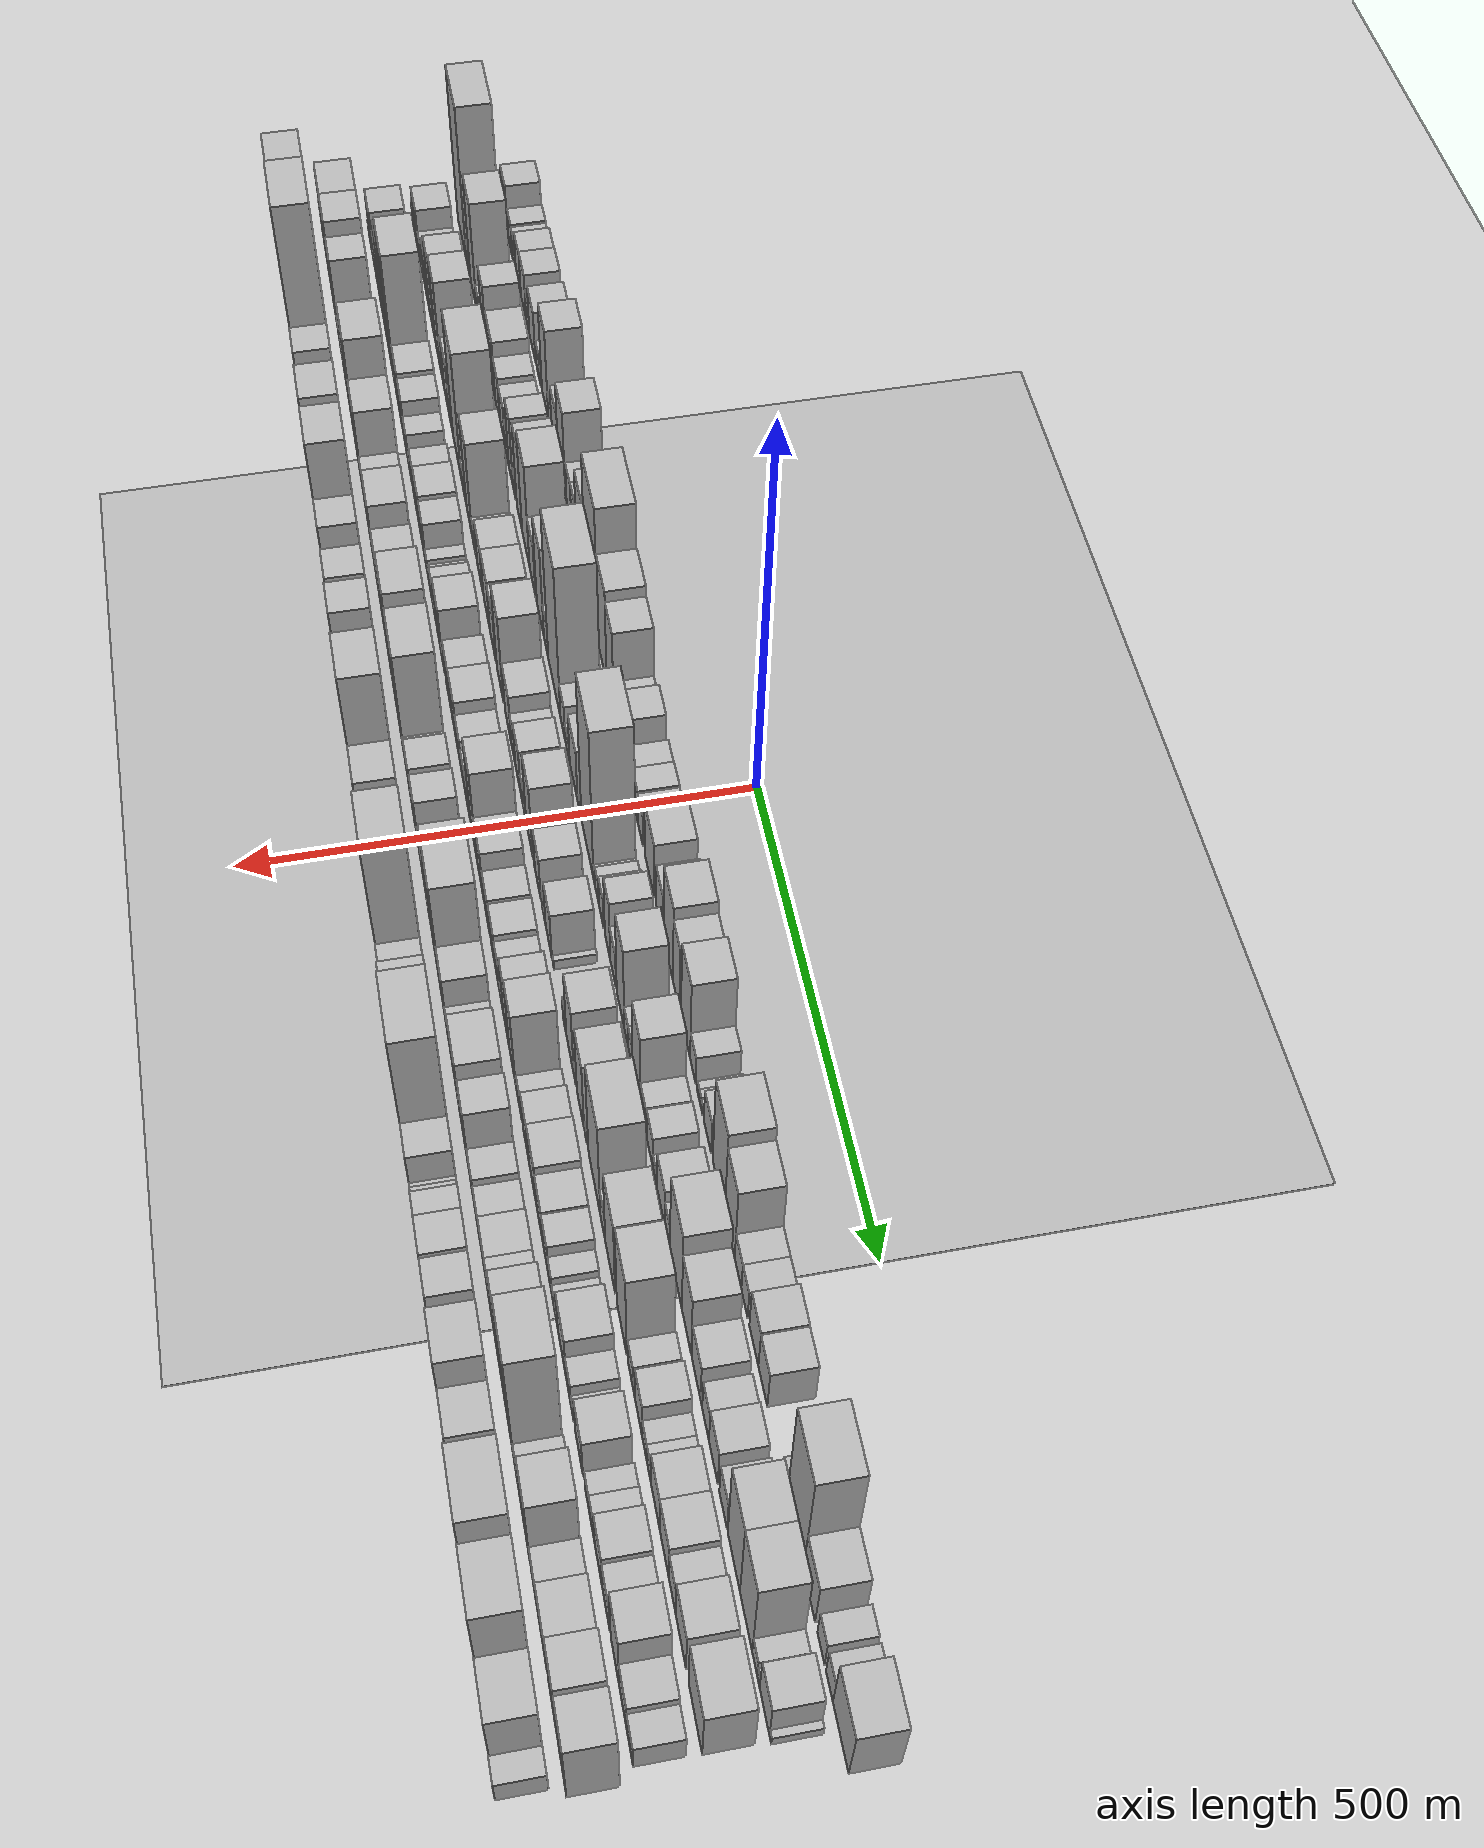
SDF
<?xml version="1.0" encoding="utf-8"?>

<sdf version="1.6">

   <world name="default">

      <gui fullscreen="0">

         <camera name="user_camera">

            <pose>-15 0 4.57585 0 0 0</pose>

            <view_controller>orbit</view_controller>

         </camera>

      </gui>

      <scene>

         <sky>

           <clouds>

             <speed>12</speed>

           </clouds>

         </sky>

         <ambient>0.4 0.4 0.4 1</ambient>

         <background>0.7 0.7 0.7 1</background>

         <shadows>1</shadows>

      </scene>

      <gravity>0 0 -9.8066</gravity>

      <magnetic_field>6e-06 2.3e-05 -4.2e-05</magnetic_field>

      <physics default="0" name="default_physics" type="ode">

         <ode>

            <solver>

               <type>quick</type>

               <iters>10</iters>

               <sor>1.0</sor>

               <use_dynamic_moi_rescaling>0</use_dynamic_moi_rescaling>

            </solver>

            <constraints>

               <cfm>0</cfm>

               <erp>0.2</erp>

               <contact_max_correcting_vel>100</contact_max_correcting_vel>

               <contact_surface_layer>0.001</contact_surface_layer>

            </constraints>

         </ode>

         <max_step_size>0.004</max_step_size>

         <real_time_factor>1</real_time_factor>

         <real_time_update_rate>250</real_time_update_rate>

      </physics>

      <light name="sun" type="directional">

         <cast_shadows>1</cast_shadows>

         <pose>0 0 10 0 0 0</pose>

         <diffuse>0.8 0.8 0.8 1</diffuse>

         <specular>0.2 0.2 0.2 1</specular>

         <attenuation>

            <range>1000</range>

            <constant>0.9</constant>

            <linear>0.01</linear>

            <quadratic>0.001</quadratic>

         </attenuation>

         <direction>-0.5 0.1 -0.9</direction>

      </light>

      <include>

         <name>ground_plane_1</name>

         <uri>model://HANNAS_ground_plane</uri>

         <pose>0 0 0  0 0 0</pose>

      </include>

      <include>

         <name>ground_plane_2</name>

         <uri>model://HANNAS_ground_plane</uri>

         <pose>100 0 0  0 0 0</pose>

      </include>

      <model name="building_1">

         <static>1</static>

         <pose frame="">100.0000 -836.1101 0 0.000000 0.000000 0.000000</pose>

         <link name="link">

            <pose frame="">0 0 37.50 0 0 0</pose>

            <collision name="collision">

               <geometry>

                  <box>

                     <size>40.0000 37.7797 75.0000</size>

                  </box>

               </geometry>

               <max_contacts>10</max_contacts>

               <surface>

                  <contact>

                     <ode/>

                  </contact>

                  <bounce/>

                  <friction>

                     <torsional>

                        <ode/>

                     </torsional>

                     <ode/>

                  </friction>

               </surface>

            </collision>

            <visual name="visual">

               <cast_shadows>0</cast_shadows>

               <geometry>

                  <box>

                     <size>40.0000 37.7797 75.0000</size>

                  </box>

               </geometry>

               <material>

                  <script>

                     <uri>model://HANNAS_wall/materials/scripts</uri>

                     <uri>model://HANNAS_wall/materials/textures</uri>

                     <name>vrc/HANNAS_wall</name>

                  </script>

               </material>

            </visual>

            <self_collide>0</self_collide>

            <enable_wind>0</enable_wind>

            <kinematic>0</kinematic>

         </link>

      </model>

      <model name="building_2">

         <static>1</static>

         <pose frame="">100.0000 -814.1010 0 0.000000 0.000000 0.000000</pose>

         <link name="link">

            <pose frame="">0 0 7.50 0 0 0</pose>

            <collision name="collision">

               <geometry>

                  <box>

                     <size>40.0000 6.2386 15.0000</size>

                  </box>

               </geometry>

               <max_contacts>10</max_contacts>

               <surface>

                  <contact>

                     <ode/>

                  </contact>

                  <bounce/>

                  <friction>

                     <torsional>

                        <ode/>

                     </torsional>

                     <ode/>

                  </friction>

               </surface>

            </collision>

            <visual name="visual">

               <cast_shadows>0</cast_shadows>

               <geometry>

                  <box>

                     <size>40.0000 6.2386 15.0000</size>

                  </box>

               </geometry>

               <material>

                  <script>

                     <uri>model://HANNAS_wall/materials/scripts</uri>

                     <uri>model://HANNAS_wall/materials/textures</uri>

                     <name>vrc/HANNAS_wall</name>

                  </script>

               </material>

            </visual>

            <self_collide>0</self_collide>

            <enable_wind>0</enable_wind>

            <kinematic>0</kinematic>

         </link>

      </model>

      <model name="building_3">

         <static>1</static>

         <pose frame="">100.0000 -797.0006 0 0.000000 0.000000 0.000000</pose>

         <link name="link">

            <pose frame="">0 0 24.00 0 0 0</pose>

            <collision name="collision">

               <geometry>

                  <box>

                     <size>40.0000 27.9622 48.0000</size>

                  </box>

               </geometry>

               <max_contacts>10</max_contacts>

               <surface>

                  <contact>

                     <ode/>

                  </contact>

                  <bounce/>

                  <friction>

                     <torsional>

                        <ode/>

                     </torsional>

                     <ode/>

                  </friction>

               </surface>

            </collision>

            <visual name="visual">

               <cast_shadows>0</cast_shadows>

               <geometry>

                  <box>

                     <size>40.0000 27.9622 48.0000</size>

                  </box>

               </geometry>

               <material>

                  <script>

                     <uri>model://HANNAS_wall/materials/scripts</uri>

                     <uri>model://HANNAS_wall/materials/textures</uri>

                     <name>vrc/HANNAS_wall</name>

                  </script>

               </material>

            </visual>

            <self_collide>0</self_collide>

            <enable_wind>0</enable_wind>

            <kinematic>0</kinematic>

         </link>

      </model>

      <model name="building_4">

         <static>1</static>

         <pose frame="">100.0000 -770.9976 0 0.000000 0.000000 0.000000</pose>

         <link name="link">

            <pose frame="">0 0 22.50 0 0 0</pose>

            <collision name="collision">

               <geometry>

                  <box>

                     <size>40.0000 24.0437 45.0000</size>

                  </box>

               </geometry>

               <max_contacts>10</max_contacts>

               <surface>

                  <contact>

                     <ode/>

                  </contact>

                  <bounce/>

                  <friction>

                     <torsional>

                        <ode/>

                     </torsional>

                     <ode/>

                  </friction>

               </surface>

            </collision>

            <visual name="visual">

               <cast_shadows>0</cast_shadows>

               <geometry>

                  <box>

                     <size>40.0000 24.0437 45.0000</size>

                  </box>

               </geometry>

               <material>

                  <script>

                     <uri>model://HANNAS_wall/materials/scripts</uri>

                     <uri>model://HANNAS_wall/materials/textures</uri>

                     <name>vrc/HANNAS_wall</name>

                  </script>

               </material>

            </visual>

            <self_collide>0</self_collide>

            <enable_wind>0</enable_wind>

            <kinematic>0</kinematic>

         </link>

      </model>

      <model name="building_5">

         <static>1</static>

         <pose frame="">100.0000 -735.8381 0 0.000000 0.000000 0.000000</pose>

         <link name="link">

            <pose frame="">0 0 31.50 0 0 0</pose>

            <collision name="collision">

               <geometry>

                  <box>

                     <size>40.0000 36.2753 63.0000</size>

                  </box>

               </geometry>

               <max_contacts>10</max_contacts>

               <surface>

                  <contact>

                     <ode/>

                  </contact>

                  <bounce/>

                  <friction>

                     <torsional>

                        <ode/>

                     </torsional>

                     <ode/>

                  </friction>

               </surface>

            </collision>

            <visual name="visual">

               <cast_shadows>0</cast_shadows>

               <geometry>

                  <box>

                     <size>40.0000 36.2753 63.0000</size>

                  </box>

               </geometry>

               <material>

                  <script>

                     <uri>model://HANNAS_wall/materials/scripts</uri>

                     <uri>model://HANNAS_wall/materials/textures</uri>

                     <name>vrc/HANNAS_wall</name>

                  </script>

               </material>

            </visual>

            <self_collide>0</self_collide>

            <enable_wind>0</enable_wind>

            <kinematic>0</kinematic>

         </link>

      </model>

      <model name="building_6">

         <static>1</static>

         <pose frame="">100.0000 -698.1796 0 0.000000 0.000000 0.000000</pose>

         <link name="link">

            <pose frame="">0 0 33.00 0 0 0</pose>

            <collision name="collision">

               <geometry>

                  <box>

                     <size>40.0000 39.0418 66.0000</size>

                  </box>

               </geometry>

               <max_contacts>10</max_contacts>

               <surface>

                  <contact>

                     <ode/>

                  </contact>

                  <bounce/>

                  <friction>

                     <torsional>

                        <ode/>

                     </torsional>

                     <ode/>

                  </friction>

               </surface>

            </collision>

            <visual name="visual">

               <cast_shadows>0</cast_shadows>

               <geometry>

                  <box>

                     <size>40.0000 39.0418 66.0000</size>

                  </box>

               </geometry>

               <material>

                  <script>

                     <uri>model://HANNAS_wall/materials/scripts</uri>

                     <uri>model://HANNAS_wall/materials/textures</uri>

                     <name>vrc/HANNAS_wall</name>

                  </script>

               </material>

            </visual>

            <self_collide>0</self_collide>

            <enable_wind>0</enable_wind>

            <kinematic>0</kinematic>

         </link>

      </model>

      <model name="building_7">

         <static>1</static>

         <pose frame="">100.0000 -666.7290 0 0.000000 0.000000 0.000000</pose>

         <link name="link">

            <pose frame="">0 0 22.50 0 0 0</pose>

            <collision name="collision">

               <geometry>

                  <box>

                     <size>40.0000 23.8593 45.0000</size>

                  </box>

               </geometry>

               <max_contacts>10</max_contacts>

               <surface>

                  <contact>

                     <ode/>

                  </contact>

                  <bounce/>

                  <friction>

                     <torsional>

                        <ode/>

                     </torsional>

                     <ode/>

                  </friction>

               </surface>

            </collision>

            <visual name="visual">

               <cast_shadows>0</cast_shadows>

               <geometry>

                  <box>

                     <size>40.0000 23.8593 45.0000</size>

                  </box>

               </geometry>

               <material>

                  <script>

                     <uri>model://HANNAS_wall/materials/scripts</uri>

                     <uri>model://HANNAS_wall/materials/textures</uri>

                     <name>vrc/HANNAS_wall</name>

                  </script>

               </material>

            </visual>

            <self_collide>0</self_collide>

            <enable_wind>0</enable_wind>

            <kinematic>0</kinematic>

         </link>

      </model>

      <model name="building_8">

         <static>1</static>

         <pose frame="">100.0000 -633.4664 0 0.000000 0.000000 0.000000</pose>

         <link name="link">

            <pose frame="">0 0 36.00 0 0 0</pose>

            <collision name="collision">

               <geometry>

                  <box>

                     <size>40.0000 42.6658 72.0000</size>

                  </box>

               </geometry>

               <max_contacts>10</max_contacts>

               <surface>

                  <contact>

                     <ode/>

                  </contact>

                  <bounce/>

                  <friction>

                     <torsional>

                        <ode/>

                     </torsional>

                     <ode/>

                  </friction>

               </surface>

            </collision>

            <visual name="visual">

               <cast_shadows>0</cast_shadows>

               <geometry>

                  <box>

                     <size>40.0000 42.6658 72.0000</size>

                  </box>

               </geometry>

               <material>

                  <script>

                     <uri>model://HANNAS_wall/materials/scripts</uri>

                     <uri>model://HANNAS_wall/materials/textures</uri>

                     <name>vrc/HANNAS_wall</name>

                  </script>

               </material>

            </visual>

            <self_collide>0</self_collide>

            <enable_wind>0</enable_wind>

            <kinematic>0</kinematic>

         </link>

      </model>

      <model name="building_9">

         <static>1</static>

         <pose frame="">100.0000 -593.3908 0 0.000000 0.000000 0.000000</pose>

         <link name="link">

            <pose frame="">0 0 19.50 0 0 0</pose>

            <collision name="collision">

               <geometry>

                  <box>

                     <size>40.0000 21.4854 39.0000</size>

                  </box>

               </geometry>

               <max_contacts>10</max_contacts>

               <surface>

                  <contact>

                     <ode/>

                  </contact>

                  <bounce/>

                  <friction>

                     <torsional>

                        <ode/>

                     </torsional>

                     <ode/>

                  </friction>

               </surface>

            </collision>

            <visual name="visual">

               <cast_shadows>0</cast_shadows>

               <geometry>

                  <box>

                     <size>40.0000 21.4854 39.0000</size>

                  </box>

               </geometry>

               <material>

                  <script>

                     <uri>model://HANNAS_wall/materials/scripts</uri>

                     <uri>model://HANNAS_wall/materials/textures</uri>

                     <name>vrc/HANNAS_wall</name>

                  </script>

               </material>

            </visual>

            <self_collide>0</self_collide>

            <enable_wind>0</enable_wind>

            <kinematic>0</kinematic>

         </link>

      </model>

      <model name="building_10">

         <static>1</static>

         <pose frame="">100.0000 -577.4798 0 0.000000 0.000000 0.000000</pose>

         <link name="link">

            <pose frame="">0 0 10.50 0 0 0</pose>

            <collision name="collision">

               <geometry>

                  <box>

                     <size>40.0000 10.3366 21.0000</size>

                  </box>

               </geometry>

               <max_contacts>10</max_contacts>

               <surface>

                  <contact>

                     <ode/>

                  </contact>

                  <bounce/>

                  <friction>

                     <torsional>

                        <ode/>

                     </torsional>

                     <ode/>

                  </friction>

               </surface>

            </collision>

            <visual name="visual">

               <cast_shadows>0</cast_shadows>

               <geometry>

                  <box>

                     <size>40.0000 10.3366 21.0000</size>

                  </box>

               </geometry>

               <material>

                  <script>

                     <uri>model://HANNAS_wall/materials/scripts</uri>

                     <uri>model://HANNAS_wall/materials/textures</uri>

                     <name>vrc/HANNAS_wall</name>

                  </script>

               </material>

            </visual>

            <self_collide>0</self_collide>

            <enable_wind>0</enable_wind>

            <kinematic>0</kinematic>

         </link>

      </model>

      <model name="building_11">

         <static>1</static>

         <pose frame="">100.0000 -543.3504 0 0.000000 0.000000 0.000000</pose>

         <link name="link">

            <pose frame="">0 0 64.50 0 0 0</pose>

            <collision name="collision">

               <geometry>

                  <box>

                     <size>40.0000 43.9221 129.0000</size>

                  </box>

               </geometry>

               <max_contacts>10</max_contacts>

               <surface>

                  <contact>

                     <ode/>

                  </contact>

                  <bounce/>

                  <friction>

                     <torsional>

                        <ode/>

                     </torsional>

                     <ode/>

                  </friction>

               </surface>

            </collision>

            <visual name="visual">

               <cast_shadows>0</cast_shadows>

               <geometry>

                  <box>

                     <size>40.0000 43.9221 129.0000</size>

                  </box>

               </geometry>

               <material>

                  <script>

                     <uri>model://HANNAS_wall/materials/scripts</uri>

                     <uri>model://HANNAS_wall/materials/textures</uri>

                     <name>vrc/HANNAS_wall</name>

                  </script>

               </material>

            </visual>

            <self_collide>0</self_collide>

            <enable_wind>0</enable_wind>

            <kinematic>0</kinematic>

         </link>

      </model>

      <model name="building_12">

         <static>1</static>

         <pose frame="">100.0000 -509.4019 0 0.000000 0.000000 0.000000</pose>

         <link name="link">

            <pose frame="">0 0 21.00 0 0 0</pose>

            <collision name="collision">

               <geometry>

                  <box>

                     <size>40.0000 23.9750 42.0000</size>

                  </box>

               </geometry>

               <max_contacts>10</max_contacts>

               <surface>

                  <contact>

                     <ode/>

                  </contact>

                  <bounce/>

                  <friction>

                     <torsional>

                        <ode/>

                     </torsional>

                     <ode/>

                  </friction>

               </surface>

            </collision>

            <visual name="visual">

               <cast_shadows>0</cast_shadows>

               <geometry>

                  <box>

                     <size>40.0000 23.9750 42.0000</size>

                  </box>

               </geometry>

               <material>

                  <script>

                     <uri>model://HANNAS_wall/materials/scripts</uri>

                     <uri>model://HANNAS_wall/materials/textures</uri>

                     <name>vrc/HANNAS_wall</name>

                  </script>

               </material>

            </visual>

            <self_collide>0</self_collide>

            <enable_wind>0</enable_wind>

            <kinematic>0</kinematic>

         </link>

      </model>

      <model name="building_13">

         <static>1</static>

         <pose frame="">100.0000 -474.9482 0 0.000000 0.000000 0.000000</pose>

         <link name="link">

            <pose frame="">0 0 37.50 0 0 0</pose>

            <collision name="collision">

               <geometry>

                  <box>

                     <size>40.0000 44.9325 75.0000</size>

                  </box>

               </geometry>

               <max_contacts>10</max_contacts>

               <surface>

                  <contact>

                     <ode/>

                  </contact>

                  <bounce/>

                  <friction>

                     <torsional>

                        <ode/>

                     </torsional>

                     <ode/>

                  </friction>

               </surface>

            </collision>

            <visual name="visual">

               <cast_shadows>0</cast_shadows>

               <geometry>

                  <box>

                     <size>40.0000 44.9325 75.0000</size>

                  </box>

               </geometry>

               <material>

                  <script>

                     <uri>model://HANNAS_wall/materials/scripts</uri>

                     <uri>model://HANNAS_wall/materials/textures</uri>

                     <name>vrc/HANNAS_wall</name>

                  </script>

               </material>

            </visual>

            <self_collide>0</self_collide>

            <enable_wind>0</enable_wind>

            <kinematic>0</kinematic>

         </link>

      </model>

      <model name="building_14">

         <static>1</static>

         <pose frame="">100.0000 -430.0063 0 0.000000 0.000000 0.000000</pose>

         <link name="link">

            <pose frame="">0 0 61.50 0 0 0</pose>

            <collision name="collision">

               <geometry>

                  <box>

                     <size>40.0000 44.9513 123.0000</size>

                  </box>

               </geometry>

               <max_contacts>10</max_contacts>

               <surface>

                  <contact>

                     <ode/>

                  </contact>

                  <bounce/>

                  <friction>

                     <torsional>

                        <ode/>

                     </torsional>

                     <ode/>

                  </friction>

               </surface>

            </collision>

            <visual name="visual">

               <cast_shadows>0</cast_shadows>

               <geometry>

                  <box>

                     <size>40.0000 44.9513 123.0000</size>

                  </box>

               </geometry>

               <material>

                  <script>

                     <uri>model://HANNAS_wall/materials/scripts</uri>

                     <uri>model://HANNAS_wall/materials/textures</uri>

                     <name>vrc/HANNAS_wall</name>

                  </script>

               </material>

            </visual>

            <self_collide>0</self_collide>

            <enable_wind>0</enable_wind>

            <kinematic>0</kinematic>

         </link>

      </model>

      <model name="building_15">

         <static>1</static>

         <pose frame="">100.0000 -403.5633 0 0.000000 0.000000 0.000000</pose>

         <link name="link">

            <pose frame="">0 0 9.00 0 0 0</pose>

            <collision name="collision">

               <geometry>

                  <box>

                     <size>40.0000 7.9347 18.0000</size>

                  </box>

               </geometry>

               <max_contacts>10</max_contacts>

               <surface>

                  <contact>

                     <ode/>

                  </contact>

                  <bounce/>

                  <friction>

                     <torsional>

                        <ode/>

                     </torsional>

                     <ode/>

                  </friction>

               </surface>

            </collision>

            <visual name="visual">

               <cast_shadows>0</cast_shadows>

               <geometry>

                  <box>

                     <size>40.0000 7.9347 18.0000</size>

                  </box>

               </geometry>

               <material>

                  <script>

                     <uri>model://HANNAS_wall/materials/scripts</uri>

                     <uri>model://HANNAS_wall/materials/textures</uri>

                     <name>vrc/HANNAS_wall</name>

                  </script>

               </material>

            </visual>

            <self_collide>0</self_collide>

            <enable_wind>0</enable_wind>

            <kinematic>0</kinematic>

         </link>

      </model>

      <model name="building_16">

         <static>1</static>

         <pose frame="">100.0000 -384.0746 0 0.000000 0.000000 0.000000</pose>

         <link name="link">

            <pose frame="">0 0 30.00 0 0 0</pose>

            <collision name="collision">

               <geometry>

                  <box>

                     <size>40.0000 31.0427 60.0000</size>

                  </box>

               </geometry>

               <max_contacts>10</max_contacts>

               <surface>

                  <contact>

                     <ode/>

                  </contact>

                  <bounce/>

                  <friction>

                     <torsional>

                        <ode/>

                     </torsional>

                     <ode/>

                  </friction>

               </surface>

            </collision>

            <visual name="visual">

               <cast_shadows>0</cast_shadows>

               <geometry>

                  <box>

                     <size>40.0000 31.0427 60.0000</size>

                  </box>

               </geometry>

               <material>

                  <script>

                     <uri>model://HANNAS_wall/materials/scripts</uri>

                     <uri>model://HANNAS_wall/materials/textures</uri>

                     <name>vrc/HANNAS_wall</name>

                  </script>

               </material>

            </visual>

            <self_collide>0</self_collide>

            <enable_wind>0</enable_wind>

            <kinematic>0</kinematic>

         </link>

      </model>

      <model name="building_17">

         <static>1</static>

         <pose frame="">100.0000 -351.5795 0 0.000000 0.000000 0.000000</pose>

         <link name="link">

            <pose frame="">0 0 31.50 0 0 0</pose>

            <collision name="collision">

               <geometry>

                  <box>

                     <size>40.0000 33.9475 63.0000</size>

                  </box>

               </geometry>

               <max_contacts>10</max_contacts>

               <surface>

                  <contact>

                     <ode/>

                  </contact>

                  <bounce/>

                  <friction>

                     <torsional>

                        <ode/>

                     </torsional>

                     <ode/>

                  </friction>

               </surface>

            </collision>

            <visual name="visual">

               <cast_shadows>0</cast_shadows>

               <geometry>

                  <box>

                     <size>40.0000 33.9475 63.0000</size>

                  </box>

               </geometry>

               <material>

                  <script>

                     <uri>model://HANNAS_wall/materials/scripts</uri>

                     <uri>model://HANNAS_wall/materials/textures</uri>

                     <name>vrc/HANNAS_wall</name>

                  </script>

               </material>

            </visual>

            <self_collide>0</self_collide>

            <enable_wind>0</enable_wind>

            <kinematic>0</kinematic>

         </link>

      </model>

      <model name="building_18">

         <static>1</static>

         <pose frame="">100.0000 -312.0746 0 0.000000 0.000000 0.000000</pose>

         <link name="link">

            <pose frame="">0 0 58.50 0 0 0</pose>

            <collision name="collision">

               <geometry>

                  <box>

                     <size>40.0000 45.0622 117.0000</size>

                  </box>

               </geometry>

               <max_contacts>10</max_contacts>

               <surface>

                  <contact>

                     <ode/>

                  </contact>

                  <bounce/>

                  <friction>

                     <torsional>

                        <ode/>

                     </torsional>

                     <ode/>

                  </friction>

               </surface>

            </collision>

            <visual name="visual">

               <cast_shadows>0</cast_shadows>

               <geometry>

                  <box>

                     <size>40.0000 45.0622 117.0000</size>

                  </box>

               </geometry>

               <material>

                  <script>

                     <uri>model://HANNAS_wall/materials/scripts</uri>

                     <uri>model://HANNAS_wall/materials/textures</uri>

                     <name>vrc/HANNAS_wall</name>

                  </script>

               </material>

            </visual>

            <self_collide>0</self_collide>

            <enable_wind>0</enable_wind>

            <kinematic>0</kinematic>

         </link>

      </model>

      <model name="building_19">

         <static>1</static>

         <pose frame="">100.0000 -242.4100 0 0.000000 0.000000 0.000000</pose>

         <link name="link">

            <pose frame="">0 0 99.00 0 0 0</pose>

            <collision name="collision">

               <geometry>

                  <box>

                     <size>40.0000 74.2670 198.0000</size>

                  </box>

               </geometry>

               <max_contacts>10</max_contacts>

               <surface>

                  <contact>

                     <ode/>

                  </contact>

                  <bounce/>

                  <friction>

                     <torsional>

                        <ode/>

                     </torsional>

                     <ode/>

                  </friction>

               </surface>

            </collision>

            <visual name="visual">

               <cast_shadows>0</cast_shadows>

               <geometry>

                  <box>

                     <size>40.0000 74.2670 198.0000</size>

                  </box>

               </geometry>

               <material>

                  <script>

                     <uri>model://HANNAS_wall/materials/scripts</uri>

                     <uri>model://HANNAS_wall/materials/textures</uri>

                     <name>vrc/HANNAS_wall</name>

                  </script>

               </material>

            </visual>

            <self_collide>0</self_collide>

            <enable_wind>0</enable_wind>

            <kinematic>0</kinematic>

         </link>

      </model>

      <model name="building_20">

         <static>1</static>

         <pose frame="">100.0000 -178.1504 0 0.000000 0.000000 0.000000</pose>

         <link name="link">

            <pose frame="">0 0 69.00 0 0 0</pose>

            <collision name="collision">

               <geometry>

                  <box>

                     <size>40.0000 48.2522 138.0000</size>

                  </box>

               </geometry>

               <max_contacts>10</max_contacts>

               <surface>

                  <contact>

                     <ode/>

                  </contact>

                  <bounce/>

                  <friction>

                     <torsional>

                        <ode/>

                     </torsional>

                     <ode/>

                  </friction>

               </surface>

            </collision>

            <visual name="visual">

               <cast_shadows>0</cast_shadows>

               <geometry>

                  <box>

                     <size>40.0000 48.2522 138.0000</size>

                  </box>

               </geometry>

               <material>

                  <script>

                     <uri>model://HANNAS_wall/materials/scripts</uri>

                     <uri>model://HANNAS_wall/materials/textures</uri>

                     <name>vrc/HANNAS_wall</name>

                  </script>

               </material>

            </visual>

            <self_collide>0</self_collide>

            <enable_wind>0</enable_wind>

            <kinematic>0</kinematic>

         </link>

      </model>

      <model name="building_21">

         <static>1</static>

         <pose frame="">100.0000 -134.0736 0 0.000000 0.000000 0.000000</pose>

         <link name="link">

            <pose frame="">0 0 61.50 0 0 0</pose>

            <collision name="collision">

               <geometry>

                  <box>

                     <size>40.0000 39.9015 123.0000</size>

                  </box>

               </geometry>

               <max_contacts>10</max_contacts>

               <surface>

                  <contact>

                     <ode/>

                  </contact>

                  <bounce/>

                  <friction>

                     <torsional>

                        <ode/>

                     </torsional>

                     <ode/>

                  </friction>

               </surface>

            </collision>

            <visual name="visual">

               <cast_shadows>0</cast_shadows>

               <geometry>

                  <box>

                     <size>40.0000 39.9015 123.0000</size>

                  </box>

               </geometry>

               <material>

                  <script>

                     <uri>model://HANNAS_wall/materials/scripts</uri>

                     <uri>model://HANNAS_wall/materials/textures</uri>

                     <name>vrc/HANNAS_wall</name>

                  </script>

               </material>

            </visual>

            <self_collide>0</self_collide>

            <enable_wind>0</enable_wind>

            <kinematic>0</kinematic>

         </link>

      </model>

      <model name="building_22">

         <static>1</static>

         <pose frame="">100.0000 -100.3217 0 0.000000 0.000000 0.000000</pose>

         <link name="link">

            <pose frame="">0 0 25.50 0 0 0</pose>

            <collision name="collision">

               <geometry>

                  <box>

                     <size>40.0000 27.6023 51.0000</size>

                  </box>

               </geometry>

               <max_contacts>10</max_contacts>

               <surface>

                  <contact>

                     <ode/>

                  </contact>

                  <bounce/>

                  <friction>

                     <torsional>

                        <ode/>

                     </torsional>

                     <ode/>

                  </friction>

               </surface>

            </collision>

            <visual name="visual">

               <cast_shadows>0</cast_shadows>

               <geometry>

                  <box>

                     <size>40.0000 27.6023 51.0000</size>

                  </box>

               </geometry>

               <material>

                  <script>

                     <uri>model://HANNAS_wall/materials/scripts</uri>

                     <uri>model://HANNAS_wall/materials/textures</uri>

                     <name>vrc/HANNAS_wall</name>

                  </script>

               </material>

            </visual>

            <self_collide>0</self_collide>

            <enable_wind>0</enable_wind>

            <kinematic>0</kinematic>

         </link>

      </model>

      <model name="building_23">

         <static>1</static>

         <pose frame="">100.0000 -67.7895 0 0.000000 0.000000 0.000000</pose>

         <link name="link">

            <pose frame="">0 0 36.00 0 0 0</pose>

            <collision name="collision">

               <geometry>

                  <box>

                     <size>40.0000 37.4621 72.0000</size>

                  </box>

               </geometry>

               <max_contacts>10</max_contacts>

               <surface>

                  <contact>

                     <ode/>

                  </contact>

                  <bounce/>

                  <friction>

                     <torsional>

                        <ode/>

                     </torsional>

                     <ode/>

                  </friction>

               </surface>

            </collision>

            <visual name="visual">

               <cast_shadows>0</cast_shadows>

               <geometry>

                  <box>

                     <size>40.0000 37.4621 72.0000</size>

                  </box>

               </geometry>

               <material>

                  <script>

                     <uri>model://HANNAS_wall/materials/scripts</uri>

                     <uri>model://HANNAS_wall/materials/textures</uri>

                     <name>vrc/HANNAS_wall</name>

                  </script>

               </material>

            </visual>

            <self_collide>0</self_collide>

            <enable_wind>0</enable_wind>

            <kinematic>0</kinematic>

         </link>

      </model>

      <model name="building_24">

         <static>1</static>

         <pose frame="">100.0000 -43.5704 0 0.000000 0.000000 0.000000</pose>

         <link name="link">

            <pose frame="">0 0 12.00 0 0 0</pose>

            <collision name="collision">

               <geometry>

                  <box>

                     <size>40.0000 10.9760 24.0000</size>

                  </box>

               </geometry>

               <max_contacts>10</max_contacts>

               <surface>

                  <contact>

                     <ode/>

                  </contact>

                  <bounce/>

                  <friction>

                     <torsional>

                        <ode/>

                     </torsional>

                     <ode/>

                  </friction>

               </surface>

            </collision>

            <visual name="visual">

               <cast_shadows>0</cast_shadows>

               <geometry>

                  <box>

                     <size>40.0000 10.9760 24.0000</size>

                  </box>

               </geometry>

               <material>

                  <script>

                     <uri>model://HANNAS_wall/materials/scripts</uri>

                     <uri>model://HANNAS_wall/materials/textures</uri>

                     <name>vrc/HANNAS_wall</name>

                  </script>

               </material>

            </visual>

            <self_collide>0</self_collide>

            <enable_wind>0</enable_wind>

            <kinematic>0</kinematic>

         </link>

      </model>

      <model name="building_25">

         <static>1</static>

         <pose frame="">100.0000 -23.7559 0 0.000000 0.000000 0.000000</pose>

         <link name="link">

            <pose frame="">0 0 24.00 0 0 0</pose>

            <collision name="collision">

               <geometry>

                  <box>

                     <size>40.0000 28.6529 48.0000</size>

                  </box>

               </geometry>

               <max_contacts>10</max_contacts>

               <surface>

                  <contact>

                     <ode/>

                  </contact>

                  <bounce/>

                  <friction>

                     <torsional>

                        <ode/>

                     </torsional>

                     <ode/>

                  </friction>

               </surface>

            </collision>

            <visual name="visual">

               <cast_shadows>0</cast_shadows>

               <geometry>

                  <box>

                     <size>40.0000 28.6529 48.0000</size>

                  </box>

               </geometry>

               <material>

                  <script>

                     <uri>model://HANNAS_wall/materials/scripts</uri>

                     <uri>model://HANNAS_wall/materials/textures</uri>

                     <name>vrc/HANNAS_wall</name>

                  </script>

               </material>

            </visual>

            <self_collide>0</self_collide>

            <enable_wind>0</enable_wind>

            <kinematic>0</kinematic>

         </link>

      </model>

      <model name="building_26">

         <static>1</static>

         <pose frame="">100.0000 4.6987 0 0.000000 0.000000 0.000000</pose>

         <link name="link">

            <pose frame="">0 0 25.50 0 0 0</pose>

            <collision name="collision">

               <geometry>

                  <box>

                     <size>40.0000 28.2563 51.0000</size>

                  </box>

               </geometry>

               <max_contacts>10</max_contacts>

               <surface>

                  <contact>

                     <ode/>

                  </contact>

                  <bounce/>

                  <friction>

                     <torsional>

                        <ode/>

                     </torsional>

                     <ode/>

                  </friction>

               </surface>

            </collision>

            <visual name="visual">

               <cast_shadows>0</cast_shadows>

               <geometry>

                  <box>

                     <size>40.0000 28.2563 51.0000</size>

                  </box>

               </geometry>

               <material>

                  <script>

                     <uri>model://HANNAS_wall/materials/scripts</uri>

                     <uri>model://HANNAS_wall/materials/textures</uri>

                     <name>vrc/HANNAS_wall</name>

                  </script>

               </material>

            </visual>

            <self_collide>0</self_collide>

            <enable_wind>0</enable_wind>

            <kinematic>0</kinematic>

         </link>

      </model>

      <model name="building_27">

         <static>1</static>

         <pose frame="">100.0000 32.3830 0 0.000000 0.000000 0.000000</pose>

         <link name="link">

            <pose frame="">0 0 24.00 0 0 0</pose>

            <collision name="collision">

               <geometry>

                  <box>

                     <size>40.0000 27.1123 48.0000</size>

                  </box>

               </geometry>

               <max_contacts>10</max_contacts>

               <surface>

                  <contact>

                     <ode/>

                  </contact>

                  <bounce/>

                  <friction>

                     <torsional>

                        <ode/>

                     </torsional>

                     <ode/>

                  </friction>

               </surface>

            </collision>

            <visual name="visual">

               <cast_shadows>0</cast_shadows>

               <geometry>

                  <box>

                     <size>40.0000 27.1123 48.0000</size>

                  </box>

               </geometry>

               <material>

                  <script>

                     <uri>model://HANNAS_wall/materials/scripts</uri>

                     <uri>model://HANNAS_wall/materials/textures</uri>

                     <name>vrc/HANNAS_wall</name>

                  </script>

               </material>

            </visual>

            <self_collide>0</self_collide>

            <enable_wind>0</enable_wind>

            <kinematic>0</kinematic>

         </link>

      </model>

      <model name="building_28">

         <static>1</static>

         <pose frame="">100.0000 79.7032 0 0.000000 0.000000 0.000000</pose>

         <link name="link">

            <pose frame="">0 0 42.00 0 0 0</pose>

            <collision name="collision">

               <geometry>

                  <box>

                     <size>40.0000 49.5280 84.0000</size>

                  </box>

               </geometry>

               <max_contacts>10</max_contacts>

               <surface>

                  <contact>

                     <ode/>

                  </contact>

                  <bounce/>

                  <friction>

                     <torsional>

                        <ode/>

                     </torsional>

                     <ode/>

                  </friction>

               </surface>

            </collision>

            <visual name="visual">

               <cast_shadows>0</cast_shadows>

               <geometry>

                  <box>

                     <size>40.0000 49.5280 84.0000</size>

                  </box>

               </geometry>

               <material>

                  <script>

                     <uri>model://HANNAS_wall/materials/scripts</uri>

                     <uri>model://HANNAS_wall/materials/textures</uri>

                     <name>vrc/HANNAS_wall</name>

                  </script>

               </material>

            </visual>

            <self_collide>0</self_collide>

            <enable_wind>0</enable_wind>

            <kinematic>0</kinematic>

         </link>

      </model>

      <model name="building_29">

         <static>1</static>

         <pose frame="">100.0000 131.0560 0 0.000000 0.000000 0.000000</pose>

         <link name="link">

            <pose frame="">0 0 33.00 0 0 0</pose>

            <collision name="collision">

               <geometry>

                  <box>

                     <size>40.0000 35.1776 66.0000</size>

                  </box>

               </geometry>

               <max_contacts>10</max_contacts>

               <surface>

                  <contact>

                     <ode/>

                  </contact>

                  <bounce/>

                  <friction>

                     <torsional>

                        <ode/>

                     </torsional>

                     <ode/>

                  </friction>

               </surface>

            </collision>

            <visual name="visual">

               <cast_shadows>0</cast_shadows>

               <geometry>

                  <box>

                     <size>40.0000 35.1776 66.0000</size>

                  </box>

               </geometry>

               <material>

                  <script>

                     <uri>model://HANNAS_wall/materials/scripts</uri>

                     <uri>model://HANNAS_wall/materials/textures</uri>

                     <name>vrc/HANNAS_wall</name>

                  </script>

               </material>

            </visual>

            <self_collide>0</self_collide>

            <enable_wind>0</enable_wind>

            <kinematic>0</kinematic>

         </link>

      </model>

      <model name="building_30">

         <static>1</static>

         <pose frame="">100.0000 174.4032 0 0.000000 0.000000 0.000000</pose>

         <link name="link">

            <pose frame="">0 0 60.00 0 0 0</pose>

            <collision name="collision">

               <geometry>

                  <box>

                     <size>40.0000 45.5167 120.0000</size>

                  </box>

               </geometry>

               <max_contacts>10</max_contacts>

               <surface>

                  <contact>

                     <ode/>

                  </contact>

                  <bounce/>

                  <friction>

                     <torsional>

                        <ode/>

                     </torsional>

                     <ode/>

                  </friction>

               </surface>

            </collision>

            <visual name="visual">

               <cast_shadows>0</cast_shadows>

               <geometry>

                  <box>

                     <size>40.0000 45.5167 120.0000</size>

                  </box>

               </geometry>

               <material>

                  <script>

                     <uri>model://HANNAS_wall/materials/scripts</uri>

                     <uri>model://HANNAS_wall/materials/textures</uri>

                     <name>vrc/HANNAS_wall</name>

                  </script>

               </material>

            </visual>

            <self_collide>0</self_collide>

            <enable_wind>0</enable_wind>

            <kinematic>0</kinematic>

         </link>

      </model>

      <model name="building_31">

         <static>1</static>

         <pose frame="">100.0000 212.8217 0 0.000000 0.000000 0.000000</pose>

         <link name="link">

            <pose frame="">0 0 51.00 0 0 0</pose>

            <collision name="collision">

               <geometry>

                  <box>

                     <size>40.0000 31.3202 102.0000</size>

                  </box>

               </geometry>

               <max_contacts>10</max_contacts>

               <surface>

                  <contact>

                     <ode/>

                  </contact>

                  <bounce/>

                  <friction>

                     <torsional>

                        <ode/>

                     </torsional>

                     <ode/>

                  </friction>

               </surface>

            </collision>

            <visual name="visual">

               <cast_shadows>0</cast_shadows>

               <geometry>

                  <box>

                     <size>40.0000 31.3202 102.0000</size>

                  </box>

               </geometry>

               <material>

                  <script>

                     <uri>model://HANNAS_wall/materials/scripts</uri>

                     <uri>model://HANNAS_wall/materials/textures</uri>

                     <name>vrc/HANNAS_wall</name>

                  </script>

               </material>

            </visual>

            <self_collide>0</self_collide>

            <enable_wind>0</enable_wind>

            <kinematic>0</kinematic>

         </link>

      </model>

      <model name="building_32">

         <static>1</static>

         <pose frame="">100.0000 257.0616 0 0.000000 0.000000 0.000000</pose>

         <link name="link">

            <pose frame="">0 0 61.50 0 0 0</pose>

            <collision name="collision">

               <geometry>

                  <box>

                     <size>40.0000 43.1597 123.0000</size>

                  </box>

               </geometry>

               <max_contacts>10</max_contacts>

               <surface>

                  <contact>

                     <ode/>

                  </contact>

                  <bounce/>

                  <friction>

                     <torsional>

                        <ode/>

                     </torsional>

                     <ode/>

                  </friction>

               </surface>

            </collision>

            <visual name="visual">

               <cast_shadows>0</cast_shadows>

               <geometry>

                  <box>

                     <size>40.0000 43.1597 123.0000</size>

                  </box>

               </geometry>

               <material>

                  <script>

                     <uri>model://HANNAS_wall/materials/scripts</uri>

                     <uri>model://HANNAS_wall/materials/textures</uri>

                     <name>vrc/HANNAS_wall</name>

                  </script>

               </material>

            </visual>

            <self_collide>0</self_collide>

            <enable_wind>0</enable_wind>

            <kinematic>0</kinematic>

         </link>

      </model>

      <model name="building_33">

         <static>1</static>

         <pose frame="">100.0000 291.6445 0 0.000000 0.000000 0.000000</pose>

         <link name="link">

            <pose frame="">0 0 22.50 0 0 0</pose>

            <collision name="collision">

               <geometry>

                  <box>

                     <size>40.0000 26.0062 45.0000</size>

                  </box>

               </geometry>

               <max_contacts>10</max_contacts>

               <surface>

                  <contact>

                     <ode/>

                  </contact>

                  <bounce/>

                  <friction>

                     <torsional>

                        <ode/>

                     </torsional>

                     <ode/>

                  </friction>

               </surface>

            </collision>

            <visual name="visual">

               <cast_shadows>0</cast_shadows>

               <geometry>

                  <box>

                     <size>40.0000 26.0062 45.0000</size>

                  </box>

               </geometry>

               <material>

                  <script>

                     <uri>model://HANNAS_wall/materials/scripts</uri>

                     <uri>model://HANNAS_wall/materials/textures</uri>

                     <name>vrc/HANNAS_wall</name>

                  </script>

               </material>

            </visual>

            <self_collide>0</self_collide>

            <enable_wind>0</enable_wind>

            <kinematic>0</kinematic>

         </link>

      </model>

      <model name="building_34">

         <static>1</static>

         <pose frame="">100.0000 315.8216 0 0.000000 0.000000 0.000000</pose>

         <link name="link">

            <pose frame="">0 0 9.00 0 0 0</pose>

            <collision name="collision">

               <geometry>

                  <box>

                     <size>40.0000 8.3480 18.0000</size>

                  </box>

               </geometry>

               <max_contacts>10</max_contacts>

               <surface>

                  <contact>

                     <ode/>

                  </contact>

                  <bounce/>

                  <friction>

                     <torsional>

                        <ode/>

                     </torsional>

                     <ode/>

                  </friction>

               </surface>

            </collision>

            <visual name="visual">

               <cast_shadows>0</cast_shadows>

               <geometry>

                  <box>

                     <size>40.0000 8.3480 18.0000</size>

                  </box>

               </geometry>

               <material>

                  <script>

                     <uri>model://HANNAS_wall/materials/scripts</uri>

                     <uri>model://HANNAS_wall/materials/textures</uri>

                     <name>vrc/HANNAS_wall</name>

                  </script>

               </material>

            </visual>

            <self_collide>0</self_collide>

            <enable_wind>0</enable_wind>

            <kinematic>0</kinematic>

         </link>

      </model>

      <model name="building_35">

         <static>1</static>

         <pose frame="">100.0000 324.3021 0 0.000000 0.000000 0.000000</pose>

         <link name="link">

            <pose frame="">0 0 9.00 0 0 0</pose>

            <collision name="collision">

               <geometry>

                  <box>

                     <size>40.0000 8.6129 18.0000</size>

                  </box>

               </geometry>

               <max_contacts>10</max_contacts>

               <surface>

                  <contact>

                     <ode/>

                  </contact>

                  <bounce/>

                  <friction>

                     <torsional>

                        <ode/>

                     </torsional>

                     <ode/>

                  </friction>

               </surface>

            </collision>

            <visual name="visual">

               <cast_shadows>0</cast_shadows>

               <geometry>

                  <box>

                     <size>40.0000 8.6129 18.0000</size>

                  </box>

               </geometry>

               <material>

                  <script>

                     <uri>model://HANNAS_wall/materials/scripts</uri>

                     <uri>model://HANNAS_wall/materials/textures</uri>

                     <name>vrc/HANNAS_wall</name>

                  </script>

               </material>

            </visual>

            <self_collide>0</self_collide>

            <enable_wind>0</enable_wind>

            <kinematic>0</kinematic>

         </link>

      </model>

      <model name="building_36">

         <static>1</static>

         <pose frame="">100.0000 332.2407 0 0.000000 0.000000 0.000000</pose>

         <link name="link">

            <pose frame="">0 0 7.50 0 0 0</pose>

            <collision name="collision">

               <geometry>

                  <box>

                     <size>40.0000 7.2643 15.0000</size>

                  </box>

               </geometry>

               <max_contacts>10</max_contacts>

               <surface>

                  <contact>

                     <ode/>

                  </contact>

                  <bounce/>

                  <friction>

                     <torsional>

                        <ode/>

                     </torsional>

                     <ode/>

                  </friction>

               </surface>

            </collision>

            <visual name="visual">

               <cast_shadows>0</cast_shadows>

               <geometry>

                  <box>

                     <size>40.0000 7.2643 15.0000</size>

                  </box>

               </geometry>

               <material>

                  <script>

                     <uri>model://HANNAS_wall/materials/scripts</uri>

                     <uri>model://HANNAS_wall/materials/textures</uri>

                     <name>vrc/HANNAS_wall</name>

                  </script>

               </material>

            </visual>

            <self_collide>0</self_collide>

            <enable_wind>0</enable_wind>

            <kinematic>0</kinematic>

         </link>

      </model>

      <model name="building_37">

         <static>1</static>

         <pose frame="">100.0000 357.8737 0 0.000000 0.000000 0.000000</pose>

         <link name="link">

            <pose frame="">0 0 27.00 0 0 0</pose>

            <collision name="collision">

               <geometry>

                  <box>

                     <size>40.0000 32.0017 54.0000</size>

                  </box>

               </geometry>

               <max_contacts>10</max_contacts>

               <surface>

                  <contact>

                     <ode/>

                  </contact>

                  <bounce/>

                  <friction>

                     <torsional>

                        <ode/>

                     </torsional>

                     <ode/>

                  </friction>

               </surface>

            </collision>

            <visual name="visual">

               <cast_shadows>0</cast_shadows>

               <geometry>

                  <box>

                     <size>40.0000 32.0017 54.0000</size>

                  </box>

               </geometry>

               <material>

                  <script>

                     <uri>model://HANNAS_wall/materials/scripts</uri>

                     <uri>model://HANNAS_wall/materials/textures</uri>

                     <name>vrc/HANNAS_wall</name>

                  </script>

               </material>

            </visual>

            <self_collide>0</self_collide>

            <enable_wind>0</enable_wind>

            <kinematic>0</kinematic>

         </link>

      </model>

      <model name="building_38">

         <static>1</static>

         <pose frame="">100.0000 406.7698 0 0.000000 0.000000 0.000000</pose>

         <link name="link">

            <pose frame="">0 0 70.50 0 0 0</pose>

            <collision name="collision">

               <geometry>

                  <box>

                     <size>40.0000 51.7905 141.0000</size>

                  </box>

               </geometry>

               <max_contacts>10</max_contacts>

               <surface>

                  <contact>

                     <ode/>

                  </contact>

                  <bounce/>

                  <friction>

                     <torsional>

                        <ode/>

                     </torsional>

                     <ode/>

                  </friction>

               </surface>

            </collision>

            <visual name="visual">

               <cast_shadows>0</cast_shadows>

               <geometry>

                  <box>

                     <size>40.0000 51.7905 141.0000</size>

                  </box>

               </geometry>

               <material>

                  <script>

                     <uri>model://HANNAS_wall/materials/scripts</uri>

                     <uri>model://HANNAS_wall/materials/textures</uri>

                     <name>vrc/HANNAS_wall</name>

                  </script>

               </material>

            </visual>

            <self_collide>0</self_collide>

            <enable_wind>0</enable_wind>

            <kinematic>0</kinematic>

         </link>

      </model>

      <model name="building_39">

         <static>1</static>

         <pose frame="">100.0000 453.6846 0 0.000000 0.000000 0.000000</pose>

         <link name="link">

            <pose frame="">0 0 60.00 0 0 0</pose>

            <collision name="collision">

               <geometry>

                  <box>

                     <size>40.0000 42.0391 120.0000</size>

                  </box>

               </geometry>

               <max_contacts>10</max_contacts>

               <surface>

                  <contact>

                     <ode/>

                  </contact>

                  <bounce/>

                  <friction>

                     <torsional>

                        <ode/>

                     </torsional>

                     <ode/>

                  </friction>

               </surface>

            </collision>

            <visual name="visual">

               <cast_shadows>0</cast_shadows>

               <geometry>

                  <box>

                     <size>40.0000 42.0391 120.0000</size>

                  </box>

               </geometry>

               <material>

                  <script>

                     <uri>model://HANNAS_wall/materials/scripts</uri>

                     <uri>model://HANNAS_wall/materials/textures</uri>

                     <name>vrc/HANNAS_wall</name>

                  </script>

               </material>

            </visual>

            <self_collide>0</self_collide>

            <enable_wind>0</enable_wind>

            <kinematic>0</kinematic>

         </link>

      </model>

      <model name="building_40">

         <static>1</static>

         <pose frame="">100.0000 488.5940 0 0.000000 0.000000 0.000000</pose>

         <link name="link">

            <pose frame="">0 0 24.00 0 0 0</pose>

            <collision name="collision">

               <geometry>

                  <box>

                     <size>40.0000 27.7797 48.0000</size>

                  </box>

               </geometry>

               <max_contacts>10</max_contacts>

               <surface>

                  <contact>

                     <ode/>

                  </contact>

                  <bounce/>

                  <friction>

                     <torsional>

                        <ode/>

                     </torsional>

                     <ode/>

                  </friction>

               </surface>

            </collision>

            <visual name="visual">

               <cast_shadows>0</cast_shadows>

               <geometry>

                  <box>

                     <size>40.0000 27.7797 48.0000</size>

                  </box>

               </geometry>

               <material>

                  <script>

                     <uri>model://HANNAS_wall/materials/scripts</uri>

                     <uri>model://HANNAS_wall/materials/textures</uri>

                     <name>vrc/HANNAS_wall</name>

                  </script>

               </material>

            </visual>

            <self_collide>0</self_collide>

            <enable_wind>0</enable_wind>

            <kinematic>0</kinematic>

         </link>

      </model>

      <model name="building_41">

         <static>1</static>

         <pose frame="">100.0000 515.3228 0 0.000000 0.000000 0.000000</pose>

         <link name="link">

            <pose frame="">0 0 24.00 0 0 0</pose>

            <collision name="collision">

               <geometry>

                  <box>

                     <size>40.0000 25.6779 48.0000</size>

                  </box>

               </geometry>

               <max_contacts>10</max_contacts>

               <surface>

                  <contact>

                     <ode/>

                  </contact>

                  <bounce/>

                  <friction>

                     <torsional>

                        <ode/>

                     </torsional>

                     <ode/>

                  </friction>

               </surface>

            </collision>

            <visual name="visual">

               <cast_shadows>0</cast_shadows>

               <geometry>

                  <box>

                     <size>40.0000 25.6779 48.0000</size>

                  </box>

               </geometry>

               <material>

                  <script>

                     <uri>model://HANNAS_wall/materials/scripts</uri>

                     <uri>model://HANNAS_wall/materials/textures</uri>

                     <name>vrc/HANNAS_wall</name>

                  </script>

               </material>

            </visual>

            <self_collide>0</self_collide>

            <enable_wind>0</enable_wind>

            <kinematic>0</kinematic>

         </link>

      </model>

      <model name="building_42">

         <static>1</static>

         <pose frame="">100.0000 553.1623 0 0.000000 0.000000 0.000000</pose>

         <link name="link">

            <pose frame="">0 0 33.00 0 0 0</pose>

            <collision name="collision">

               <geometry>

                  <box>

                     <size>40.0000 36.0011 66.0000</size>

                  </box>

               </geometry>

               <max_contacts>10</max_contacts>

               <surface>

                  <contact>

                     <ode/>

                  </contact>

                  <bounce/>

                  <friction>

                     <torsional>

                        <ode/>

                     </torsional>

                     <ode/>

                  </friction>

               </surface>

            </collision>

            <visual name="visual">

               <cast_shadows>0</cast_shadows>

               <geometry>

                  <box>

                     <size>40.0000 36.0011 66.0000</size>

                  </box>

               </geometry>

               <material>

                  <script>

                     <uri>model://HANNAS_wall/materials/scripts</uri>

                     <uri>model://HANNAS_wall/materials/textures</uri>

                     <name>vrc/HANNAS_wall</name>

                  </script>

               </material>

            </visual>

            <self_collide>0</self_collide>

            <enable_wind>0</enable_wind>

            <kinematic>0</kinematic>

         </link>

      </model>

      <model name="building_43">

         <static>1</static>

         <pose frame="">100.0000 588.6153 0 0.000000 0.000000 0.000000</pose>

         <link name="link">

            <pose frame="">0 0 31.50 0 0 0</pose>

            <collision name="collision">

               <geometry>

                  <box>

                     <size>40.0000 34.9048 63.0000</size>

                  </box>

               </geometry>

               <max_contacts>10</max_contacts>

               <surface>

                  <contact>

                     <ode/>

                  </contact>

                  <bounce/>

                  <friction>

                     <torsional>

                        <ode/>

                     </torsional>

                     <ode/>

                  </friction>

               </surface>

            </collision>

            <visual name="visual">

               <cast_shadows>0</cast_shadows>

               <geometry>

                  <box>

                     <size>40.0000 34.9048 63.0000</size>

                  </box>

               </geometry>

               <material>

                  <script>

                     <uri>model://HANNAS_wall/materials/scripts</uri>

                     <uri>model://HANNAS_wall/materials/textures</uri>

                     <name>vrc/HANNAS_wall</name>

                  </script>

               </material>

            </visual>

            <self_collide>0</self_collide>

            <enable_wind>0</enable_wind>

            <kinematic>0</kinematic>

         </link>

      </model>

      <model name="building_44">

         <static>1</static>

         <pose frame="">100.0000 671.7362 0 0.000000 0.000000 0.000000</pose>

         <link name="link">

            <pose frame="">0 0 18.00 0 0 0</pose>

            <collision name="collision">

               <geometry>

                  <box>

                     <size>40.0000 18.4457 36.0000</size>

                  </box>

               </geometry>

               <max_contacts>10</max_contacts>

               <surface>

                  <contact>

                     <ode/>

                  </contact>

                  <bounce/>

                  <friction>

                     <torsional>

                        <ode/>

                     </torsional>

                     <ode/>

                  </friction>

               </surface>

            </collision>

            <visual name="visual">

               <cast_shadows>0</cast_shadows>

               <geometry>

                  <box>

                     <size>40.0000 18.4457 36.0000</size>

                  </box>

               </geometry>

               <material>

                  <script>

                     <uri>model://HANNAS_wall/materials/scripts</uri>

                     <uri>model://HANNAS_wall/materials/textures</uri>

                     <name>vrc/HANNAS_wall</name>

                  </script>

               </material>

            </visual>

            <self_collide>0</self_collide>

            <enable_wind>0</enable_wind>

            <kinematic>0</kinematic>

         </link>

      </model>

      <model name="building_45">

         <static>1</static>

         <pose frame="">100.0000 710.5168 0 0.000000 0.000000 0.000000</pose>

         <link name="link">

            <pose frame="">0 0 90.00 0 0 0</pose>

            <collision name="collision">

               <geometry>

                  <box>

                     <size>40.0000 59.1155 180.0000</size>

                  </box>

               </geometry>

               <max_contacts>10</max_contacts>

               <surface>

                  <contact>

                     <ode/>

                  </contact>

                  <bounce/>

                  <friction>

                     <torsional>

                        <ode/>

                     </torsional>

                     <ode/>

                  </friction>

               </surface>

            </collision>

            <visual name="visual">

               <cast_shadows>0</cast_shadows>

               <geometry>

                  <box>

                     <size>40.0000 59.1155 180.0000</size>

                  </box>

               </geometry>

               <material>

                  <script>

                     <uri>model://HANNAS_wall/materials/scripts</uri>

                     <uri>model://HANNAS_wall/materials/textures</uri>

                     <name>vrc/HANNAS_wall</name>

                  </script>

               </material>

            </visual>

            <self_collide>0</self_collide>

            <enable_wind>0</enable_wind>

            <kinematic>0</kinematic>

         </link>

      </model>

      <model name="building_46">

         <static>1</static>

         <pose frame="">100.0000 760.7020 0 0.000000 0.000000 0.000000</pose>

         <link name="link">

            <pose frame="">0 0 37.50 0 0 0</pose>

            <collision name="collision">

               <geometry>

                  <box>

                     <size>40.0000 41.2551 75.0000</size>

                  </box>

               </geometry>

               <max_contacts>10</max_contacts>

               <surface>

                  <contact>

                     <ode/>

                  </contact>

                  <bounce/>

                  <friction>

                     <torsional>

                        <ode/>

                     </torsional>

                     <ode/>

                  </friction>

               </surface>

            </collision>

            <visual name="visual">

               <cast_shadows>0</cast_shadows>

               <geometry>

                  <box>

                     <size>40.0000 41.2551 75.0000</size>

                  </box>

               </geometry>

               <material>

                  <script>

                     <uri>model://HANNAS_wall/materials/scripts</uri>

                     <uri>model://HANNAS_wall/materials/textures</uri>

                     <name>vrc/HANNAS_wall</name>

                  </script>

               </material>

            </visual>

            <self_collide>0</self_collide>

            <enable_wind>0</enable_wind>

            <kinematic>0</kinematic>

         </link>

      </model>

      <model name="building_47">

         <static>1</static>

         <pose frame="">100.0000 801.5281 0 0.000000 0.000000 0.000000</pose>

         <link name="link">

            <pose frame="">0 0 22.50 0 0 0</pose>

            <collision name="collision">

               <geometry>

                  <box>

                     <size>40.0000 24.3972 45.0000</size>

                  </box>

               </geometry>

               <max_contacts>10</max_contacts>

               <surface>

                  <contact>

                     <ode/>

                  </contact>

                  <bounce/>

                  <friction>

                     <torsional>

                        <ode/>

                     </torsional>

                     <ode/>

                  </friction>

               </surface>

            </collision>

            <visual name="visual">

               <cast_shadows>0</cast_shadows>

               <geometry>

                  <box>

                     <size>40.0000 24.3972 45.0000</size>

                  </box>

               </geometry>

               <material>

                  <script>

                     <uri>model://HANNAS_wall/materials/scripts</uri>

                     <uri>model://HANNAS_wall/materials/textures</uri>

                     <name>vrc/HANNAS_wall</name>

                  </script>

               </material>

            </visual>

            <self_collide>0</self_collide>

            <enable_wind>0</enable_wind>

            <kinematic>0</kinematic>

         </link>

      </model>

      <model name="building_48">

         <static>1</static>

         <pose frame="">100.0000 830.3851 0 0.000000 0.000000 0.000000</pose>

         <link name="link">

            <pose frame="">0 0 22.50 0 0 0</pose>

            <collision name="collision">

               <geometry>

                  <box>

                     <size>40.0000 23.3167 45.0000</size>

                  </box>

               </geometry>

               <max_contacts>10</max_contacts>

               <surface>

                  <contact>

                     <ode/>

                  </contact>

                  <bounce/>

                  <friction>

                     <torsional>

                        <ode/>

                     </torsional>

                     <ode/>

                  </friction>

               </surface>

            </collision>

            <visual name="visual">

               <cast_shadows>0</cast_shadows>

               <geometry>

                  <box>

                     <size>40.0000 23.3167 45.0000</size>

                  </box>

               </geometry>

               <material>

                  <script>

                     <uri>model://HANNAS_wall/materials/scripts</uri>

                     <uri>model://HANNAS_wall/materials/textures</uri>

                     <name>vrc/HANNAS_wall</name>

                  </script>

               </material>

            </visual>

            <self_collide>0</self_collide>

            <enable_wind>0</enable_wind>

            <kinematic>0</kinematic>

         </link>

      </model>

      <model name="building_49">

         <static>1</static>

         <pose frame="">100.0000 868.0974 0 0.000000 0.000000 0.000000</pose>

         <link name="link">

            <pose frame="">0 0 45.00 0 0 0</pose>

            <collision name="collision">

               <geometry>

                  <box>

                     <size>40.0000 52.1080 90.0000</size>

                  </box>

               </geometry>

               <max_contacts>10</max_contacts>

               <surface>

                  <contact>

                     <ode/>

                  </contact>

                  <bounce/>

                  <friction>

                     <torsional>

                        <ode/>

                     </torsional>

                     <ode/>

                  </friction>

               </surface>

            </collision>

            <visual name="visual">

               <cast_shadows>0</cast_shadows>

               <geometry>

                  <box>

                     <size>40.0000 52.1080 90.0000</size>

                  </box>

               </geometry>

               <material>

                  <script>

                     <uri>model://HANNAS_wall/materials/scripts</uri>

                     <uri>model://HANNAS_wall/materials/textures</uri>

                     <name>vrc/HANNAS_wall</name>

                  </script>

               </material>

            </visual>

            <self_collide>0</self_collide>

            <enable_wind>0</enable_wind>

            <kinematic>0</kinematic>

         </link>

      </model>

      <model name="building_50">

         <static>1</static>

         <pose frame="">152.0000 -823.1625 0 0.000000 0.000000 0.000000</pose>

         <link name="link">

            <pose frame="">0 0 108.00 0 0 0</pose>

            <collision name="collision">

               <geometry>

                  <box>

                     <size>40.0000 73.6750 216.0000</size>

                  </box>

               </geometry>

               <max_contacts>10</max_contacts>

               <surface>

                  <contact>

                     <ode/>

                  </contact>

                  <bounce/>

                  <friction>

                     <torsional>

                        <ode/>

                     </torsional>

                     <ode/>

                  </friction>

               </surface>

            </collision>

            <visual name="visual">

               <cast_shadows>0</cast_shadows>

               <geometry>

                  <box>

                     <size>40.0000 73.6750 216.0000</size>

                  </box>

               </geometry>

               <material>

                  <script>

                     <uri>model://HANNAS_wall/materials/scripts</uri>

                     <uri>model://HANNAS_wall/materials/textures</uri>

                     <name>vrc/HANNAS_wall</name>

                  </script>

               </material>

            </visual>

            <self_collide>0</self_collide>

            <enable_wind>0</enable_wind>

            <kinematic>0</kinematic>

         </link>

      </model>

      <model name="building_51">

         <static>1</static>

         <pose frame="">152.0000 -771.1802 0 0.000000 0.000000 0.000000</pose>

         <link name="link">

            <pose frame="">0 0 18.00 0 0 0</pose>

            <collision name="collision">

               <geometry>

                  <box>

                     <size>40.0000 20.2896 36.0000</size>

                  </box>

               </geometry>

               <max_contacts>10</max_contacts>

               <surface>

                  <contact>

                     <ode/>

                  </contact>

                  <bounce/>

                  <friction>

                     <torsional>

                        <ode/>

                     </torsional>

                     <ode/>

                  </friction>

               </surface>

            </collision>

            <visual name="visual">

               <cast_shadows>0</cast_shadows>

               <geometry>

                  <box>

                     <size>40.0000 20.2896 36.0000</size>

                  </box>

               </geometry>

               <material>

                  <script>

                     <uri>model://HANNAS_wall/materials/scripts</uri>

                     <uri>model://HANNAS_wall/materials/textures</uri>

                     <name>vrc/HANNAS_wall</name>

                  </script>

               </material>

            </visual>

            <self_collide>0</self_collide>

            <enable_wind>0</enable_wind>

            <kinematic>0</kinematic>

         </link>

      </model>

      <model name="building_52">

         <static>1</static>

         <pose frame="">152.0000 -728.1280 0 0.000000 0.000000 0.000000</pose>

         <link name="link">

            <pose frame="">0 0 76.50 0 0 0</pose>

            <collision name="collision">

               <geometry>

                  <box>

                     <size>40.0000 49.8148 153.0000</size>

                  </box>

               </geometry>

               <max_contacts>10</max_contacts>

               <surface>

                  <contact>

                     <ode/>

                  </contact>

                  <bounce/>

                  <friction>

                     <torsional>

                        <ode/>

                     </torsional>

                     <ode/>

                  </friction>

               </surface>

            </collision>

            <visual name="visual">

               <cast_shadows>0</cast_shadows>

               <geometry>

                  <box>

                     <size>40.0000 49.8148 153.0000</size>

                  </box>

               </geometry>

               <material>

                  <script>

                     <uri>model://HANNAS_wall/materials/scripts</uri>

                     <uri>model://HANNAS_wall/materials/textures</uri>

                     <name>vrc/HANNAS_wall</name>

                  </script>

               </material>

            </visual>

            <self_collide>0</self_collide>

            <enable_wind>0</enable_wind>

            <kinematic>0</kinematic>

         </link>

      </model>

      <model name="building_53">

         <static>1</static>

         <pose frame="">152.0000 -693.1054 0 0.000000 0.000000 0.000000</pose>

         <link name="link">

            <pose frame="">0 0 19.50 0 0 0</pose>

            <collision name="collision">

               <geometry>

                  <box>

                     <size>40.0000 20.2304 39.0000</size>

                  </box>

               </geometry>

               <max_contacts>10</max_contacts>

               <surface>

                  <contact>

                     <ode/>

                  </contact>

                  <bounce/>

                  <friction>

                     <torsional>

                        <ode/>

                     </torsional>

                     <ode/>

                  </friction>

               </surface>

            </collision>

            <visual name="visual">

               <cast_shadows>0</cast_shadows>

               <geometry>

                  <box>

                     <size>40.0000 20.2304 39.0000</size>

                  </box>

               </geometry>

               <material>

                  <script>

                     <uri>model://HANNAS_wall/materials/scripts</uri>

                     <uri>model://HANNAS_wall/materials/textures</uri>

                     <name>vrc/HANNAS_wall</name>

                  </script>

               </material>

            </visual>

            <self_collide>0</self_collide>

            <enable_wind>0</enable_wind>

            <kinematic>0</kinematic>

         </link>

      </model>

      <model name="building_54">

         <static>1</static>

         <pose frame="">152.0000 -664.2839 0 0.000000 0.000000 0.000000</pose>

         <link name="link">

            <pose frame="">0 0 18.00 0 0 0</pose>

            <collision name="collision">

               <geometry>

                  <box>

                     <size>40.0000 21.4125 36.0000</size>

                  </box>

               </geometry>

               <max_contacts>10</max_contacts>

               <surface>

                  <contact>

                     <ode/>

                  </contact>

                  <bounce/>

                  <friction>

                     <torsional>

                        <ode/>

                     </torsional>

                     <ode/>

                  </friction>

               </surface>

            </collision>

            <visual name="visual">

               <cast_shadows>0</cast_shadows>

               <geometry>

                  <box>

                     <size>40.0000 21.4125 36.0000</size>

                  </box>

               </geometry>

               <material>

                  <script>

                     <uri>model://HANNAS_wall/materials/scripts</uri>

                     <uri>model://HANNAS_wall/materials/textures</uri>

                     <name>vrc/HANNAS_wall</name>

                  </script>

               </material>

            </visual>

            <self_collide>0</self_collide>

            <enable_wind>0</enable_wind>

            <kinematic>0</kinematic>

         </link>

      </model>

      <model name="building_55">

         <static>1</static>

         <pose frame="">152.0000 -636.3601 0 0.000000 0.000000 0.000000</pose>

         <link name="link">

            <pose frame="">0 0 55.50 0 0 0</pose>

            <collision name="collision">

               <geometry>

                  <box>

                     <size>40.0000 34.4351 111.0000</size>

                  </box>

               </geometry>

               <max_contacts>10</max_contacts>

               <surface>

                  <contact>

                     <ode/>

                  </contact>

                  <bounce/>

                  <friction>

                     <torsional>

                        <ode/>

                     </torsional>

                     <ode/>

                  </friction>

               </surface>

            </collision>

            <visual name="visual">

               <cast_shadows>0</cast_shadows>

               <geometry>

                  <box>

                     <size>40.0000 34.4351 111.0000</size>

                  </box>

               </geometry>

               <material>

                  <script>

                     <uri>model://HANNAS_wall/materials/scripts</uri>

                     <uri>model://HANNAS_wall/materials/textures</uri>

                     <name>vrc/HANNAS_wall</name>

                  </script>

               </material>

            </visual>

            <self_collide>0</self_collide>

            <enable_wind>0</enable_wind>

            <kinematic>0</kinematic>

         </link>

      </model>

      <model name="building_56">

         <static>1</static>

         <pose frame="">152.0000 -584.1298 0 0.000000 0.000000 0.000000</pose>

         <link name="link">

            <pose frame="">0 0 43.50 0 0 0</pose>

            <collision name="collision">

               <geometry>

                  <box>

                     <size>40.0000 50.0255 87.0000</size>

                  </box>

               </geometry>

               <max_contacts>10</max_contacts>

               <surface>

                  <contact>

                     <ode/>

                  </contact>

                  <bounce/>

                  <friction>

                     <torsional>

                        <ode/>

                     </torsional>

                     <ode/>

                  </friction>

               </surface>

            </collision>

            <visual name="visual">

               <cast_shadows>0</cast_shadows>

               <geometry>

                  <box>

                     <size>40.0000 50.0255 87.0000</size>

                  </box>

               </geometry>

               <material>

                  <script>

                     <uri>model://HANNAS_wall/materials/scripts</uri>

                     <uri>model://HANNAS_wall/materials/textures</uri>

                     <name>vrc/HANNAS_wall</name>

                  </script>

               </material>

            </visual>

            <self_collide>0</self_collide>

            <enable_wind>0</enable_wind>

            <kinematic>0</kinematic>

         </link>

      </model>

      <model name="building_57">

         <static>1</static>

         <pose frame="">152.0000 -542.3534 0 0.000000 0.000000 0.000000</pose>

         <link name="link">

            <pose frame="">0 0 33.00 0 0 0</pose>

            <collision name="collision">

               <geometry>

                  <box>

                     <size>40.0000 33.5274 66.0000</size>

                  </box>

               </geometry>

               <max_contacts>10</max_contacts>

               <surface>

                  <contact>

                     <ode/>

                  </contact>

                  <bounce/>

                  <friction>

                     <torsional>

                        <ode/>

                     </torsional>

                     <ode/>

                  </friction>

               </surface>

            </collision>

            <visual name="visual">

               <cast_shadows>0</cast_shadows>

               <geometry>

                  <box>

                     <size>40.0000 33.5274 66.0000</size>

                  </box>

               </geometry>

               <material>

                  <script>

                     <uri>model://HANNAS_wall/materials/scripts</uri>

                     <uri>model://HANNAS_wall/materials/textures</uri>

                     <name>vrc/HANNAS_wall</name>

                  </script>

               </material>

            </visual>

            <self_collide>0</self_collide>

            <enable_wind>0</enable_wind>

            <kinematic>0</kinematic>

         </link>

      </model>

      <model name="building_58">

         <static>1</static>

         <pose frame="">152.0000 -503.3788 0 0.000000 0.000000 0.000000</pose>

         <link name="link">

            <pose frame="">0 0 31.50 0 0 0</pose>

            <collision name="collision">

               <geometry>

                  <box>

                     <size>40.0000 34.4218 63.0000</size>

                  </box>

               </geometry>

               <max_contacts>10</max_contacts>

               <surface>

                  <contact>

                     <ode/>

                  </contact>

                  <bounce/>

                  <friction>

                     <torsional>

                        <ode/>

                     </torsional>

                     <ode/>

                  </friction>

               </surface>

            </collision>

            <visual name="visual">

               <cast_shadows>0</cast_shadows>

               <geometry>

                  <box>

                     <size>40.0000 34.4218 63.0000</size>

                  </box>

               </geometry>

               <material>

                  <script>

                     <uri>model://HANNAS_wall/materials/scripts</uri>

                     <uri>model://HANNAS_wall/materials/textures</uri>

                     <name>vrc/HANNAS_wall</name>

                  </script>

               </material>

            </visual>

            <self_collide>0</self_collide>

            <enable_wind>0</enable_wind>

            <kinematic>0</kinematic>

         </link>

      </model>

      <model name="building_59">

         <static>1</static>

         <pose frame="">152.0000 -473.6498 0 0.000000 0.000000 0.000000</pose>

         <link name="link">

            <pose frame="">0 0 22.50 0 0 0</pose>

            <collision name="collision">

               <geometry>

                  <box>

                     <size>40.0000 25.0362 45.0000</size>

                  </box>

               </geometry>

               <max_contacts>10</max_contacts>

               <surface>

                  <contact>

                     <ode/>

                  </contact>

                  <bounce/>

                  <friction>

                     <torsional>

                        <ode/>

                     </torsional>

                     <ode/>

                  </friction>

               </surface>

            </collision>

            <visual name="visual">

               <cast_shadows>0</cast_shadows>

               <geometry>

                  <box>

                     <size>40.0000 25.0362 45.0000</size>

                  </box>

               </geometry>

               <material>

                  <script>

                     <uri>model://HANNAS_wall/materials/scripts</uri>

                     <uri>model://HANNAS_wall/materials/textures</uri>

                     <name>vrc/HANNAS_wall</name>

                  </script>

               </material>

            </visual>

            <self_collide>0</self_collide>

            <enable_wind>0</enable_wind>

            <kinematic>0</kinematic>

         </link>

      </model>

      <model name="building_60">

         <static>1</static>

         <pose frame="">152.0000 -445.7451 0 0.000000 0.000000 0.000000</pose>

         <link name="link">

            <pose frame="">0 0 51.00 0 0 0</pose>

            <collision name="collision">

               <geometry>

                  <box>

                     <size>40.0000 30.7733 102.0000</size>

                  </box>

               </geometry>

               <max_contacts>10</max_contacts>

               <surface>

                  <contact>

                     <ode/>

                  </contact>

                  <bounce/>

                  <friction>

                     <torsional>

                        <ode/>

                     </torsional>

                     <ode/>

                  </friction>

               </surface>

            </collision>

            <visual name="visual">

               <cast_shadows>0</cast_shadows>

               <geometry>

                  <box>

                     <size>40.0000 30.7733 102.0000</size>

                  </box>

               </geometry>

               <material>

                  <script>

                     <uri>model://HANNAS_wall/materials/scripts</uri>

                     <uri>model://HANNAS_wall/materials/textures</uri>

                     <name>vrc/HANNAS_wall</name>

                  </script>

               </material>

            </visual>

            <self_collide>0</self_collide>

            <enable_wind>0</enable_wind>

            <kinematic>0</kinematic>

         </link>

      </model>

      <model name="building_61">

         <static>1</static>

         <pose frame="">152.0000 -421.6134 0 0.000000 0.000000 0.000000</pose>

         <link name="link">

            <pose frame="">0 0 15.00 0 0 0</pose>

            <collision name="collision">

               <geometry>

                  <box>

                     <size>40.0000 17.4900 30.0000</size>

                  </box>

               </geometry>

               <max_contacts>10</max_contacts>

               <surface>

                  <contact>

                     <ode/>

                  </contact>

                  <bounce/>

                  <friction>

                     <torsional>

                        <ode/>

                     </torsional>

                     <ode/>

                  </friction>

               </surface>

            </collision>

            <visual name="visual">

               <cast_shadows>0</cast_shadows>

               <geometry>

                  <box>

                     <size>40.0000 17.4900 30.0000</size>

                  </box>

               </geometry>

               <material>

                  <script>

                     <uri>model://HANNAS_wall/materials/scripts</uri>

                     <uri>model://HANNAS_wall/materials/textures</uri>

                     <name>vrc/HANNAS_wall</name>

                  </script>

               </material>

            </visual>

            <self_collide>0</self_collide>

            <enable_wind>0</enable_wind>

            <kinematic>0</kinematic>

         </link>

      </model>

      <model name="building_62">

         <static>1</static>

         <pose frame="">152.0000 -385.2024 0 0.000000 0.000000 0.000000</pose>

         <link name="link">

            <pose frame="">0 0 61.50 0 0 0</pose>

            <collision name="collision">

               <geometry>

                  <box>

                     <size>40.0000 37.3320 123.0000</size>

                  </box>

               </geometry>

               <max_contacts>10</max_contacts>

               <surface>

                  <contact>

                     <ode/>

                  </contact>

                  <bounce/>

                  <friction>

                     <torsional>

                        <ode/>

                     </torsional>

                     <ode/>

                  </friction>

               </surface>

            </collision>

            <visual name="visual">

               <cast_shadows>0</cast_shadows>

               <geometry>

                  <box>

                     <size>40.0000 37.3320 123.0000</size>

                  </box>

               </geometry>

               <material>

                  <script>

                     <uri>model://HANNAS_wall/materials/scripts</uri>

                     <uri>model://HANNAS_wall/materials/textures</uri>

                     <name>vrc/HANNAS_wall</name>

                  </script>

               </material>

            </visual>

            <self_collide>0</self_collide>

            <enable_wind>0</enable_wind>

            <kinematic>0</kinematic>

         </link>

      </model>

      <model name="building_63">

         <static>1</static>

         <pose frame="">152.0000 -341.1898 0 0.000000 0.000000 0.000000</pose>

         <link name="link">

            <pose frame="">0 0 75.00 0 0 0</pose>

            <collision name="collision">

               <geometry>

                  <box>

                     <size>40.0000 50.6930 150.0000</size>

                  </box>

               </geometry>

               <max_contacts>10</max_contacts>

               <surface>

                  <contact>

                     <ode/>

                  </contact>

                  <bounce/>

                  <friction>

                     <torsional>

                        <ode/>

                     </torsional>

                     <ode/>

                  </friction>

               </surface>

            </collision>

            <visual name="visual">

               <cast_shadows>0</cast_shadows>

               <geometry>

                  <box>

                     <size>40.0000 50.6930 150.0000</size>

                  </box>

               </geometry>

               <material>

                  <script>

                     <uri>model://HANNAS_wall/materials/scripts</uri>

                     <uri>model://HANNAS_wall/materials/textures</uri>

                     <name>vrc/HANNAS_wall</name>

                  </script>

               </material>

            </visual>

            <self_collide>0</self_collide>

            <enable_wind>0</enable_wind>

            <kinematic>0</kinematic>

         </link>

      </model>

      <model name="building_64">

         <static>1</static>

         <pose frame="">152.0000 -296.1780 0 0.000000 0.000000 0.000000</pose>

         <link name="link">

            <pose frame="">0 0 39.00 0 0 0</pose>

            <collision name="collision">

               <geometry>

                  <box>

                     <size>40.0000 39.3307 78.0000</size>

                  </box>

               </geometry>

               <max_contacts>10</max_contacts>

               <surface>

                  <contact>

                     <ode/>

                  </contact>

                  <bounce/>

                  <friction>

                     <torsional>

                        <ode/>

                     </torsional>

                     <ode/>

                  </friction>

               </surface>

            </collision>

            <visual name="visual">

               <cast_shadows>0</cast_shadows>

               <geometry>

                  <box>

                     <size>40.0000 39.3307 78.0000</size>

                  </box>

               </geometry>

               <material>

                  <script>

                     <uri>model://HANNAS_wall/materials/scripts</uri>

                     <uri>model://HANNAS_wall/materials/textures</uri>

                     <name>vrc/HANNAS_wall</name>

                  </script>

               </material>

            </visual>

            <self_collide>0</self_collide>

            <enable_wind>0</enable_wind>

            <kinematic>0</kinematic>

         </link>

      </model>

      <model name="building_65">

         <static>1</static>

         <pose frame="">152.0000 -244.8266 0 0.000000 0.000000 0.000000</pose>

         <link name="link">

            <pose frame="">0 0 66.00 0 0 0</pose>

            <collision name="collision">

               <geometry>

                  <box>

                     <size>40.0000 45.3722 132.0000</size>

                  </box>

               </geometry>

               <max_contacts>10</max_contacts>

               <surface>

                  <contact>

                     <ode/>

                  </contact>

                  <bounce/>

                  <friction>

                     <torsional>

                        <ode/>

                     </torsional>

                     <ode/>

                  </friction>

               </surface>

            </collision>

            <visual name="visual">

               <cast_shadows>0</cast_shadows>

               <geometry>

                  <box>

                     <size>40.0000 45.3722 132.0000</size>

                  </box>

               </geometry>

               <material>

                  <script>

                     <uri>model://HANNAS_wall/materials/scripts</uri>

                     <uri>model://HANNAS_wall/materials/textures</uri>

                     <name>vrc/HANNAS_wall</name>

                  </script>

               </material>

            </visual>

            <self_collide>0</self_collide>

            <enable_wind>0</enable_wind>

            <kinematic>0</kinematic>

         </link>

      </model>

      <model name="building_66">

         <static>1</static>

         <pose frame="">152.0000 -207.9065 0 0.000000 0.000000 0.000000</pose>

         <link name="link">

            <pose frame="">0 0 25.50 0 0 0</pose>

            <collision name="collision">

               <geometry>

                  <box>

                     <size>40.0000 28.4680 51.0000</size>

                  </box>

               </geometry>

               <max_contacts>10</max_contacts>

               <surface>

                  <contact>

                     <ode/>

                  </contact>

                  <bounce/>

                  <friction>

                     <torsional>

                        <ode/>

                     </torsional>

                     <ode/>

                  </friction>

               </surface>

            </collision>

            <visual name="visual">

               <cast_shadows>0</cast_shadows>

               <geometry>

                  <box>

                     <size>40.0000 28.4680 51.0000</size>

                  </box>

               </geometry>

               <material>

                  <script>

                     <uri>model://HANNAS_wall/materials/scripts</uri>

                     <uri>model://HANNAS_wall/materials/textures</uri>

                     <name>vrc/HANNAS_wall</name>

                  </script>

               </material>

            </visual>

            <self_collide>0</self_collide>

            <enable_wind>0</enable_wind>

            <kinematic>0</kinematic>

         </link>

      </model>

      <model name="building_67">

         <static>1</static>

         <pose frame="">152.0000 -155.9516 0 0.000000 0.000000 0.000000</pose>

         <link name="link">

            <pose frame="">0 0 111.00 0 0 0</pose>

            <collision name="collision">

               <geometry>

                  <box>

                     <size>40.0000 75.4418 222.0000</size>

                  </box>

               </geometry>

               <max_contacts>10</max_contacts>

               <surface>

                  <contact>

                     <ode/>

                  </contact>

                  <bounce/>

                  <friction>

                     <torsional>

                        <ode/>

                     </torsional>

                     <ode/>

                  </friction>

               </surface>

            </collision>

            <visual name="visual">

               <cast_shadows>0</cast_shadows>

               <geometry>

                  <box>

                     <size>40.0000 75.4418 222.0000</size>

                  </box>

               </geometry>

               <material>

                  <script>

                     <uri>model://HANNAS_wall/materials/scripts</uri>

                     <uri>model://HANNAS_wall/materials/textures</uri>

                     <name>vrc/HANNAS_wall</name>

                  </script>

               </material>

            </visual>

            <self_collide>0</self_collide>

            <enable_wind>0</enable_wind>

            <kinematic>0</kinematic>

         </link>

      </model>

      <model name="building_68">

         <static>1</static>

         <pose frame="">152.0000 -103.8180 0 0.000000 0.000000 0.000000</pose>

         <link name="link">

            <pose frame="">0 0 27.00 0 0 0</pose>

            <collision name="collision">

               <geometry>

                  <box>

                     <size>40.0000 28.8253 54.0000</size>

                  </box>

               </geometry>

               <max_contacts>10</max_contacts>

               <surface>

                  <contact>

                     <ode/>

                  </contact>

                  <bounce/>

                  <friction>

                     <torsional>

                        <ode/>

                     </torsional>

                     <ode/>

                  </friction>

               </surface>

            </collision>

            <visual name="visual">

               <cast_shadows>0</cast_shadows>

               <geometry>

                  <box>

                     <size>40.0000 28.8253 54.0000</size>

                  </box>

               </geometry>

               <material>

                  <script>

                     <uri>model://HANNAS_wall/materials/scripts</uri>

                     <uri>model://HANNAS_wall/materials/textures</uri>

                     <name>vrc/HANNAS_wall</name>

                  </script>

               </material>

            </visual>

            <self_collide>0</self_collide>

            <enable_wind>0</enable_wind>

            <kinematic>0</kinematic>

         </link>

      </model>

      <model name="building_69">

         <static>1</static>

         <pose frame="">152.0000 -80.4227 0 0.000000 0.000000 0.000000</pose>

         <link name="link">

            <pose frame="">0 0 15.00 0 0 0</pose>

            <collision name="collision">

               <geometry>

                  <box>

                     <size>40.0000 17.9654 30.0000</size>

                  </box>

               </geometry>

               <max_contacts>10</max_contacts>

               <surface>

                  <contact>

                     <ode/>

                  </contact>

                  <bounce/>

                  <friction>

                     <torsional>

                        <ode/>

                     </torsional>

                     <ode/>

                  </friction>

               </surface>

            </collision>

            <visual name="visual">

               <cast_shadows>0</cast_shadows>

               <geometry>

                  <box>

                     <size>40.0000 17.9654 30.0000</size>

                  </box>

               </geometry>

               <material>

                  <script>

                     <uri>model://HANNAS_wall/materials/scripts</uri>

                     <uri>model://HANNAS_wall/materials/textures</uri>

                     <name>vrc/HANNAS_wall</name>

                  </script>

               </material>

            </visual>

            <self_collide>0</self_collide>

            <enable_wind>0</enable_wind>

            <kinematic>0</kinematic>

         </link>

      </model>

      <model name="building_70">

         <static>1</static>

         <pose frame="">152.0000 -67.0035 0 0.000000 0.000000 0.000000</pose>

         <link name="link">

            <pose frame="">0 0 9.00 0 0 0</pose>

            <collision name="collision">

               <geometry>

                  <box>

                     <size>40.0000 8.8729 18.0000</size>

                  </box>

               </geometry>

               <max_contacts>10</max_contacts>

               <surface>

                  <contact>

                     <ode/>

                  </contact>

                  <bounce/>

                  <friction>

                     <torsional>

                        <ode/>

                     </torsional>

                     <ode/>

                  </friction>

               </surface>

            </collision>

            <visual name="visual">

               <cast_shadows>0</cast_shadows>

               <geometry>

                  <box>

                     <size>40.0000 8.8729 18.0000</size>

                  </box>

               </geometry>

               <material>

                  <script>

                     <uri>model://HANNAS_wall/materials/scripts</uri>

                     <uri>model://HANNAS_wall/materials/textures</uri>

                     <name>vrc/HANNAS_wall</name>

                  </script>

               </material>

            </visual>

            <self_collide>0</self_collide>

            <enable_wind>0</enable_wind>

            <kinematic>0</kinematic>

         </link>

      </model>

      <model name="building_71">

         <static>1</static>

         <pose frame="">152.0000 -39.5892 0 0.000000 0.000000 0.000000</pose>

         <link name="link">

            <pose frame="">0 0 39.00 0 0 0</pose>

            <collision name="collision">

               <geometry>

                  <box>

                     <size>40.0000 45.9557 78.0000</size>

                  </box>

               </geometry>

               <max_contacts>10</max_contacts>

               <surface>

                  <contact>

                     <ode/>

                  </contact>

                  <bounce/>

                  <friction>

                     <torsional>

                        <ode/>

                     </torsional>

                     <ode/>

                  </friction>

               </surface>

            </collision>

            <visual name="visual">

               <cast_shadows>0</cast_shadows>

               <geometry>

                  <box>

                     <size>40.0000 45.9557 78.0000</size>

                  </box>

               </geometry>

               <material>

                  <script>

                     <uri>model://HANNAS_wall/materials/scripts</uri>

                     <uri>model://HANNAS_wall/materials/textures</uri>

                     <name>vrc/HANNAS_wall</name>

                  </script>

               </material>

            </visual>

            <self_collide>0</self_collide>

            <enable_wind>0</enable_wind>

            <kinematic>0</kinematic>

         </link>

      </model>

      <model name="building_72">

         <static>1</static>

         <pose frame="">152.0000 -7.1636 0 0.000000 0.000000 0.000000</pose>

         <link name="link">

            <pose frame="">0 0 9.00 0 0 0</pose>

            <collision name="collision">

               <geometry>

                  <box>

                     <size>40.0000 8.8955 18.0000</size>

                  </box>

               </geometry>

               <max_contacts>10</max_contacts>

               <surface>

                  <contact>

                     <ode/>

                  </contact>

                  <bounce/>

                  <friction>

                     <torsional>

                        <ode/>

                     </torsional>

                     <ode/>

                  </friction>

               </surface>

            </collision>

            <visual name="visual">

               <cast_shadows>0</cast_shadows>

               <geometry>

                  <box>

                     <size>40.0000 8.8955 18.0000</size>

                  </box>

               </geometry>

               <material>

                  <script>

                     <uri>model://HANNAS_wall/materials/scripts</uri>

                     <uri>model://HANNAS_wall/materials/textures</uri>

                     <name>vrc/HANNAS_wall</name>

                  </script>

               </material>

            </visual>

            <self_collide>0</self_collide>

            <enable_wind>0</enable_wind>

            <kinematic>0</kinematic>

         </link>

      </model>

      <model name="building_73">

         <static>1</static>

         <pose frame="">152.0000 40.2051 0 0.000000 0.000000 0.000000</pose>

         <link name="link">

            <pose frame="">0 0 112.50 0 0 0</pose>

            <collision name="collision">

               <geometry>

                  <box>

                     <size>40.0000 67.8419 225.0000</size>

                  </box>

               </geometry>

               <max_contacts>10</max_contacts>

               <surface>

                  <contact>

                     <ode/>

                  </contact>

                  <bounce/>

                  <friction>

                     <torsional>

                        <ode/>

                     </torsional>

                     <ode/>

                  </friction>

               </surface>

            </collision>

            <visual name="visual">

               <cast_shadows>0</cast_shadows>

               <geometry>

                  <box>

                     <size>40.0000 67.8419 225.0000</size>

                  </box>

               </geometry>

               <material>

                  <script>

                     <uri>model://HANNAS_wall/materials/scripts</uri>

                     <uri>model://HANNAS_wall/materials/textures</uri>

                     <name>vrc/HANNAS_wall</name>

                  </script>

               </material>

            </visual>

            <self_collide>0</self_collide>

            <enable_wind>0</enable_wind>

            <kinematic>0</kinematic>

         </link>

      </model>

      <model name="building_74">

         <static>1</static>

         <pose frame="">152.0000 79.5233 0 0.000000 0.000000 0.000000</pose>

         <link name="link">

            <pose frame="">0 0 12.00 0 0 0</pose>

            <collision name="collision">

               <geometry>

                  <box>

                     <size>40.0000 10.7944 24.0000</size>

                  </box>

               </geometry>

               <max_contacts>10</max_contacts>

               <surface>

                  <contact>

                     <ode/>

                  </contact>

                  <bounce/>

                  <friction>

                     <torsional>

                        <ode/>

                     </torsional>

                     <ode/>

                  </friction>

               </surface>

            </collision>

            <visual name="visual">

               <cast_shadows>0</cast_shadows>

               <geometry>

                  <box>

                     <size>40.0000 10.7944 24.0000</size>

                  </box>

               </geometry>

               <material>

                  <script>

                     <uri>model://HANNAS_wall/materials/scripts</uri>

                     <uri>model://HANNAS_wall/materials/textures</uri>

                     <name>vrc/HANNAS_wall</name>

                  </script>

               </material>

            </visual>

            <self_collide>0</self_collide>

            <enable_wind>0</enable_wind>

            <kinematic>0</kinematic>

         </link>

      </model>

      <model name="building_75">

         <static>1</static>

         <pose frame="">152.0000 94.5203 0 0.000000 0.000000 0.000000</pose>

         <link name="link">

            <pose frame="">0 0 18.00 0 0 0</pose>

            <collision name="collision">

               <geometry>

                  <box>

                     <size>40.0000 19.1995 36.0000</size>

                  </box>

               </geometry>

               <max_contacts>10</max_contacts>

               <surface>

                  <contact>

                     <ode/>

                  </contact>

                  <bounce/>

                  <friction>

                     <torsional>

                        <ode/>

                     </torsional>

                     <ode/>

                  </friction>

               </surface>

            </collision>

            <visual name="visual">

               <cast_shadows>0</cast_shadows>

               <geometry>

                  <box>

                     <size>40.0000 19.1995 36.0000</size>

                  </box>

               </geometry>

               <material>

                  <script>

                     <uri>model://HANNAS_wall/materials/scripts</uri>

                     <uri>model://HANNAS_wall/materials/textures</uri>

                     <name>vrc/HANNAS_wall</name>

                  </script>

               </material>

            </visual>

            <self_collide>0</self_collide>

            <enable_wind>0</enable_wind>

            <kinematic>0</kinematic>

         </link>

      </model>

      <model name="building_76">

         <static>1</static>

         <pose frame="">152.0000 116.7241 0 0.000000 0.000000 0.000000</pose>

         <link name="link">

            <pose frame="">0 0 24.00 0 0 0</pose>

            <collision name="collision">

               <geometry>

                  <box>

                     <size>40.0000 25.2081 48.0000</size>

                  </box>

               </geometry>

               <max_contacts>10</max_contacts>

               <surface>

                  <contact>

                     <ode/>

                  </contact>

                  <bounce/>

                  <friction>

                     <torsional>

                        <ode/>

                     </torsional>

                     <ode/>

                  </friction>

               </surface>

            </collision>

            <visual name="visual">

               <cast_shadows>0</cast_shadows>

               <geometry>

                  <box>

                     <size>40.0000 25.2081 48.0000</size>

                  </box>

               </geometry>

               <material>

                  <script>

                     <uri>model://HANNAS_wall/materials/scripts</uri>

                     <uri>model://HANNAS_wall/materials/textures</uri>

                     <name>vrc/HANNAS_wall</name>

                  </script>

               </material>

            </visual>

            <self_collide>0</self_collide>

            <enable_wind>0</enable_wind>

            <kinematic>0</kinematic>

         </link>

      </model>

      <model name="building_77">

         <static>1</static>

         <pose frame="">152.0000 150.6481 0 0.000000 0.000000 0.000000</pose>

         <link name="link">

            <pose frame="">0 0 46.50 0 0 0</pose>

            <collision name="collision">

               <geometry>

                  <box>

                     <size>40.0000 28.6399 93.0000</size>

                  </box>

               </geometry>

               <max_contacts>10</max_contacts>

               <surface>

                  <contact>

                     <ode/>

                  </contact>

                  <bounce/>

                  <friction>

                     <torsional>

                        <ode/>

                     </torsional>

                     <ode/>

                  </friction>

               </surface>

            </collision>

            <visual name="visual">

               <cast_shadows>0</cast_shadows>

               <geometry>

                  <box>

                     <size>40.0000 28.6399 93.0000</size>

                  </box>

               </geometry>

               <material>

                  <script>

                     <uri>model://HANNAS_wall/materials/scripts</uri>

                     <uri>model://HANNAS_wall/materials/textures</uri>

                     <name>vrc/HANNAS_wall</name>

                  </script>

               </material>

            </visual>

            <self_collide>0</self_collide>

            <enable_wind>0</enable_wind>

            <kinematic>0</kinematic>

         </link>

      </model>

      <model name="building_78">

         <static>1</static>

         <pose frame="">152.0000 180.0449 0 0.000000 0.000000 0.000000</pose>

         <link name="link">

            <pose frame="">0 0 28.50 0 0 0</pose>

            <collision name="collision">

               <geometry>

                  <box>

                     <size>40.0000 30.1537 57.0000</size>

                  </box>

               </geometry>

               <max_contacts>10</max_contacts>

               <surface>

                  <contact>

                     <ode/>

                  </contact>

                  <bounce/>

                  <friction>

                     <torsional>

                        <ode/>

                     </torsional>

                     <ode/>

                  </friction>

               </surface>

            </collision>

            <visual name="visual">

               <cast_shadows>0</cast_shadows>

               <geometry>

                  <box>

                     <size>40.0000 30.1537 57.0000</size>

                  </box>

               </geometry>

               <material>

                  <script>

                     <uri>model://HANNAS_wall/materials/scripts</uri>

                     <uri>model://HANNAS_wall/materials/textures</uri>

                     <name>vrc/HANNAS_wall</name>

                  </script>

               </material>

            </visual>

            <self_collide>0</self_collide>

            <enable_wind>0</enable_wind>

            <kinematic>0</kinematic>

         </link>

      </model>

      <model name="building_79">

         <static>1</static>

         <pose frame="">152.0000 218.8560 0 0.000000 0.000000 0.000000</pose>

         <link name="link">

            <pose frame="">0 0 64.50 0 0 0</pose>

            <collision name="collision">

               <geometry>

                  <box>

                     <size>40.0000 39.4686 129.0000</size>

                  </box>

               </geometry>

               <max_contacts>10</max_contacts>

               <surface>

                  <contact>

                     <ode/>

                  </contact>

                  <bounce/>

                  <friction>

                     <torsional>

                        <ode/>

                     </torsional>

                     <ode/>

                  </friction>

               </surface>

            </collision>

            <visual name="visual">

               <cast_shadows>0</cast_shadows>

               <geometry>

                  <box>

                     <size>40.0000 39.4686 129.0000</size>

                  </box>

               </geometry>

               <material>

                  <script>

                     <uri>model://HANNAS_wall/materials/scripts</uri>

                     <uri>model://HANNAS_wall/materials/textures</uri>

                     <name>vrc/HANNAS_wall</name>

                  </script>

               </material>

            </visual>

            <self_collide>0</self_collide>

            <enable_wind>0</enable_wind>

            <kinematic>0</kinematic>

         </link>

      </model>

      <model name="building_80">

         <static>1</static>

         <pose frame="">152.0000 248.6482 0 0.000000 0.000000 0.000000</pose>

         <link name="link">

            <pose frame="">0 0 19.50 0 0 0</pose>

            <collision name="collision">

               <geometry>

                  <box>

                     <size>40.0000 20.1158 39.0000</size>

                  </box>

               </geometry>

               <max_contacts>10</max_contacts>

               <surface>

                  <contact>

                     <ode/>

                  </contact>

                  <bounce/>

                  <friction>

                     <torsional>

                        <ode/>

                     </torsional>

                     <ode/>

                  </friction>

               </surface>

            </collision>

            <visual name="visual">

               <cast_shadows>0</cast_shadows>

               <geometry>

                  <box>

                     <size>40.0000 20.1158 39.0000</size>

                  </box>

               </geometry>

               <material>

                  <script>

                     <uri>model://HANNAS_wall/materials/scripts</uri>

                     <uri>model://HANNAS_wall/materials/textures</uri>

                     <name>vrc/HANNAS_wall</name>

                  </script>

               </material>

            </visual>

            <self_collide>0</self_collide>

            <enable_wind>0</enable_wind>

            <kinematic>0</kinematic>

         </link>

      </model>

      <model name="building_81">

         <static>1</static>

         <pose frame="">152.0000 269.4246 0 0.000000 0.000000 0.000000</pose>

         <link name="link">

            <pose frame="">0 0 19.50 0 0 0</pose>

            <collision name="collision">

               <geometry>

                  <box>

                     <size>40.0000 21.4371 39.0000</size>

                  </box>

               </geometry>

               <max_contacts>10</max_contacts>

               <surface>

                  <contact>

                     <ode/>

                  </contact>

                  <bounce/>

                  <friction>

                     <torsional>

                        <ode/>

                     </torsional>

                     <ode/>

                  </friction>

               </surface>

            </collision>

            <visual name="visual">

               <cast_shadows>0</cast_shadows>

               <geometry>

                  <box>

                     <size>40.0000 21.4371 39.0000</size>

                  </box>

               </geometry>

               <material>

                  <script>

                     <uri>model://HANNAS_wall/materials/scripts</uri>

                     <uri>model://HANNAS_wall/materials/textures</uri>

                     <name>vrc/HANNAS_wall</name>

                  </script>

               </material>

            </visual>

            <self_collide>0</self_collide>

            <enable_wind>0</enable_wind>

            <kinematic>0</kinematic>

         </link>

      </model>

      <model name="building_82">

         <static>1</static>

         <pose frame="">152.0000 299.7005 0 0.000000 0.000000 0.000000</pose>

         <link name="link">

            <pose frame="">0 0 58.50 0 0 0</pose>

            <collision name="collision">

               <geometry>

                  <box>

                     <size>40.0000 39.1146 117.0000</size>

                  </box>

               </geometry>

               <max_contacts>10</max_contacts>

               <surface>

                  <contact>

                     <ode/>

                  </contact>

                  <bounce/>

                  <friction>

                     <torsional>

                        <ode/>

                     </torsional>

                     <ode/>

                  </friction>

               </surface>

            </collision>

            <visual name="visual">

               <cast_shadows>0</cast_shadows>

               <geometry>

                  <box>

                     <size>40.0000 39.1146 117.0000</size>

                  </box>

               </geometry>

               <material>

                  <script>

                     <uri>model://HANNAS_wall/materials/scripts</uri>

                     <uri>model://HANNAS_wall/materials/textures</uri>

                     <name>vrc/HANNAS_wall</name>

                  </script>

               </material>

            </visual>

            <self_collide>0</self_collide>

            <enable_wind>0</enable_wind>

            <kinematic>0</kinematic>

         </link>

      </model>

      <model name="building_83">

         <static>1</static>

         <pose frame="">152.0000 332.0160 0 0.000000 0.000000 0.000000</pose>

         <link name="link">

            <pose frame="">0 0 22.50 0 0 0</pose>

            <collision name="collision">

               <geometry>

                  <box>

                     <size>40.0000 25.5165 45.0000</size>

                  </box>

               </geometry>

               <max_contacts>10</max_contacts>

               <surface>

                  <contact>

                     <ode/>

                  </contact>

                  <bounce/>

                  <friction>

                     <torsional>

                        <ode/>

                     </torsional>

                     <ode/>

                  </friction>

               </surface>

            </collision>

            <visual name="visual">

               <cast_shadows>0</cast_shadows>

               <geometry>

                  <box>

                     <size>40.0000 25.5165 45.0000</size>

                  </box>

               </geometry>

               <material>

                  <script>

                     <uri>model://HANNAS_wall/materials/scripts</uri>

                     <uri>model://HANNAS_wall/materials/textures</uri>

                     <name>vrc/HANNAS_wall</name>

                  </script>

               </material>

            </visual>

            <self_collide>0</self_collide>

            <enable_wind>0</enable_wind>

            <kinematic>0</kinematic>

         </link>

      </model>

      <model name="building_84">

         <static>1</static>

         <pose frame="">152.0000 363.4922 0 0.000000 0.000000 0.000000</pose>

         <link name="link">

            <pose frame="">0 0 25.50 0 0 0</pose>

            <collision name="collision">

               <geometry>

                  <box>

                     <size>40.0000 29.4357 51.0000</size>

                  </box>

               </geometry>

               <max_contacts>10</max_contacts>

               <surface>

                  <contact>

                     <ode/>

                  </contact>

                  <bounce/>

                  <friction>

                     <torsional>

                        <ode/>

                     </torsional>

                     <ode/>

                  </friction>

               </surface>

            </collision>

            <visual name="visual">

               <cast_shadows>0</cast_shadows>

               <geometry>

                  <box>

                     <size>40.0000 29.4357 51.0000</size>

                  </box>

               </geometry>

               <material>

                  <script>

                     <uri>model://HANNAS_wall/materials/scripts</uri>

                     <uri>model://HANNAS_wall/materials/textures</uri>

                     <name>vrc/HANNAS_wall</name>

                  </script>

               </material>

            </visual>

            <self_collide>0</self_collide>

            <enable_wind>0</enable_wind>

            <kinematic>0</kinematic>

         </link>

      </model>

      <model name="building_85">

         <static>1</static>

         <pose frame="">152.0000 383.4203 0 0.000000 0.000000 0.000000</pose>

         <link name="link">

            <pose frame="">0 0 12.00 0 0 0</pose>

            <collision name="collision">

               <geometry>

                  <box>

                     <size>40.0000 10.4205 24.0000</size>

                  </box>

               </geometry>

               <max_contacts>10</max_contacts>

               <surface>

                  <contact>

                     <ode/>

                  </contact>

                  <bounce/>

                  <friction>

                     <torsional>

                        <ode/>

                     </torsional>

                     <ode/>

                  </friction>

               </surface>

            </collision>

            <visual name="visual">

               <cast_shadows>0</cast_shadows>

               <geometry>

                  <box>

                     <size>40.0000 10.4205 24.0000</size>

                  </box>

               </geometry>

               <material>

                  <script>

                     <uri>model://HANNAS_wall/materials/scripts</uri>

                     <uri>model://HANNAS_wall/materials/textures</uri>

                     <name>vrc/HANNAS_wall</name>

                  </script>

               </material>

            </visual>

            <self_collide>0</self_collide>

            <enable_wind>0</enable_wind>

            <kinematic>0</kinematic>

         </link>

      </model>

      <model name="building_86">

         <static>1</static>

         <pose frame="">152.0000 393.4754 0 0.000000 0.000000 0.000000</pose>

         <link name="link">

            <pose frame="">0 0 10.50 0 0 0</pose>

            <collision name="collision">

               <geometry>

                  <box>

                     <size>40.0000 9.6899 21.0000</size>

                  </box>

               </geometry>

               <max_contacts>10</max_contacts>

               <surface>

                  <contact>

                     <ode/>

                  </contact>

                  <bounce/>

                  <friction>

                     <torsional>

                        <ode/>

                     </torsional>

                     <ode/>

                  </friction>

               </surface>

            </collision>

            <visual name="visual">

               <cast_shadows>0</cast_shadows>

               <geometry>

                  <box>

                     <size>40.0000 9.6899 21.0000</size>

                  </box>

               </geometry>

               <material>

                  <script>

                     <uri>model://HANNAS_wall/materials/scripts</uri>

                     <uri>model://HANNAS_wall/materials/textures</uri>

                     <name>vrc/HANNAS_wall</name>

                  </script>

               </material>

            </visual>

            <self_collide>0</self_collide>

            <enable_wind>0</enable_wind>

            <kinematic>0</kinematic>

         </link>

      </model>

      <model name="building_87">

         <static>1</static>

         <pose frame="">152.0000 416.3221 0 0.000000 0.000000 0.000000</pose>

         <link name="link">

            <pose frame="">0 0 31.50 0 0 0</pose>

            <collision name="collision">

               <geometry>

                  <box>

                     <size>40.0000 36.0035 63.0000</size>

                  </box>

               </geometry>

               <max_contacts>10</max_contacts>

               <surface>

                  <contact>

                     <ode/>

                  </contact>

                  <bounce/>

                  <friction>

                     <torsional>

                        <ode/>

                     </torsional>

                     <ode/>

                  </friction>

               </surface>

            </collision>

            <visual name="visual">

               <cast_shadows>0</cast_shadows>

               <geometry>

                  <box>

                     <size>40.0000 36.0035 63.0000</size>

                  </box>

               </geometry>

               <material>

                  <script>

                     <uri>model://HANNAS_wall/materials/scripts</uri>

                     <uri>model://HANNAS_wall/materials/textures</uri>

                     <name>vrc/HANNAS_wall</name>

                  </script>

               </material>

            </visual>

            <self_collide>0</self_collide>

            <enable_wind>0</enable_wind>

            <kinematic>0</kinematic>

         </link>

      </model>

      <model name="building_88">

         <static>1</static>

         <pose frame="">152.0000 446.0612 0 0.000000 0.000000 0.000000</pose>

         <link name="link">

            <pose frame="">0 0 22.50 0 0 0</pose>

            <collision name="collision">

               <geometry>

                  <box>

                     <size>40.0000 23.4746 45.0000</size>

                  </box>

               </geometry>

               <max_contacts>10</max_contacts>

               <surface>

                  <contact>

                     <ode/>

                  </contact>

                  <bounce/>

                  <friction>

                     <torsional>

                        <ode/>

                     </torsional>

                     <ode/>

                  </friction>

               </surface>

            </collision>

            <visual name="visual">

               <cast_shadows>0</cast_shadows>

               <geometry>

                  <box>

                     <size>40.0000 23.4746 45.0000</size>

                  </box>

               </geometry>

               <material>

                  <script>

                     <uri>model://HANNAS_wall/materials/scripts</uri>

                     <uri>model://HANNAS_wall/materials/textures</uri>

                     <name>vrc/HANNAS_wall</name>

                  </script>

               </material>

            </visual>

            <self_collide>0</self_collide>

            <enable_wind>0</enable_wind>

            <kinematic>0</kinematic>

         </link>

      </model>

      <model name="building_89">

         <static>1</static>

         <pose frame="">152.0000 484.1963 0 0.000000 0.000000 0.000000</pose>

         <link name="link">

            <pose frame="">0 0 67.50 0 0 0</pose>

            <collision name="collision">

               <geometry>

                  <box>

                     <size>40.0000 52.7957 135.0000</size>

                  </box>

               </geometry>

               <max_contacts>10</max_contacts>

               <surface>

                  <contact>

                     <ode/>

                  </contact>

                  <bounce/>

                  <friction>

                     <torsional>

                        <ode/>

                     </torsional>

                     <ode/>

                  </friction>

               </surface>

            </collision>

            <visual name="visual">

               <cast_shadows>0</cast_shadows>

               <geometry>

                  <box>

                     <size>40.0000 52.7957 135.0000</size>

                  </box>

               </geometry>

               <material>

                  <script>

                     <uri>model://HANNAS_wall/materials/scripts</uri>

                     <uri>model://HANNAS_wall/materials/textures</uri>

                     <name>vrc/HANNAS_wall</name>

                  </script>

               </material>

            </visual>

            <self_collide>0</self_collide>

            <enable_wind>0</enable_wind>

            <kinematic>0</kinematic>

         </link>

      </model>

      <model name="building_90">

         <static>1</static>

         <pose frame="">152.0000 530.7991 0 0.000000 0.000000 0.000000</pose>

         <link name="link">

            <pose frame="">0 0 51.00 0 0 0</pose>

            <collision name="collision">

               <geometry>

                  <box>

                     <size>40.0000 40.4098 102.0000</size>

                  </box>

               </geometry>

               <max_contacts>10</max_contacts>

               <surface>

                  <contact>

                     <ode/>

                  </contact>

                  <bounce/>

                  <friction>

                     <torsional>

                        <ode/>

                     </torsional>

                     <ode/>

                  </friction>

               </surface>

            </collision>

            <visual name="visual">

               <cast_shadows>0</cast_shadows>

               <geometry>

                  <box>

                     <size>40.0000 40.4098 102.0000</size>

                  </box>

               </geometry>

               <material>

                  <script>

                     <uri>model://HANNAS_wall/materials/scripts</uri>

                     <uri>model://HANNAS_wall/materials/textures</uri>

                     <name>vrc/HANNAS_wall</name>

                  </script>

               </material>

            </visual>

            <self_collide>0</self_collide>

            <enable_wind>0</enable_wind>

            <kinematic>0</kinematic>

         </link>

      </model>

      <model name="building_91">

         <static>1</static>

         <pose frame="">152.0000 572.4264 0 0.000000 0.000000 0.000000</pose>

         <link name="link">

            <pose frame="">0 0 31.50 0 0 0</pose>

            <collision name="collision">

               <geometry>

                  <box>

                     <size>40.0000 36.8448 63.0000</size>

                  </box>

               </geometry>

               <max_contacts>10</max_contacts>

               <surface>

                  <contact>

                     <ode/>

                  </contact>

                  <bounce/>

                  <friction>

                     <torsional>

                        <ode/>

                     </torsional>

                     <ode/>

                  </friction>

               </surface>

            </collision>

            <visual name="visual">

               <cast_shadows>0</cast_shadows>

               <geometry>

                  <box>

                     <size>40.0000 36.8448 63.0000</size>

                  </box>

               </geometry>

               <material>

                  <script>

                     <uri>model://HANNAS_wall/materials/scripts</uri>

                     <uri>model://HANNAS_wall/materials/textures</uri>

                     <name>vrc/HANNAS_wall</name>

                  </script>

               </material>

            </visual>

            <self_collide>0</self_collide>

            <enable_wind>0</enable_wind>

            <kinematic>0</kinematic>

         </link>

      </model>

      <model name="building_92">

         <static>1</static>

         <pose frame="">152.0000 594.3121 0 0.000000 0.000000 0.000000</pose>

         <link name="link">

            <pose frame="">0 0 7.50 0 0 0</pose>

            <collision name="collision">

               <geometry>

                  <box>

                     <size>40.0000 6.9264 15.0000</size>

                  </box>

               </geometry>

               <max_contacts>10</max_contacts>

               <surface>

                  <contact>

                     <ode/>

                  </contact>

                  <bounce/>

                  <friction>

                     <torsional>

                        <ode/>

                     </torsional>

                     <ode/>

                  </friction>

               </surface>

            </collision>

            <visual name="visual">

               <cast_shadows>0</cast_shadows>

               <geometry>

                  <box>

                     <size>40.0000 6.9264 15.0000</size>

                  </box>

               </geometry>

               <material>

                  <script>

                     <uri>model://HANNAS_wall/materials/scripts</uri>

                     <uri>model://HANNAS_wall/materials/textures</uri>

                     <name>vrc/HANNAS_wall</name>

                  </script>

               </material>

            </visual>

            <self_collide>0</self_collide>

            <enable_wind>0</enable_wind>

            <kinematic>0</kinematic>

         </link>

      </model>

      <model name="building_93">

         <static>1</static>

         <pose frame="">152.0000 611.7996 0 0.000000 0.000000 0.000000</pose>

         <link name="link">

            <pose frame="">0 0 27.00 0 0 0</pose>

            <collision name="collision">

               <geometry>

                  <box>

                     <size>40.0000 28.0486 54.0000</size>

                  </box>

               </geometry>

               <max_contacts>10</max_contacts>

               <surface>

                  <contact>

                     <ode/>

                  </contact>

                  <bounce/>

                  <friction>

                     <torsional>

                        <ode/>

                     </torsional>

                     <ode/>

                  </friction>

               </surface>

            </collision>

            <visual name="visual">

               <cast_shadows>0</cast_shadows>

               <geometry>

                  <box>

                     <size>40.0000 28.0486 54.0000</size>

                  </box>

               </geometry>

               <material>

                  <script>

                     <uri>model://HANNAS_wall/materials/scripts</uri>

                     <uri>model://HANNAS_wall/materials/textures</uri>

                     <name>vrc/HANNAS_wall</name>

                  </script>

               </material>

            </visual>

            <self_collide>0</self_collide>

            <enable_wind>0</enable_wind>

            <kinematic>0</kinematic>

         </link>

      </model>

      <model name="building_94">

         <static>1</static>

         <pose frame="">152.0000 643.7170 0 0.000000 0.000000 0.000000</pose>

         <link name="link">

            <pose frame="">0 0 31.50 0 0 0</pose>

            <collision name="collision">

               <geometry>

                  <box>

                     <size>40.0000 35.7862 63.0000</size>

                  </box>

               </geometry>

               <max_contacts>10</max_contacts>

               <surface>

                  <contact>

                     <ode/>

                  </contact>

                  <bounce/>

                  <friction>

                     <torsional>

                        <ode/>

                     </torsional>

                     <ode/>

                  </friction>

               </surface>

            </collision>

            <visual name="visual">

               <cast_shadows>0</cast_shadows>

               <geometry>

                  <box>

                     <size>40.0000 35.7862 63.0000</size>

                  </box>

               </geometry>

               <material>

                  <script>

                     <uri>model://HANNAS_wall/materials/scripts</uri>

                     <uri>model://HANNAS_wall/materials/textures</uri>

                     <name>vrc/HANNAS_wall</name>

                  </script>

               </material>

            </visual>

            <self_collide>0</self_collide>

            <enable_wind>0</enable_wind>

            <kinematic>0</kinematic>

         </link>

      </model>

      <model name="building_95">

         <static>1</static>

         <pose frame="">152.0000 682.9375 0 0.000000 0.000000 0.000000</pose>

         <link name="link">

            <pose frame="">0 0 27.00 0 0 0</pose>

            <collision name="collision">

               <geometry>

                  <box>

                     <size>40.0000 30.6548 54.0000</size>

                  </box>

               </geometry>

               <max_contacts>10</max_contacts>

               <surface>

                  <contact>

                     <ode/>

                  </contact>

                  <bounce/>

                  <friction>

                     <torsional>

                        <ode/>

                     </torsional>

                     <ode/>

                  </friction>

               </surface>

            </collision>

            <visual name="visual">

               <cast_shadows>0</cast_shadows>

               <geometry>

                  <box>

                     <size>40.0000 30.6548 54.0000</size>

                  </box>

               </geometry>

               <material>

                  <script>

                     <uri>model://HANNAS_wall/materials/scripts</uri>

                     <uri>model://HANNAS_wall/materials/textures</uri>

                     <name>vrc/HANNAS_wall</name>

                  </script>

               </material>

            </visual>

            <self_collide>0</self_collide>

            <enable_wind>0</enable_wind>

            <kinematic>0</kinematic>

         </link>

      </model>

      <model name="building_96">

         <static>1</static>

         <pose frame="">152.0000 724.8358 0 0.000000 0.000000 0.000000</pose>

         <link name="link">

            <pose frame="">0 0 69.00 0 0 0</pose>

            <collision name="collision">

               <geometry>

                  <box>

                     <size>40.0000 47.1418 138.0000</size>

                  </box>

               </geometry>

               <max_contacts>10</max_contacts>

               <surface>

                  <contact>

                     <ode/>

                  </contact>

                  <bounce/>

                  <friction>

                     <torsional>

                        <ode/>

                     </torsional>

                     <ode/>

                  </friction>

               </surface>

            </collision>

            <visual name="visual">

               <cast_shadows>0</cast_shadows>

               <geometry>

                  <box>

                     <size>40.0000 47.1418 138.0000</size>

                  </box>

               </geometry>

               <material>

                  <script>

                     <uri>model://HANNAS_wall/materials/scripts</uri>

                     <uri>model://HANNAS_wall/materials/textures</uri>

                     <name>vrc/HANNAS_wall</name>

                  </script>

               </material>

            </visual>

            <self_collide>0</self_collide>

            <enable_wind>0</enable_wind>

            <kinematic>0</kinematic>

         </link>

      </model>

      <model name="building_97">

         <static>1</static>

         <pose frame="">152.0000 771.4681 0 0.000000 0.000000 0.000000</pose>

         <link name="link">

            <pose frame="">0 0 69.00 0 0 0</pose>

            <collision name="collision">

               <geometry>

                  <box>

                     <size>40.0000 46.1229 138.0000</size>

                  </box>

               </geometry>

               <max_contacts>10</max_contacts>

               <surface>

                  <contact>

                     <ode/>

                  </contact>

                  <bounce/>

                  <friction>

                     <torsional>

                        <ode/>

                     </torsional>

                     <ode/>

                  </friction>

               </surface>

            </collision>

            <visual name="visual">

               <cast_shadows>0</cast_shadows>

               <geometry>

                  <box>

                     <size>40.0000 46.1229 138.0000</size>

                  </box>

               </geometry>

               <material>

                  <script>

                     <uri>model://HANNAS_wall/materials/scripts</uri>

                     <uri>model://HANNAS_wall/materials/textures</uri>

                     <name>vrc/HANNAS_wall</name>

                  </script>

               </material>

            </visual>

            <self_collide>0</self_collide>

            <enable_wind>0</enable_wind>

            <kinematic>0</kinematic>

         </link>

      </model>

      <model name="building_98">

         <static>1</static>

         <pose frame="">152.0000 803.7005 0 0.000000 0.000000 0.000000</pose>

         <link name="link">

            <pose frame="">0 0 16.50 0 0 0</pose>

            <collision name="collision">

               <geometry>

                  <box>

                     <size>40.0000 18.3418 33.0000</size>

                  </box>

               </geometry>

               <max_contacts>10</max_contacts>

               <surface>

                  <contact>

                     <ode/>

                  </contact>

                  <bounce/>

                  <friction>

                     <torsional>

                        <ode/>

                     </torsional>

                     <ode/>

                  </friction>

               </surface>

            </collision>

            <visual name="visual">

               <cast_shadows>0</cast_shadows>

               <geometry>

                  <box>

                     <size>40.0000 18.3418 33.0000</size>

                  </box>

               </geometry>

               <material>

                  <script>

                     <uri>model://HANNAS_wall/materials/scripts</uri>

                     <uri>model://HANNAS_wall/materials/textures</uri>

                     <name>vrc/HANNAS_wall</name>

                  </script>

               </material>

            </visual>

            <self_collide>0</self_collide>

            <enable_wind>0</enable_wind>

            <kinematic>0</kinematic>

         </link>

      </model>

      <model name="building_99">

         <static>1</static>

         <pose frame="">152.0000 817.2399 0 0.000000 0.000000 0.000000</pose>

         <link name="link">

            <pose frame="">0 0 10.50 0 0 0</pose>

            <collision name="collision">

               <geometry>

                  <box>

                     <size>40.0000 8.7371 21.0000</size>

                  </box>

               </geometry>

               <max_contacts>10</max_contacts>

               <surface>

                  <contact>

                     <ode/>

                  </contact>

                  <bounce/>

                  <friction>

                     <torsional>

                        <ode/>

                     </torsional>

                     <ode/>

                  </friction>

               </surface>

            </collision>

            <visual name="visual">

               <cast_shadows>0</cast_shadows>

               <geometry>

                  <box>

                     <size>40.0000 8.7371 21.0000</size>

                  </box>

               </geometry>

               <material>

                  <script>

                     <uri>model://HANNAS_wall/materials/scripts</uri>

                     <uri>model://HANNAS_wall/materials/textures</uri>

                     <name>vrc/HANNAS_wall</name>

                  </script>

               </material>

            </visual>

            <self_collide>0</self_collide>

            <enable_wind>0</enable_wind>

            <kinematic>0</kinematic>

         </link>

      </model>

      <model name="building_100">

         <static>1</static>

         <pose frame="">152.0000 839.2021 0 0.000000 0.000000 0.000000</pose>

         <link name="link">

            <pose frame="">0 0 31.50 0 0 0</pose>

            <collision name="collision">

               <geometry>

                  <box>

                     <size>40.0000 35.1873 63.0000</size>

                  </box>

               </geometry>

               <max_contacts>10</max_contacts>

               <surface>

                  <contact>

                     <ode/>

                  </contact>

                  <bounce/>

                  <friction>

                     <torsional>

                        <ode/>

                     </torsional>

                     <ode/>

                  </friction>

               </surface>

            </collision>

            <visual name="visual">

               <cast_shadows>0</cast_shadows>

               <geometry>

                  <box>

                     <size>40.0000 35.1873 63.0000</size>

                  </box>

               </geometry>

               <material>

                  <script>

                     <uri>model://HANNAS_wall/materials/scripts</uri>

                     <uri>model://HANNAS_wall/materials/textures</uri>

                     <name>vrc/HANNAS_wall</name>

                  </script>

               </material>

            </visual>

            <self_collide>0</self_collide>

            <enable_wind>0</enable_wind>

            <kinematic>0</kinematic>

         </link>

      </model>

      <model name="building_101">

         <static>1</static>

         <pose frame="">152.0000 860.0500 0 0.000000 0.000000 0.000000</pose>

         <link name="link">

            <pose frame="">0 0 7.50 0 0 0</pose>

            <collision name="collision">

               <geometry>

                  <box>

                     <size>40.0000 6.5086 15.0000</size>

                  </box>

               </geometry>

               <max_contacts>10</max_contacts>

               <surface>

                  <contact>

                     <ode/>

                  </contact>

                  <bounce/>

                  <friction>

                     <torsional>

                        <ode/>

                     </torsional>

                     <ode/>

                  </friction>

               </surface>

            </collision>

            <visual name="visual">

               <cast_shadows>0</cast_shadows>

               <geometry>

                  <box>

                     <size>40.0000 6.5086 15.0000</size>

                  </box>

               </geometry>

               <material>

                  <script>

                     <uri>model://HANNAS_wall/materials/scripts</uri>

                     <uri>model://HANNAS_wall/materials/textures</uri>

                     <name>vrc/HANNAS_wall</name>

                  </script>

               </material>

            </visual>

            <self_collide>0</self_collide>

            <enable_wind>0</enable_wind>

            <kinematic>0</kinematic>

         </link>

      </model>

      <model name="building_102">

         <static>1</static>

         <pose frame="">204.0000 -849.7904 0 0.000000 0.000000 0.000000</pose>

         <link name="link">

            <pose frame="">0 0 19.50 0 0 0</pose>

            <collision name="collision">

               <geometry>

                  <box>

                     <size>40.0000 20.4192 39.0000</size>

                  </box>

               </geometry>

               <max_contacts>10</max_contacts>

               <surface>

                  <contact>

                     <ode/>

                  </contact>

                  <bounce/>

                  <friction>

                     <torsional>

                        <ode/>

                     </torsional>

                     <ode/>

                  </friction>

               </surface>

            </collision>

            <visual name="visual">

               <cast_shadows>0</cast_shadows>

               <geometry>

                  <box>

                     <size>40.0000 20.4192 39.0000</size>

                  </box>

               </geometry>

               <material>

                  <script>

                     <uri>model://HANNAS_wall/materials/scripts</uri>

                     <uri>model://HANNAS_wall/materials/textures</uri>

                     <name>vrc/HANNAS_wall</name>

                  </script>

               </material>

            </visual>

            <self_collide>0</self_collide>

            <enable_wind>0</enable_wind>

            <kinematic>0</kinematic>

         </link>

      </model>

      <model name="building_103">

         <static>1</static>

         <pose frame="">204.0000 -818.8654 0 0.000000 0.000000 0.000000</pose>

         <link name="link">

            <pose frame="">0 0 36.00 0 0 0</pose>

            <collision name="collision">

               <geometry>

                  <box>

                     <size>40.0000 41.4309 72.0000</size>

                  </box>

               </geometry>

               <max_contacts>10</max_contacts>

               <surface>

                  <contact>

                     <ode/>

                  </contact>

                  <bounce/>

                  <friction>

                     <torsional>

                        <ode/>

                     </torsional>

                     <ode/>

                  </friction>

               </surface>

            </collision>

            <visual name="visual">

               <cast_shadows>0</cast_shadows>

               <geometry>

                  <box>

                     <size>40.0000 41.4309 72.0000</size>

                  </box>

               </geometry>

               <material>

                  <script>

                     <uri>model://HANNAS_wall/materials/scripts</uri>

                     <uri>model://HANNAS_wall/materials/textures</uri>

                     <name>vrc/HANNAS_wall</name>

                  </script>

               </material>

            </visual>

            <self_collide>0</self_collide>

            <enable_wind>0</enable_wind>

            <kinematic>0</kinematic>

         </link>

      </model>

      <model name="building_104">

         <static>1</static>

         <pose frame="">204.0000 -786.6893 0 0.000000 0.000000 0.000000</pose>

         <link name="link">

            <pose frame="">0 0 21.00 0 0 0</pose>

            <collision name="collision">

               <geometry>

                  <box>

                     <size>40.0000 22.9213 42.0000</size>

                  </box>

               </geometry>

               <max_contacts>10</max_contacts>

               <surface>

                  <contact>

                     <ode/>

                  </contact>

                  <bounce/>

                  <friction>

                     <torsional>

                        <ode/>

                     </torsional>

                     <ode/>

                  </friction>

               </surface>

            </collision>

            <visual name="visual">

               <cast_shadows>0</cast_shadows>

               <geometry>

                  <box>

                     <size>40.0000 22.9213 42.0000</size>

                  </box>

               </geometry>

               <material>

                  <script>

                     <uri>model://HANNAS_wall/materials/scripts</uri>

                     <uri>model://HANNAS_wall/materials/textures</uri>

                     <name>vrc/HANNAS_wall</name>

                  </script>

               </material>

            </visual>

            <self_collide>0</self_collide>

            <enable_wind>0</enable_wind>

            <kinematic>0</kinematic>

         </link>

      </model>

      <model name="building_105">

         <static>1</static>

         <pose frame="">204.0000 -764.2685 0 0.000000 0.000000 0.000000</pose>

         <link name="link">

            <pose frame="">0 0 9.00 0 0 0</pose>

            <collision name="collision">

               <geometry>

                  <box>

                     <size>40.0000 7.9204 18.0000</size>

                  </box>

               </geometry>

               <max_contacts>10</max_contacts>

               <surface>

                  <contact>

                     <ode/>

                  </contact>

                  <bounce/>

                  <friction>

                     <torsional>

                        <ode/>

                     </torsional>

                     <ode/>

                  </friction>

               </surface>

            </collision>

            <visual name="visual">

               <cast_shadows>0</cast_shadows>

               <geometry>

                  <box>

                     <size>40.0000 7.9204 18.0000</size>

                  </box>

               </geometry>

               <material>

                  <script>

                     <uri>model://HANNAS_wall/materials/scripts</uri>

                     <uri>model://HANNAS_wall/materials/textures</uri>

                     <name>vrc/HANNAS_wall</name>

                  </script>

               </material>

            </visual>

            <self_collide>0</self_collide>

            <enable_wind>0</enable_wind>

            <kinematic>0</kinematic>

         </link>

      </model>

      <model name="building_106">

         <static>1</static>

         <pose frame="">204.0000 -731.7909 0 0.000000 0.000000 0.000000</pose>

         <link name="link">

            <pose frame="">0 0 36.00 0 0 0</pose>

            <collision name="collision">

               <geometry>

                  <box>

                     <size>40.0000 41.0349 72.0000</size>

                  </box>

               </geometry>

               <max_contacts>10</max_contacts>

               <surface>

                  <contact>

                     <ode/>

                  </contact>

                  <bounce/>

                  <friction>

                     <torsional>

                        <ode/>

                     </torsional>

                     <ode/>

                  </friction>

               </surface>

            </collision>

            <visual name="visual">

               <cast_shadows>0</cast_shadows>

               <geometry>

                  <box>

                     <size>40.0000 41.0349 72.0000</size>

                  </box>

               </geometry>

               <material>

                  <script>

                     <uri>model://HANNAS_wall/materials/scripts</uri>

                     <uri>model://HANNAS_wall/materials/textures</uri>

                     <name>vrc/HANNAS_wall</name>

                  </script>

               </material>

            </visual>

            <self_collide>0</self_collide>

            <enable_wind>0</enable_wind>

            <kinematic>0</kinematic>

         </link>

      </model>

      <model name="building_107">

         <static>1</static>

         <pose frame="">204.0000 -689.0931 0 0.000000 0.000000 0.000000</pose>

         <link name="link">

            <pose frame="">0 0 55.50 0 0 0</pose>

            <collision name="collision">

               <geometry>

                  <box>

                     <size>40.0000 44.3606 111.0000</size>

                  </box>

               </geometry>

               <max_contacts>10</max_contacts>

               <surface>

                  <contact>

                     <ode/>

                  </contact>

                  <bounce/>

                  <friction>

                     <torsional>

                        <ode/>

                     </torsional>

                     <ode/>

                  </friction>

               </surface>

            </collision>

            <visual name="visual">

               <cast_shadows>0</cast_shadows>

               <geometry>

                  <box>

                     <size>40.0000 44.3606 111.0000</size>

                  </box>

               </geometry>

               <material>

                  <script>

                     <uri>model://HANNAS_wall/materials/scripts</uri>

                     <uri>model://HANNAS_wall/materials/textures</uri>

                     <name>vrc/HANNAS_wall</name>

                  </script>

               </material>

            </visual>

            <self_collide>0</self_collide>

            <enable_wind>0</enable_wind>

            <kinematic>0</kinematic>

         </link>

      </model>

      <model name="building_108">

         <static>1</static>

         <pose frame="">204.0000 -663.5158 0 0.000000 0.000000 0.000000</pose>

         <link name="link">

            <pose frame="">0 0 7.50 0 0 0</pose>

            <collision name="collision">

               <geometry>

                  <box>

                     <size>40.0000 6.7940 15.0000</size>

                  </box>

               </geometry>

               <max_contacts>10</max_contacts>

               <surface>

                  <contact>

                     <ode/>

                  </contact>

                  <bounce/>

                  <friction>

                     <torsional>

                        <ode/>

                     </torsional>

                     <ode/>

                  </friction>

               </surface>

            </collision>

            <visual name="visual">

               <cast_shadows>0</cast_shadows>

               <geometry>

                  <box>

                     <size>40.0000 6.7940 15.0000</size>

                  </box>

               </geometry>

               <material>

                  <script>

                     <uri>model://HANNAS_wall/materials/scripts</uri>

                     <uri>model://HANNAS_wall/materials/textures</uri>

                     <name>vrc/HANNAS_wall</name>

                  </script>

               </material>

            </visual>

            <self_collide>0</self_collide>

            <enable_wind>0</enable_wind>

            <kinematic>0</kinematic>

         </link>

      </model>

      <model name="building_109">

         <static>1</static>

         <pose frame="">204.0000 -637.7748 0 0.000000 0.000000 0.000000</pose>

         <link name="link">

            <pose frame="">0 0 64.50 0 0 0</pose>

            <collision name="collision">

               <geometry>

                  <box>

                     <size>40.0000 44.6881 129.0000</size>

                  </box>

               </geometry>

               <max_contacts>10</max_contacts>

               <surface>

                  <contact>

                     <ode/>

                  </contact>

                  <bounce/>

                  <friction>

                     <torsional>

                        <ode/>

                     </torsional>

                     <ode/>

                  </friction>

               </surface>

            </collision>

            <visual name="visual">

               <cast_shadows>0</cast_shadows>

               <geometry>

                  <box>

                     <size>40.0000 44.6881 129.0000</size>

                  </box>

               </geometry>

               <material>

                  <script>

                     <uri>model://HANNAS_wall/materials/scripts</uri>

                     <uri>model://HANNAS_wall/materials/textures</uri>

                     <name>vrc/HANNAS_wall</name>

                  </script>

               </material>

            </visual>

            <self_collide>0</self_collide>

            <enable_wind>0</enable_wind>

            <kinematic>0</kinematic>

         </link>

      </model>

      <model name="building_110">

         <static>1</static>

         <pose frame="">204.0000 -601.2230 0 0.000000 0.000000 0.000000</pose>

         <link name="link">

            <pose frame="">0 0 25.50 0 0 0</pose>

            <collision name="collision">

               <geometry>

                  <box>

                     <size>40.0000 28.4156 51.0000</size>

                  </box>

               </geometry>

               <max_contacts>10</max_contacts>

               <surface>

                  <contact>

                     <ode/>

                  </contact>

                  <bounce/>

                  <friction>

                     <torsional>

                        <ode/>

                     </torsional>

                     <ode/>

                  </friction>

               </surface>

            </collision>

            <visual name="visual">

               <cast_shadows>0</cast_shadows>

               <geometry>

                  <box>

                     <size>40.0000 28.4156 51.0000</size>

                  </box>

               </geometry>

               <material>

                  <script>

                     <uri>model://HANNAS_wall/materials/scripts</uri>

                     <uri>model://HANNAS_wall/materials/textures</uri>

                     <name>vrc/HANNAS_wall</name>

                  </script>

               </material>

            </visual>

            <self_collide>0</self_collide>

            <enable_wind>0</enable_wind>

            <kinematic>0</kinematic>

         </link>

      </model>

      <model name="building_111">

         <static>1</static>

         <pose frame="">204.0000 -564.5349 0 0.000000 0.000000 0.000000</pose>

         <link name="link">

            <pose frame="">0 0 39.00 0 0 0</pose>

            <collision name="collision">

               <geometry>

                  <box>

                     <size>40.0000 44.9606 78.0000</size>

                  </box>

               </geometry>

               <max_contacts>10</max_contacts>

               <surface>

                  <contact>

                     <ode/>

                  </contact>

                  <bounce/>

                  <friction>

                     <torsional>

                        <ode/>

                     </torsional>

                     <ode/>

                  </friction>

               </surface>

            </collision>

            <visual name="visual">

               <cast_shadows>0</cast_shadows>

               <geometry>

                  <box>

                     <size>40.0000 44.9606 78.0000</size>

                  </box>

               </geometry>

               <material>

                  <script>

                     <uri>model://HANNAS_wall/materials/scripts</uri>

                     <uri>model://HANNAS_wall/materials/textures</uri>

                     <name>vrc/HANNAS_wall</name>

                  </script>

               </material>

            </visual>

            <self_collide>0</self_collide>

            <enable_wind>0</enable_wind>

            <kinematic>0</kinematic>

         </link>

      </model>

      <model name="building_112">

         <static>1</static>

         <pose frame="">204.0000 -529.2048 0 0.000000 0.000000 0.000000</pose>

         <link name="link">

            <pose frame="">0 0 25.50 0 0 0</pose>

            <collision name="collision">

               <geometry>

                  <box>

                     <size>40.0000 25.6997 51.0000</size>

                  </box>

               </geometry>

               <max_contacts>10</max_contacts>

               <surface>

                  <contact>

                     <ode/>

                  </contact>

                  <bounce/>

                  <friction>

                     <torsional>

                        <ode/>

                     </torsional>

                     <ode/>

                  </friction>

               </surface>

            </collision>

            <visual name="visual">

               <cast_shadows>0</cast_shadows>

               <geometry>

                  <box>

                     <size>40.0000 25.6997 51.0000</size>

                  </box>

               </geometry>

               <material>

                  <script>

                     <uri>model://HANNAS_wall/materials/scripts</uri>

                     <uri>model://HANNAS_wall/materials/textures</uri>

                     <name>vrc/HANNAS_wall</name>

                  </script>

               </material>

            </visual>

            <self_collide>0</self_collide>

            <enable_wind>0</enable_wind>

            <kinematic>0</kinematic>

         </link>

      </model>

      <model name="building_113">

         <static>1</static>

         <pose frame="">204.0000 -482.9187 0 0.000000 0.000000 0.000000</pose>

         <link name="link">

            <pose frame="">0 0 91.50 0 0 0</pose>

            <collision name="collision">

               <geometry>

                  <box>

                     <size>40.0000 66.8726 183.0000</size>

                  </box>

               </geometry>

               <max_contacts>10</max_contacts>

               <surface>

                  <contact>

                     <ode/>

                  </contact>

                  <bounce/>

                  <friction>

                     <torsional>

                        <ode/>

                     </torsional>

                     <ode/>

                  </friction>

               </surface>

            </collision>

            <visual name="visual">

               <cast_shadows>0</cast_shadows>

               <geometry>

                  <box>

                     <size>40.0000 66.8726 183.0000</size>

                  </box>

               </geometry>

               <material>

                  <script>

                     <uri>model://HANNAS_wall/materials/scripts</uri>

                     <uri>model://HANNAS_wall/materials/textures</uri>

                     <name>vrc/HANNAS_wall</name>

                  </script>

               </material>

            </visual>

            <self_collide>0</self_collide>

            <enable_wind>0</enable_wind>

            <kinematic>0</kinematic>

         </link>

      </model>

      <model name="building_114">

         <static>1</static>

         <pose frame="">204.0000 -440.1525 0 0.000000 0.000000 0.000000</pose>

         <link name="link">

            <pose frame="">0 0 16.50 0 0 0</pose>

            <collision name="collision">

               <geometry>

                  <box>

                     <size>40.0000 18.6598 33.0000</size>

                  </box>

               </geometry>

               <max_contacts>10</max_contacts>

               <surface>

                  <contact>

                     <ode/>

                  </contact>

                  <bounce/>

                  <friction>

                     <torsional>

                        <ode/>

                     </torsional>

                     <ode/>

                  </friction>

               </surface>

            </collision>

            <visual name="visual">

               <cast_shadows>0</cast_shadows>

               <geometry>

                  <box>

                     <size>40.0000 18.6598 33.0000</size>

                  </box>

               </geometry>

               <material>

                  <script>

                     <uri>model://HANNAS_wall/materials/scripts</uri>

                     <uri>model://HANNAS_wall/materials/textures</uri>

                     <name>vrc/HANNAS_wall</name>

                  </script>

               </material>

            </visual>

            <self_collide>0</self_collide>

            <enable_wind>0</enable_wind>

            <kinematic>0</kinematic>

         </link>

      </model>

      <model name="building_115">

         <static>1</static>

         <pose frame="">204.0000 -421.0551 0 0.000000 0.000000 0.000000</pose>

         <link name="link">

            <pose frame="">0 0 19.50 0 0 0</pose>

            <collision name="collision">

               <geometry>

                  <box>

                     <size>40.0000 19.5350 39.0000</size>

                  </box>

               </geometry>

               <max_contacts>10</max_contacts>

               <surface>

                  <contact>

                     <ode/>

                  </contact>

                  <bounce/>

                  <friction>

                     <torsional>

                        <ode/>

                     </torsional>

                     <ode/>

                  </friction>

               </surface>

            </collision>

            <visual name="visual">

               <cast_shadows>0</cast_shadows>

               <geometry>

                  <box>

                     <size>40.0000 19.5350 39.0000</size>

                  </box>

               </geometry>

               <material>

                  <script>

                     <uri>model://HANNAS_wall/materials/scripts</uri>

                     <uri>model://HANNAS_wall/materials/textures</uri>

                     <name>vrc/HANNAS_wall</name>

                  </script>

               </material>

            </visual>

            <self_collide>0</self_collide>

            <enable_wind>0</enable_wind>

            <kinematic>0</kinematic>

         </link>

      </model>

      <model name="building_116">

         <static>1</static>

         <pose frame="">204.0000 -389.5066 0 0.000000 0.000000 0.000000</pose>

         <link name="link">

            <pose frame="">0 0 69.00 0 0 0</pose>

            <collision name="collision">

               <geometry>

                  <box>

                     <size>40.0000 43.5620 138.0000</size>

                  </box>

               </geometry>

               <max_contacts>10</max_contacts>

               <surface>

                  <contact>

                     <ode/>

                  </contact>

                  <bounce/>

                  <friction>

                     <torsional>

                        <ode/>

                     </torsional>

                     <ode/>

                  </friction>

               </surface>

            </collision>

            <visual name="visual">

               <cast_shadows>0</cast_shadows>

               <geometry>

                  <box>

                     <size>40.0000 43.5620 138.0000</size>

                  </box>

               </geometry>

               <material>

                  <script>

                     <uri>model://HANNAS_wall/materials/scripts</uri>

                     <uri>model://HANNAS_wall/materials/textures</uri>

                     <name>vrc/HANNAS_wall</name>

                  </script>

               </material>

            </visual>

            <self_collide>0</self_collide>

            <enable_wind>0</enable_wind>

            <kinematic>0</kinematic>

         </link>

      </model>

      <model name="building_117">

         <static>1</static>

         <pose frame="">204.0000 -354.6735 0 0.000000 0.000000 0.000000</pose>

         <link name="link">

            <pose frame="">0 0 18.00 0 0 0</pose>

            <collision name="collision">

               <geometry>

                  <box>

                     <size>40.0000 18.1043 36.0000</size>

                  </box>

               </geometry>

               <max_contacts>10</max_contacts>

               <surface>

                  <contact>

                     <ode/>

                  </contact>

                  <bounce/>

                  <friction>

                     <torsional>

                        <ode/>

                     </torsional>

                     <ode/>

                  </friction>

               </surface>

            </collision>

            <visual name="visual">

               <cast_shadows>0</cast_shadows>

               <geometry>

                  <box>

                     <size>40.0000 18.1043 36.0000</size>

                  </box>

               </geometry>

               <material>

                  <script>

                     <uri>model://HANNAS_wall/materials/scripts</uri>

                     <uri>model://HANNAS_wall/materials/textures</uri>

                     <name>vrc/HANNAS_wall</name>

                  </script>

               </material>

            </visual>

            <self_collide>0</self_collide>

            <enable_wind>0</enable_wind>

            <kinematic>0</kinematic>

         </link>

      </model>

      <model name="building_118">

         <static>1</static>

         <pose frame="">204.0000 -333.4183 0 0.000000 0.000000 0.000000</pose>

         <link name="link">

            <pose frame="">0 0 7.50 0 0 0</pose>

            <collision name="collision">

               <geometry>

                  <box>

                     <size>40.0000 6.4059 15.0000</size>

                  </box>

               </geometry>

               <max_contacts>10</max_contacts>

               <surface>

                  <contact>

                     <ode/>

                  </contact>

                  <bounce/>

                  <friction>

                     <torsional>

                        <ode/>

                     </torsional>

                     <ode/>

                  </friction>

               </surface>

            </collision>

            <visual name="visual">

               <cast_shadows>0</cast_shadows>

               <geometry>

                  <box>

                     <size>40.0000 6.4059 15.0000</size>

                  </box>

               </geometry>

               <material>

                  <script>

                     <uri>model://HANNAS_wall/materials/scripts</uri>

                     <uri>model://HANNAS_wall/materials/textures</uri>

                     <name>vrc/HANNAS_wall</name>

                  </script>

               </material>

            </visual>

            <self_collide>0</self_collide>

            <enable_wind>0</enable_wind>

            <kinematic>0</kinematic>

         </link>

      </model>

      <model name="building_119">

         <static>1</static>

         <pose frame="">204.0000 -309.9843 0 0.000000 0.000000 0.000000</pose>

         <link name="link">

            <pose frame="">0 0 34.50 0 0 0</pose>

            <collision name="collision">

               <geometry>

                  <box>

                     <size>40.0000 40.4622 69.0000</size>

                  </box>

               </geometry>

               <max_contacts>10</max_contacts>

               <surface>

                  <contact>

                     <ode/>

                  </contact>

                  <bounce/>

                  <friction>

                     <torsional>

                        <ode/>

                     </torsional>

                     <ode/>

                  </friction>

               </surface>

            </collision>

            <visual name="visual">

               <cast_shadows>0</cast_shadows>

               <geometry>

                  <box>

                     <size>40.0000 40.4622 69.0000</size>

                  </box>

               </geometry>

               <material>

                  <script>

                     <uri>model://HANNAS_wall/materials/scripts</uri>

                     <uri>model://HANNAS_wall/materials/textures</uri>

                     <name>vrc/HANNAS_wall</name>

                  </script>

               </material>

            </visual>

            <self_collide>0</self_collide>

            <enable_wind>0</enable_wind>

            <kinematic>0</kinematic>

         </link>

      </model>

      <model name="building_120">

         <static>1</static>

         <pose frame="">204.0000 -262.5022 0 0.000000 0.000000 0.000000</pose>

         <link name="link">

            <pose frame="">0 0 37.50 0 0 0</pose>

            <collision name="collision">

               <geometry>

                  <box>

                     <size>40.0000 44.5020 75.0000</size>

                  </box>

               </geometry>

               <max_contacts>10</max_contacts>

               <surface>

                  <contact>

                     <ode/>

                  </contact>

                  <bounce/>

                  <friction>

                     <torsional>

                        <ode/>

                     </torsional>

                     <ode/>

                  </friction>

               </surface>

            </collision>

            <visual name="visual">

               <cast_shadows>0</cast_shadows>

               <geometry>

                  <box>

                     <size>40.0000 44.5020 75.0000</size>

                  </box>

               </geometry>

               <material>

                  <script>

                     <uri>model://HANNAS_wall/materials/scripts</uri>

                     <uri>model://HANNAS_wall/materials/textures</uri>

                     <name>vrc/HANNAS_wall</name>

                  </script>

               </material>

            </visual>

            <self_collide>0</self_collide>

            <enable_wind>0</enable_wind>

            <kinematic>0</kinematic>

         </link>

      </model>

      <model name="building_121">

         <static>1</static>

         <pose frame="">204.0000 -219.2029 0 0.000000 0.000000 0.000000</pose>

         <link name="link">

            <pose frame="">0 0 36.00 0 0 0</pose>

            <collision name="collision">

               <geometry>

                  <box>

                     <size>40.0000 42.0965 72.0000</size>

                  </box>

               </geometry>

               <max_contacts>10</max_contacts>

               <surface>

                  <contact>

                     <ode/>

                  </contact>

                  <bounce/>

                  <friction>

                     <torsional>

                        <ode/>

                     </torsional>

                     <ode/>

                  </friction>

               </surface>

            </collision>

            <visual name="visual">

               <cast_shadows>0</cast_shadows>

               <geometry>

                  <box>

                     <size>40.0000 42.0965 72.0000</size>

                  </box>

               </geometry>

               <material>

                  <script>

                     <uri>model://HANNAS_wall/materials/scripts</uri>

                     <uri>model://HANNAS_wall/materials/textures</uri>

                     <name>vrc/HANNAS_wall</name>

                  </script>

               </material>

            </visual>

            <self_collide>0</self_collide>

            <enable_wind>0</enable_wind>

            <kinematic>0</kinematic>

         </link>

      </model>

      <model name="building_122">

         <static>1</static>

         <pose frame="">204.0000 -169.1336 0 0.000000 0.000000 0.000000</pose>

         <link name="link">

            <pose frame="">0 0 64.50 0 0 0</pose>

            <collision name="collision">

               <geometry>

                  <box>

                     <size>40.0000 44.0420 129.0000</size>

                  </box>

               </geometry>

               <max_contacts>10</max_contacts>

               <surface>

                  <contact>

                     <ode/>

                  </contact>

                  <bounce/>

                  <friction>

                     <torsional>

                        <ode/>

                     </torsional>

                     <ode/>

                  </friction>

               </surface>

            </collision>

            <visual name="visual">

               <cast_shadows>0</cast_shadows>

               <geometry>

                  <box>

                     <size>40.0000 44.0420 129.0000</size>

                  </box>

               </geometry>

               <material>

                  <script>

                     <uri>model://HANNAS_wall/materials/scripts</uri>

                     <uri>model://HANNAS_wall/materials/textures</uri>

                     <name>vrc/HANNAS_wall</name>

                  </script>

               </material>

            </visual>

            <self_collide>0</self_collide>

            <enable_wind>0</enable_wind>

            <kinematic>0</kinematic>

         </link>

      </model>

      <model name="building_123">

         <static>1</static>

         <pose frame="">204.0000 -115.6003 0 0.000000 0.000000 0.000000</pose>

         <link name="link">

            <pose frame="">0 0 37.50 0 0 0</pose>

            <collision name="collision">

               <geometry>

                  <box>

                     <size>40.0000 43.0246 75.0000</size>

                  </box>

               </geometry>

               <max_contacts>10</max_contacts>

               <surface>

                  <contact>

                     <ode/>

                  </contact>

                  <bounce/>

                  <friction>

                     <torsional>

                        <ode/>

                     </torsional>

                     <ode/>

                  </friction>

               </surface>

            </collision>

            <visual name="visual">

               <cast_shadows>0</cast_shadows>

               <geometry>

                  <box>

                     <size>40.0000 43.0246 75.0000</size>

                  </box>

               </geometry>

               <material>

                  <script>

                     <uri>model://HANNAS_wall/materials/scripts</uri>

                     <uri>model://HANNAS_wall/materials/textures</uri>

                     <name>vrc/HANNAS_wall</name>

                  </script>

               </material>

            </visual>

            <self_collide>0</self_collide>

            <enable_wind>0</enable_wind>

            <kinematic>0</kinematic>

         </link>

      </model>

      <model name="building_124">

         <static>1</static>

         <pose frame="">204.0000 -81.1915 0 0.000000 0.000000 0.000000</pose>

         <link name="link">

            <pose frame="">0 0 25.50 0 0 0</pose>

            <collision name="collision">

               <geometry>

                  <box>

                     <size>40.0000 25.7930 51.0000</size>

                  </box>

               </geometry>

               <max_contacts>10</max_contacts>

               <surface>

                  <contact>

                     <ode/>

                  </contact>

                  <bounce/>

                  <friction>

                     <torsional>

                        <ode/>

                     </torsional>

                     <ode/>

                  </friction>

               </surface>

            </collision>

            <visual name="visual">

               <cast_shadows>0</cast_shadows>

               <geometry>

                  <box>

                     <size>40.0000 25.7930 51.0000</size>

                  </box>

               </geometry>

               <material>

                  <script>

                     <uri>model://HANNAS_wall/materials/scripts</uri>

                     <uri>model://HANNAS_wall/materials/textures</uri>

                     <name>vrc/HANNAS_wall</name>

                  </script>

               </material>

            </visual>

            <self_collide>0</self_collide>

            <enable_wind>0</enable_wind>

            <kinematic>0</kinematic>

         </link>

      </model>

      <model name="building_125">

         <static>1</static>

         <pose frame="">204.0000 -50.4881 0 0.000000 0.000000 0.000000</pose>

         <link name="link">

            <pose frame="">0 0 34.50 0 0 0</pose>

            <collision name="collision">

               <geometry>

                  <box>

                     <size>40.0000 35.6138 69.0000</size>

                  </box>

               </geometry>

               <max_contacts>10</max_contacts>

               <surface>

                  <contact>

                     <ode/>

                  </contact>

                  <bounce/>

                  <friction>

                     <torsional>

                        <ode/>

                     </torsional>

                     <ode/>

                  </friction>

               </surface>

            </collision>

            <visual name="visual">

               <cast_shadows>0</cast_shadows>

               <geometry>

                  <box>

                     <size>40.0000 35.6138 69.0000</size>

                  </box>

               </geometry>

               <material>

                  <script>

                     <uri>model://HANNAS_wall/materials/scripts</uri>

                     <uri>model://HANNAS_wall/materials/textures</uri>

                     <name>vrc/HANNAS_wall</name>

                  </script>

               </material>

            </visual>

            <self_collide>0</self_collide>

            <enable_wind>0</enable_wind>

            <kinematic>0</kinematic>

         </link>

      </model>

      <model name="building_126">

         <static>1</static>

         <pose frame="">204.0000 -22.0442 0 0.000000 0.000000 0.000000</pose>

         <link name="link">

            <pose frame="">0 0 18.00 0 0 0</pose>

            <collision name="collision">

               <geometry>

                  <box>

                     <size>40.0000 21.2739 36.0000</size>

                  </box>

               </geometry>

               <max_contacts>10</max_contacts>

               <surface>

                  <contact>

                     <ode/>

                  </contact>

                  <bounce/>

                  <friction>

                     <torsional>

                        <ode/>

                     </torsional>

                     <ode/>

                  </friction>

               </surface>

            </collision>

            <visual name="visual">

               <cast_shadows>0</cast_shadows>

               <geometry>

                  <box>

                     <size>40.0000 21.2739 36.0000</size>

                  </box>

               </geometry>

               <material>

                  <script>

                     <uri>model://HANNAS_wall/materials/scripts</uri>

                     <uri>model://HANNAS_wall/materials/textures</uri>

                     <name>vrc/HANNAS_wall</name>

                  </script>

               </material>

            </visual>

            <self_collide>0</self_collide>

            <enable_wind>0</enable_wind>

            <kinematic>0</kinematic>

         </link>

      </model>

      <model name="building_127">

         <static>1</static>

         <pose frame="">204.0000 -8.3432 0 0.000000 0.000000 0.000000</pose>

         <link name="link">

            <pose frame="">0 0 7.50 0 0 0</pose>

            <collision name="collision">

               <geometry>

                  <box>

                     <size>40.0000 6.1281 15.0000</size>

                  </box>

               </geometry>

               <max_contacts>10</max_contacts>

               <surface>

                  <contact>

                     <ode/>

                  </contact>

                  <bounce/>

                  <friction>

                     <torsional>

                        <ode/>

                     </torsional>

                     <ode/>

                  </friction>

               </surface>

            </collision>

            <visual name="visual">

               <cast_shadows>0</cast_shadows>

               <geometry>

                  <box>

                     <size>40.0000 6.1281 15.0000</size>

                  </box>

               </geometry>

               <material>

                  <script>

                     <uri>model://HANNAS_wall/materials/scripts</uri>

                     <uri>model://HANNAS_wall/materials/textures</uri>

                     <name>vrc/HANNAS_wall</name>

                  </script>

               </material>

            </visual>

            <self_collide>0</self_collide>

            <enable_wind>0</enable_wind>

            <kinematic>0</kinematic>

         </link>

      </model>

      <model name="building_128">

         <static>1</static>

         <pose frame="">204.0000 21.1085 0 0.000000 0.000000 0.000000</pose>

         <link name="link">

            <pose frame="">0 0 55.50 0 0 0</pose>

            <collision name="collision">

               <geometry>

                  <box>

                     <size>40.0000 40.7753 111.0000</size>

                  </box>

               </geometry>

               <max_contacts>10</max_contacts>

               <surface>

                  <contact>

                     <ode/>

                  </contact>

                  <bounce/>

                  <friction>

                     <torsional>

                        <ode/>

                     </torsional>

                     <ode/>

                  </friction>

               </surface>

            </collision>

            <visual name="visual">

               <cast_shadows>0</cast_shadows>

               <geometry>

                  <box>

                     <size>40.0000 40.7753 111.0000</size>

                  </box>

               </geometry>

               <material>

                  <script>

                     <uri>model://HANNAS_wall/materials/scripts</uri>

                     <uri>model://HANNAS_wall/materials/textures</uri>

                     <name>vrc/HANNAS_wall</name>

                  </script>

               </material>

            </visual>

            <self_collide>0</self_collide>

            <enable_wind>0</enable_wind>

            <kinematic>0</kinematic>

         </link>

      </model>

      <model name="building_129">

         <static>1</static>

         <pose frame="">204.0000 49.8480 0 0.000000 0.000000 0.000000</pose>

         <link name="link">

            <pose frame="">0 0 7.50 0 0 0</pose>

            <collision name="collision">

               <geometry>

                  <box>

                     <size>40.0000 6.7038 15.0000</size>

                  </box>

               </geometry>

               <max_contacts>10</max_contacts>

               <surface>

                  <contact>

                     <ode/>

                  </contact>

                  <bounce/>

                  <friction>

                     <torsional>

                        <ode/>

                     </torsional>

                     <ode/>

                  </friction>

               </surface>

            </collision>

            <visual name="visual">

               <cast_shadows>0</cast_shadows>

               <geometry>

                  <box>

                     <size>40.0000 6.7038 15.0000</size>

                  </box>

               </geometry>

               <material>

                  <script>

                     <uri>model://HANNAS_wall/materials/scripts</uri>

                     <uri>model://HANNAS_wall/materials/textures</uri>

                     <name>vrc/HANNAS_wall</name>

                  </script>

               </material>

            </visual>

            <self_collide>0</self_collide>

            <enable_wind>0</enable_wind>

            <kinematic>0</kinematic>

         </link>

      </model>

      <model name="building_130">

         <static>1</static>

         <pose frame="">204.0000 71.2294 0 0.000000 0.000000 0.000000</pose>

         <link name="link">

            <pose frame="">0 0 33.00 0 0 0</pose>

            <collision name="collision">

               <geometry>

                  <box>

                     <size>40.0000 36.0588 66.0000</size>

                  </box>

               </geometry>

               <max_contacts>10</max_contacts>

               <surface>

                  <contact>

                     <ode/>

                  </contact>

                  <bounce/>

                  <friction>

                     <torsional>

                        <ode/>

                     </torsional>

                     <ode/>

                  </friction>

               </surface>

            </collision>

            <visual name="visual">

               <cast_shadows>0</cast_shadows>

               <geometry>

                  <box>

                     <size>40.0000 36.0588 66.0000</size>

                  </box>

               </geometry>

               <material>

                  <script>

                     <uri>model://HANNAS_wall/materials/scripts</uri>

                     <uri>model://HANNAS_wall/materials/textures</uri>

                     <name>vrc/HANNAS_wall</name>

                  </script>

               </material>

            </visual>

            <self_collide>0</self_collide>

            <enable_wind>0</enable_wind>

            <kinematic>0</kinematic>

         </link>

      </model>

      <model name="building_131">

         <static>1</static>

         <pose frame="">204.0000 102.2700 0 0.000000 0.000000 0.000000</pose>

         <link name="link">

            <pose frame="">0 0 13.50 0 0 0</pose>

            <collision name="collision">

               <geometry>

                  <box>

                     <size>40.0000 12.0224 27.0000</size>

                  </box>

               </geometry>

               <max_contacts>10</max_contacts>

               <surface>

                  <contact>

                     <ode/>

                  </contact>

                  <bounce/>

                  <friction>

                     <torsional>

                        <ode/>

                     </torsional>

                     <ode/>

                  </friction>

               </surface>

            </collision>

            <visual name="visual">

               <cast_shadows>0</cast_shadows>

               <geometry>

                  <box>

                     <size>40.0000 12.0224 27.0000</size>

                  </box>

               </geometry>

               <material>

                  <script>

                     <uri>model://HANNAS_wall/materials/scripts</uri>

                     <uri>model://HANNAS_wall/materials/textures</uri>

                     <name>vrc/HANNAS_wall</name>

                  </script>

               </material>

            </visual>

            <self_collide>0</self_collide>

            <enable_wind>0</enable_wind>

            <kinematic>0</kinematic>

         </link>

      </model>

      <model name="building_132">

         <static>1</static>

         <pose frame="">204.0000 112.6534 0 0.000000 0.000000 0.000000</pose>

         <link name="link">

            <pose frame="">0 0 9.00 0 0 0</pose>

            <collision name="collision">

               <geometry>

                  <box>

                     <size>40.0000 8.7445 18.0000</size>

                  </box>

               </geometry>

               <max_contacts>10</max_contacts>

               <surface>

                  <contact>

                     <ode/>

                  </contact>

                  <bounce/>

                  <friction>

                     <torsional>

                        <ode/>

                     </torsional>

                     <ode/>

                  </friction>

               </surface>

            </collision>

            <visual name="visual">

               <cast_shadows>0</cast_shadows>

               <geometry>

                  <box>

                     <size>40.0000 8.7445 18.0000</size>

                  </box>

               </geometry>

               <material>

                  <script>

                     <uri>model://HANNAS_wall/materials/scripts</uri>

                     <uri>model://HANNAS_wall/materials/textures</uri>

                     <name>vrc/HANNAS_wall</name>

                  </script>

               </material>

            </visual>

            <self_collide>0</self_collide>

            <enable_wind>0</enable_wind>

            <kinematic>0</kinematic>

         </link>

      </model>

      <model name="building_133">

         <static>1</static>

         <pose frame="">204.0000 135.7043 0 0.000000 0.000000 0.000000</pose>

         <link name="link">

            <pose frame="">0 0 36.00 0 0 0</pose>

            <collision name="collision">

               <geometry>

                  <box>

                     <size>40.0000 37.3571 72.0000</size>

                  </box>

               </geometry>

               <max_contacts>10</max_contacts>

               <surface>

                  <contact>

                     <ode/>

                  </contact>

                  <bounce/>

                  <friction>

                     <torsional>

                        <ode/>

                     </torsional>

                     <ode/>

                  </friction>

               </surface>

            </collision>

            <visual name="visual">

               <cast_shadows>0</cast_shadows>

               <geometry>

                  <box>

                     <size>40.0000 37.3571 72.0000</size>

                  </box>

               </geometry>

               <material>

                  <script>

                     <uri>model://HANNAS_wall/materials/scripts</uri>

                     <uri>model://HANNAS_wall/materials/textures</uri>

                     <name>vrc/HANNAS_wall</name>

                  </script>

               </material>

            </visual>

            <self_collide>0</self_collide>

            <enable_wind>0</enable_wind>

            <kinematic>0</kinematic>

         </link>

      </model>

      <model name="building_134">

         <static>1</static>

         <pose frame="">204.0000 162.3906 0 0.000000 0.000000 0.000000</pose>

         <link name="link">

            <pose frame="">0 0 7.50 0 0 0</pose>

            <collision name="collision">

               <geometry>

                  <box>

                     <size>40.0000 6.0155 15.0000</size>

                  </box>

               </geometry>

               <max_contacts>10</max_contacts>

               <surface>

                  <contact>

                     <ode/>

                  </contact>

                  <bounce/>

                  <friction>

                     <torsional>

                        <ode/>

                     </torsional>

                     <ode/>

                  </friction>

               </surface>

            </collision>

            <visual name="visual">

               <cast_shadows>0</cast_shadows>

               <geometry>

                  <box>

                     <size>40.0000 6.0155 15.0000</size>

                  </box>

               </geometry>

               <material>

                  <script>

                     <uri>model://HANNAS_wall/materials/scripts</uri>

                     <uri>model://HANNAS_wall/materials/textures</uri>

                     <name>vrc/HANNAS_wall</name>

                  </script>

               </material>

            </visual>

            <self_collide>0</self_collide>

            <enable_wind>0</enable_wind>

            <kinematic>0</kinematic>

         </link>

      </model>

      <model name="building_135">

         <static>1</static>

         <pose frame="">204.0000 226.2220 0 0.000000 0.000000 0.000000</pose>

         <link name="link">

            <pose frame="">0 0 18.00 0 0 0</pose>

            <collision name="collision">

               <geometry>

                  <box>

                     <size>40.0000 19.2158 36.0000</size>

                  </box>

               </geometry>

               <max_contacts>10</max_contacts>

               <surface>

                  <contact>

                     <ode/>

                  </contact>

                  <bounce/>

                  <friction>

                     <torsional>

                        <ode/>

                     </torsional>

                     <ode/>

                  </friction>

               </surface>

            </collision>

            <visual name="visual">

               <cast_shadows>0</cast_shadows>

               <geometry>

                  <box>

                     <size>40.0000 19.2158 36.0000</size>

                  </box>

               </geometry>

               <material>

                  <script>

                     <uri>model://HANNAS_wall/materials/scripts</uri>

                     <uri>model://HANNAS_wall/materials/textures</uri>

                     <name>vrc/HANNAS_wall</name>

                  </script>

               </material>

            </visual>

            <self_collide>0</self_collide>

            <enable_wind>0</enable_wind>

            <kinematic>0</kinematic>

         </link>

      </model>

      <model name="building_136">

         <static>1</static>

         <pose frame="">204.0000 256.1002 0 0.000000 0.000000 0.000000</pose>

         <link name="link">

            <pose frame="">0 0 52.50 0 0 0</pose>

            <collision name="collision">

               <geometry>

                  <box>

                     <size>40.0000 40.5406 105.0000</size>

                  </box>

               </geometry>

               <max_contacts>10</max_contacts>

               <surface>

                  <contact>

                     <ode/>

                  </contact>

                  <bounce/>

                  <friction>

                     <torsional>

                        <ode/>

                     </torsional>

                     <ode/>

                  </friction>

               </surface>

            </collision>

            <visual name="visual">

               <cast_shadows>0</cast_shadows>

               <geometry>

                  <box>

                     <size>40.0000 40.5406 105.0000</size>

                  </box>

               </geometry>

               <material>

                  <script>

                     <uri>model://HANNAS_wall/materials/scripts</uri>

                     <uri>model://HANNAS_wall/materials/textures</uri>

                     <name>vrc/HANNAS_wall</name>

                  </script>

               </material>

            </visual>

            <self_collide>0</self_collide>

            <enable_wind>0</enable_wind>

            <kinematic>0</kinematic>

         </link>

      </model>

      <model name="building_137">

         <static>1</static>

         <pose frame="">204.0000 281.7711 0 0.000000 0.000000 0.000000</pose>

         <link name="link">

            <pose frame="">0 0 12.00 0 0 0</pose>

            <collision name="collision">

               <geometry>

                  <box>

                     <size>40.0000 10.8013 24.0000</size>

                  </box>

               </geometry>

               <max_contacts>10</max_contacts>

               <surface>

                  <contact>

                     <ode/>

                  </contact>

                  <bounce/>

                  <friction>

                     <torsional>

                        <ode/>

                     </torsional>

                     <ode/>

                  </friction>

               </surface>

            </collision>

            <visual name="visual">

               <cast_shadows>0</cast_shadows>

               <geometry>

                  <box>

                     <size>40.0000 10.8013 24.0000</size>

                  </box>

               </geometry>

               <material>

                  <script>

                     <uri>model://HANNAS_wall/materials/scripts</uri>

                     <uri>model://HANNAS_wall/materials/textures</uri>

                     <name>vrc/HANNAS_wall</name>

                  </script>

               </material>

            </visual>

            <self_collide>0</self_collide>

            <enable_wind>0</enable_wind>

            <kinematic>0</kinematic>

         </link>

      </model>

      <model name="building_138">

         <static>1</static>

         <pose frame="">204.0000 312.2410 0 0.000000 0.000000 0.000000</pose>

         <link name="link">

            <pose frame="">0 0 54.00 0 0 0</pose>

            <collision name="collision">

               <geometry>

                  <box>

                     <size>40.0000 38.1385 108.0000</size>

                  </box>

               </geometry>

               <max_contacts>10</max_contacts>

               <surface>

                  <contact>

                     <ode/>

                  </contact>

                  <bounce/>

                  <friction>

                     <torsional>

                        <ode/>

                     </torsional>

                     <ode/>

                  </friction>

               </surface>

            </collision>

            <visual name="visual">

               <cast_shadows>0</cast_shadows>

               <geometry>

                  <box>

                     <size>40.0000 38.1385 108.0000</size>

                  </box>

               </geometry>

               <material>

                  <script>

                     <uri>model://HANNAS_wall/materials/scripts</uri>

                     <uri>model://HANNAS_wall/materials/textures</uri>

                     <name>vrc/HANNAS_wall</name>

                  </script>

               </material>

            </visual>

            <self_collide>0</self_collide>

            <enable_wind>0</enable_wind>

            <kinematic>0</kinematic>

         </link>

      </model>

      <model name="building_139">

         <static>1</static>

         <pose frame="">204.0000 340.2498 0 0.000000 0.000000 0.000000</pose>

         <link name="link">

            <pose frame="">0 0 10.50 0 0 0</pose>

            <collision name="collision">

               <geometry>

                  <box>

                     <size>40.0000 9.8791 21.0000</size>

                  </box>

               </geometry>

               <max_contacts>10</max_contacts>

               <surface>

                  <contact>

                     <ode/>

                  </contact>

                  <bounce/>

                  <friction>

                     <torsional>

                        <ode/>

                     </torsional>

                     <ode/>

                  </friction>

               </surface>

            </collision>

            <visual name="visual">

               <cast_shadows>0</cast_shadows>

               <geometry>

                  <box>

                     <size>40.0000 9.8791 21.0000</size>

                  </box>

               </geometry>

               <material>

                  <script>

                     <uri>model://HANNAS_wall/materials/scripts</uri>

                     <uri>model://HANNAS_wall/materials/textures</uri>

                     <name>vrc/HANNAS_wall</name>

                  </script>

               </material>

            </visual>

            <self_collide>0</self_collide>

            <enable_wind>0</enable_wind>

            <kinematic>0</kinematic>

         </link>

      </model>

      <model name="building_140">

         <static>1</static>

         <pose frame="">204.0000 384.2786 0 0.000000 0.000000 0.000000</pose>

         <link name="link">

            <pose frame="">0 0 76.50 0 0 0</pose>

            <collision name="collision">

               <geometry>

                  <box>

                     <size>40.0000 60.1785 153.0000</size>

                  </box>

               </geometry>

               <max_contacts>10</max_contacts>

               <surface>

                  <contact>

                     <ode/>

                  </contact>

                  <bounce/>

                  <friction>

                     <torsional>

                        <ode/>

                     </torsional>

                     <ode/>

                  </friction>

               </surface>

            </collision>

            <visual name="visual">

               <cast_shadows>0</cast_shadows>

               <geometry>

                  <box>

                     <size>40.0000 60.1785 153.0000</size>

                  </box>

               </geometry>

               <material>

                  <script>

                     <uri>model://HANNAS_wall/materials/scripts</uri>

                     <uri>model://HANNAS_wall/materials/textures</uri>

                     <name>vrc/HANNAS_wall</name>

                  </script>

               </material>

            </visual>

            <self_collide>0</self_collide>

            <enable_wind>0</enable_wind>

            <kinematic>0</kinematic>

         </link>

      </model>

      <model name="building_141">

         <static>1</static>

         <pose frame="">204.0000 426.5903 0 0.000000 0.000000 0.000000</pose>

         <link name="link">

            <pose frame="">0 0 24.00 0 0 0</pose>

            <collision name="collision">

               <geometry>

                  <box>

                     <size>40.0000 24.4449 48.0000</size>

                  </box>

               </geometry>

               <max_contacts>10</max_contacts>

               <surface>

                  <contact>

                     <ode/>

                  </contact>

                  <bounce/>

                  <friction>

                     <torsional>

                        <ode/>

                     </torsional>

                     <ode/>

                  </friction>

               </surface>

            </collision>

            <visual name="visual">

               <cast_shadows>0</cast_shadows>

               <geometry>

                  <box>

                     <size>40.0000 24.4449 48.0000</size>

                  </box>

               </geometry>

               <material>

                  <script>

                     <uri>model://HANNAS_wall/materials/scripts</uri>

                     <uri>model://HANNAS_wall/materials/textures</uri>

                     <name>vrc/HANNAS_wall</name>

                  </script>

               </material>

            </visual>

            <self_collide>0</self_collide>

            <enable_wind>0</enable_wind>

            <kinematic>0</kinematic>

         </link>

      </model>

      <model name="building_142">

         <static>1</static>

         <pose frame="">204.0000 462.7876 0 0.000000 0.000000 0.000000</pose>

         <link name="link">

            <pose frame="">0 0 61.50 0 0 0</pose>

            <collision name="collision">

               <geometry>

                  <box>

                     <size>40.0000 47.9498 123.0000</size>

                  </box>

               </geometry>

               <max_contacts>10</max_contacts>

               <surface>

                  <contact>

                     <ode/>

                  </contact>

                  <bounce/>

                  <friction>

                     <torsional>

                        <ode/>

                     </torsional>

                     <ode/>

                  </friction>

               </surface>

            </collision>

            <visual name="visual">

               <cast_shadows>0</cast_shadows>

               <geometry>

                  <box>

                     <size>40.0000 47.9498 123.0000</size>

                  </box>

               </geometry>

               <material>

                  <script>

                     <uri>model://HANNAS_wall/materials/scripts</uri>

                     <uri>model://HANNAS_wall/materials/textures</uri>

                     <name>vrc/HANNAS_wall</name>

                  </script>

               </material>

            </visual>

            <self_collide>0</self_collide>

            <enable_wind>0</enable_wind>

            <kinematic>0</kinematic>

         </link>

      </model>

      <model name="building_143">

         <static>1</static>

         <pose frame="">204.0000 518.3463 0 0.000000 0.000000 0.000000</pose>

         <link name="link">

            <pose frame="">0 0 69.00 0 0 0</pose>

            <collision name="collision">

               <geometry>

                  <box>

                     <size>40.0000 47.1675 138.0000</size>

                  </box>

               </geometry>

               <max_contacts>10</max_contacts>

               <surface>

                  <contact>

                     <ode/>

                  </contact>

                  <bounce/>

                  <friction>

                     <torsional>

                        <ode/>

                     </torsional>

                     <ode/>

                  </friction>

               </surface>

            </collision>

            <visual name="visual">

               <cast_shadows>0</cast_shadows>

               <geometry>

                  <box>

                     <size>40.0000 47.1675 138.0000</size>

                  </box>

               </geometry>

               <material>

                  <script>

                     <uri>model://HANNAS_wall/materials/scripts</uri>

                     <uri>model://HANNAS_wall/materials/textures</uri>

                     <name>vrc/HANNAS_wall</name>

                  </script>

               </material>

            </visual>

            <self_collide>0</self_collide>

            <enable_wind>0</enable_wind>

            <kinematic>0</kinematic>

         </link>

      </model>

      <model name="building_144">

         <static>1</static>

         <pose frame="">204.0000 559.0554 0 0.000000 0.000000 0.000000</pose>

         <link name="link">

            <pose frame="">0 0 21.00 0 0 0</pose>

            <collision name="collision">

               <geometry>

                  <box>

                     <size>40.0000 24.2507 42.0000</size>

                  </box>

               </geometry>

               <max_contacts>10</max_contacts>

               <surface>

                  <contact>

                     <ode/>

                  </contact>

                  <bounce/>

                  <friction>

                     <torsional>

                        <ode/>

                     </torsional>

                     <ode/>

                  </friction>

               </surface>

            </collision>

            <visual name="visual">

               <cast_shadows>0</cast_shadows>

               <geometry>

                  <box>

                     <size>40.0000 24.2507 42.0000</size>

                  </box>

               </geometry>

               <material>

                  <script>

                     <uri>model://HANNAS_wall/materials/scripts</uri>

                     <uri>model://HANNAS_wall/materials/textures</uri>

                     <name>vrc/HANNAS_wall</name>

                  </script>

               </material>

            </visual>

            <self_collide>0</self_collide>

            <enable_wind>0</enable_wind>

            <kinematic>0</kinematic>

         </link>

      </model>

      <model name="building_145">

         <static>1</static>

         <pose frame="">204.0000 576.1037 0 0.000000 0.000000 0.000000</pose>

         <link name="link">

            <pose frame="">0 0 10.50 0 0 0</pose>

            <collision name="collision">

               <geometry>

                  <box>

                     <size>40.0000 9.8460 21.0000</size>

                  </box>

               </geometry>

               <max_contacts>10</max_contacts>

               <surface>

                  <contact>

                     <ode/>

                  </contact>

                  <bounce/>

                  <friction>

                     <torsional>

                        <ode/>

                     </torsional>

                     <ode/>

                  </friction>

               </surface>

            </collision>

            <visual name="visual">

               <cast_shadows>0</cast_shadows>

               <geometry>

                  <box>

                     <size>40.0000 9.8460 21.0000</size>

                  </box>

               </geometry>

               <material>

                  <script>

                     <uri>model://HANNAS_wall/materials/scripts</uri>

                     <uri>model://HANNAS_wall/materials/textures</uri>

                     <name>vrc/HANNAS_wall</name>

                  </script>

               </material>

            </visual>

            <self_collide>0</self_collide>

            <enable_wind>0</enable_wind>

            <kinematic>0</kinematic>

         </link>

      </model>

      <model name="building_146">

         <static>1</static>

         <pose frame="">204.0000 597.1483 0 0.000000 0.000000 0.000000</pose>

         <link name="link">

            <pose frame="">0 0 31.50 0 0 0</pose>

            <collision name="collision">

               <geometry>

                  <box>

                     <size>40.0000 32.2430 63.0000</size>

                  </box>

               </geometry>

               <max_contacts>10</max_contacts>

               <surface>

                  <contact>

                     <ode/>

                  </contact>

                  <bounce/>

                  <friction>

                     <torsional>

                        <ode/>

                     </torsional>

                     <ode/>

                  </friction>

               </surface>

            </collision>

            <visual name="visual">

               <cast_shadows>0</cast_shadows>

               <geometry>

                  <box>

                     <size>40.0000 32.2430 63.0000</size>

                  </box>

               </geometry>

               <material>

                  <script>

                     <uri>model://HANNAS_wall/materials/scripts</uri>

                     <uri>model://HANNAS_wall/materials/textures</uri>

                     <name>vrc/HANNAS_wall</name>

                  </script>

               </material>

            </visual>

            <self_collide>0</self_collide>

            <enable_wind>0</enable_wind>

            <kinematic>0</kinematic>

         </link>

      </model>

      <model name="building_147">

         <static>1</static>

         <pose frame="">204.0000 623.0766 0 0.000000 0.000000 0.000000</pose>

         <link name="link">

            <pose frame="">0 0 18.00 0 0 0</pose>

            <collision name="collision">

               <geometry>

                  <box>

                     <size>40.0000 19.6137 36.0000</size>

                  </box>

               </geometry>

               <max_contacts>10</max_contacts>

               <surface>

                  <contact>

                     <ode/>

                  </contact>

                  <bounce/>

                  <friction>

                     <torsional>

                        <ode/>

                     </torsional>

                     <ode/>

                  </friction>

               </surface>

            </collision>

            <visual name="visual">

               <cast_shadows>0</cast_shadows>

               <geometry>

                  <box>

                     <size>40.0000 19.6137 36.0000</size>

                  </box>

               </geometry>

               <material>

                  <script>

                     <uri>model://HANNAS_wall/materials/scripts</uri>

                     <uri>model://HANNAS_wall/materials/textures</uri>

                     <name>vrc/HANNAS_wall</name>

                  </script>

               </material>

            </visual>

            <self_collide>0</self_collide>

            <enable_wind>0</enable_wind>

            <kinematic>0</kinematic>

         </link>

      </model>

      <model name="building_148">

         <static>1</static>

         <pose frame="">204.0000 642.2851 0 0.000000 0.000000 0.000000</pose>

         <link name="link">

            <pose frame="">0 0 18.00 0 0 0</pose>

            <collision name="collision">

               <geometry>

                  <box>

                     <size>40.0000 18.8034 36.0000</size>

                  </box>

               </geometry>

               <max_contacts>10</max_contacts>

               <surface>

                  <contact>

                     <ode/>

                  </contact>

                  <bounce/>

                  <friction>

                     <torsional>

                        <ode/>

                     </torsional>

                     <ode/>

                  </friction>

               </surface>

            </collision>

            <visual name="visual">

               <cast_shadows>0</cast_shadows>

               <geometry>

                  <box>

                     <size>40.0000 18.8034 36.0000</size>

                  </box>

               </geometry>

               <material>

                  <script>

                     <uri>model://HANNAS_wall/materials/scripts</uri>

                     <uri>model://HANNAS_wall/materials/textures</uri>

                     <name>vrc/HANNAS_wall</name>

                  </script>

               </material>

            </visual>

            <self_collide>0</self_collide>

            <enable_wind>0</enable_wind>

            <kinematic>0</kinematic>

         </link>

      </model>

      <model name="building_149">

         <static>1</static>

         <pose frame="">204.0000 670.2617 0 0.000000 0.000000 0.000000</pose>

         <link name="link">

            <pose frame="">0 0 31.50 0 0 0</pose>

            <collision name="collision">

               <geometry>

                  <box>

                     <size>40.0000 37.1498 63.0000</size>

                  </box>

               </geometry>

               <max_contacts>10</max_contacts>

               <surface>

                  <contact>

                     <ode/>

                  </contact>

                  <bounce/>

                  <friction>

                     <torsional>

                        <ode/>

                     </torsional>

                     <ode/>

                  </friction>

               </surface>

            </collision>

            <visual name="visual">

               <cast_shadows>0</cast_shadows>

               <geometry>

                  <box>

                     <size>40.0000 37.1498 63.0000</size>

                  </box>

               </geometry>

               <material>

                  <script>

                     <uri>model://HANNAS_wall/materials/scripts</uri>

                     <uri>model://HANNAS_wall/materials/textures</uri>

                     <name>vrc/HANNAS_wall</name>

                  </script>

               </material>

            </visual>

            <self_collide>0</self_collide>

            <enable_wind>0</enable_wind>

            <kinematic>0</kinematic>

         </link>

      </model>

      <model name="building_150">

         <static>1</static>

         <pose frame="">204.0000 708.4751 0 0.000000 0.000000 0.000000</pose>

         <link name="link">

            <pose frame="">0 0 33.00 0 0 0</pose>

            <collision name="collision">

               <geometry>

                  <box>

                     <size>40.0000 39.2770 66.0000</size>

                  </box>

               </geometry>

               <max_contacts>10</max_contacts>

               <surface>

                  <contact>

                     <ode/>

                  </contact>

                  <bounce/>

                  <friction>

                     <torsional>

                        <ode/>

                     </torsional>

                     <ode/>

                  </friction>

               </surface>

            </collision>

            <visual name="visual">

               <cast_shadows>0</cast_shadows>

               <geometry>

                  <box>

                     <size>40.0000 39.2770 66.0000</size>

                  </box>

               </geometry>

               <material>

                  <script>

                     <uri>model://HANNAS_wall/materials/scripts</uri>

                     <uri>model://HANNAS_wall/materials/textures</uri>

                     <name>vrc/HANNAS_wall</name>

                  </script>

               </material>

            </visual>

            <self_collide>0</self_collide>

            <enable_wind>0</enable_wind>

            <kinematic>0</kinematic>

         </link>

      </model>

      <model name="building_151">

         <static>1</static>

         <pose frame="">204.0000 742.3634 0 0.000000 0.000000 0.000000</pose>

         <link name="link">

            <pose frame="">0 0 27.00 0 0 0</pose>

            <collision name="collision">

               <geometry>

                  <box>

                     <size>40.0000 28.4996 54.0000</size>

                  </box>

               </geometry>

               <max_contacts>10</max_contacts>

               <surface>

                  <contact>

                     <ode/>

                  </contact>

                  <bounce/>

                  <friction>

                     <torsional>

                        <ode/>

                     </torsional>

                     <ode/>

                  </friction>

               </surface>

            </collision>

            <visual name="visual">

               <cast_shadows>0</cast_shadows>

               <geometry>

                  <box>

                     <size>40.0000 28.4996 54.0000</size>

                  </box>

               </geometry>

               <material>

                  <script>

                     <uri>model://HANNAS_wall/materials/scripts</uri>

                     <uri>model://HANNAS_wall/materials/textures</uri>

                     <name>vrc/HANNAS_wall</name>

                  </script>

               </material>

            </visual>

            <self_collide>0</self_collide>

            <enable_wind>0</enable_wind>

            <kinematic>0</kinematic>

         </link>

      </model>

      <model name="building_152">

         <static>1</static>

         <pose frame="">204.0000 777.2109 0 0.000000 0.000000 0.000000</pose>

         <link name="link">

            <pose frame="">0 0 36.00 0 0 0</pose>

            <collision name="collision">

               <geometry>

                  <box>

                     <size>40.0000 41.1955 72.0000</size>

                  </box>

               </geometry>

               <max_contacts>10</max_contacts>

               <surface>

                  <contact>

                     <ode/>

                  </contact>

                  <bounce/>

                  <friction>

                     <torsional>

                        <ode/>

                     </torsional>

                     <ode/>

                  </friction>

               </surface>

            </collision>

            <visual name="visual">

               <cast_shadows>0</cast_shadows>

               <geometry>

                  <box>

                     <size>40.0000 41.1955 72.0000</size>

                  </box>

               </geometry>

               <material>

                  <script>

                     <uri>model://HANNAS_wall/materials/scripts</uri>

                     <uri>model://HANNAS_wall/materials/textures</uri>

                     <name>vrc/HANNAS_wall</name>

                  </script>

               </material>

            </visual>

            <self_collide>0</self_collide>

            <enable_wind>0</enable_wind>

            <kinematic>0</kinematic>

         </link>

      </model>

      <model name="building_153">

         <static>1</static>

         <pose frame="">204.0000 834.5268 0 0.000000 0.000000 0.000000</pose>

         <link name="link">

            <pose frame="">0 0 45.00 0 0 0</pose>

            <collision name="collision">

               <geometry>

                  <box>

                     <size>40.0000 53.4363 90.0000</size>

                  </box>

               </geometry>

               <max_contacts>10</max_contacts>

               <surface>

                  <contact>

                     <ode/>

                  </contact>

                  <bounce/>

                  <friction>

                     <torsional>

                        <ode/>

                     </torsional>

                     <ode/>

                  </friction>

               </surface>

            </collision>

            <visual name="visual">

               <cast_shadows>0</cast_shadows>

               <geometry>

                  <box>

                     <size>40.0000 53.4363 90.0000</size>

                  </box>

               </geometry>

               <material>

                  <script>

                     <uri>model://HANNAS_wall/materials/scripts</uri>

                     <uri>model://HANNAS_wall/materials/textures</uri>

                     <name>vrc/HANNAS_wall</name>

                  </script>

               </material>

            </visual>

            <self_collide>0</self_collide>

            <enable_wind>0</enable_wind>

            <kinematic>0</kinematic>

         </link>

      </model>

      <model name="building_154">

         <static>1</static>

         <pose frame="">256.0000 -848.6056 0 0.000000 0.000000 0.000000</pose>

         <link name="link">

            <pose frame="">0 0 10.50 0 0 0</pose>

            <collision name="collision">

               <geometry>

                  <box>

                     <size>40.0000 8.7887 21.0000</size>

                  </box>

               </geometry>

               <max_contacts>10</max_contacts>

               <surface>

                  <contact>

                     <ode/>

                  </contact>

                  <bounce/>

                  <friction>

                     <torsional>

                        <ode/>

                     </torsional>

                     <ode/>

                  </friction>

               </surface>

            </collision>

            <visual name="visual">

               <cast_shadows>0</cast_shadows>

               <geometry>

                  <box>

                     <size>40.0000 8.7887 21.0000</size>

                  </box>

               </geometry>

               <material>

                  <script>

                     <uri>model://HANNAS_wall/materials/scripts</uri>

                     <uri>model://HANNAS_wall/materials/textures</uri>

                     <name>vrc/HANNAS_wall</name>

                  </script>

               </material>

            </visual>

            <self_collide>0</self_collide>

            <enable_wind>0</enable_wind>

            <kinematic>0</kinematic>

         </link>

      </model>

      <model name="building_155">

         <static>1</static>

         <pose frame="">256.0000 -839.3177 0 0.000000 0.000000 0.000000</pose>

         <link name="link">

            <pose frame="">0 0 10.50 0 0 0</pose>

            <collision name="collision">

               <geometry>

                  <box>

                     <size>40.0000 9.7872 21.0000</size>

                  </box>

               </geometry>

               <max_contacts>10</max_contacts>

               <surface>

                  <contact>

                     <ode/>

                  </contact>

                  <bounce/>

                  <friction>

                     <torsional>

                        <ode/>

                     </torsional>

                     <ode/>

                  </friction>

               </surface>

            </collision>

            <visual name="visual">

               <cast_shadows>0</cast_shadows>

               <geometry>

                  <box>

                     <size>40.0000 9.7872 21.0000</size>

                  </box>

               </geometry>

               <material>

                  <script>

                     <uri>model://HANNAS_wall/materials/scripts</uri>

                     <uri>model://HANNAS_wall/materials/textures</uri>

                     <name>vrc/HANNAS_wall</name>

                  </script>

               </material>

            </visual>

            <self_collide>0</self_collide>

            <enable_wind>0</enable_wind>

            <kinematic>0</kinematic>

         </link>

      </model>

      <model name="building_156">

         <static>1</static>

         <pose frame="">256.0000 -813.9608 0 0.000000 0.000000 0.000000</pose>

         <link name="link">

            <pose frame="">0 0 40.50 0 0 0</pose>

            <collision name="collision">

               <geometry>

                  <box>

                     <size>40.0000 40.9265 81.0000</size>

                  </box>

               </geometry>

               <max_contacts>10</max_contacts>

               <surface>

                  <contact>

                     <ode/>

                  </contact>

                  <bounce/>

                  <friction>

                     <torsional>

                        <ode/>

                     </torsional>

                     <ode/>

                  </friction>

               </surface>

            </collision>

            <visual name="visual">

               <cast_shadows>0</cast_shadows>

               <geometry>

                  <box>

                     <size>40.0000 40.9265 81.0000</size>

                  </box>

               </geometry>

               <material>

                  <script>

                     <uri>model://HANNAS_wall/materials/scripts</uri>

                     <uri>model://HANNAS_wall/materials/textures</uri>

                     <name>vrc/HANNAS_wall</name>

                  </script>

               </material>

            </visual>

            <self_collide>0</self_collide>

            <enable_wind>0</enable_wind>

            <kinematic>0</kinematic>

         </link>

      </model>

      <model name="building_157">

         <static>1</static>

         <pose frame="">256.0000 -776.6202 0 0.000000 0.000000 0.000000</pose>

         <link name="link">

            <pose frame="">0 0 16.50 0 0 0</pose>

            <collision name="collision">

               <geometry>

                  <box>

                     <size>40.0000 17.7547 33.0000</size>

                  </box>

               </geometry>

               <max_contacts>10</max_contacts>

               <surface>

                  <contact>

                     <ode/>

                  </contact>

                  <bounce/>

                  <friction>

                     <torsional>

                        <ode/>

                     </torsional>

                     <ode/>

                  </friction>

               </surface>

            </collision>

            <visual name="visual">

               <cast_shadows>0</cast_shadows>

               <geometry>

                  <box>

                     <size>40.0000 17.7547 33.0000</size>

                  </box>

               </geometry>

               <material>

                  <script>

                     <uri>model://HANNAS_wall/materials/scripts</uri>

                     <uri>model://HANNAS_wall/materials/textures</uri>

                     <name>vrc/HANNAS_wall</name>

                  </script>

               </material>

            </visual>

            <self_collide>0</self_collide>

            <enable_wind>0</enable_wind>

            <kinematic>0</kinematic>

         </link>

      </model>

      <model name="building_158">

         <static>1</static>

         <pose frame="">256.0000 -744.9824 0 0.000000 0.000000 0.000000</pose>

         <link name="link">

            <pose frame="">0 0 39.00 0 0 0</pose>

            <collision name="collision">

               <geometry>

                  <box>

                     <size>40.0000 45.5210 78.0000</size>

                  </box>

               </geometry>

               <max_contacts>10</max_contacts>

               <surface>

                  <contact>

                     <ode/>

                  </contact>

                  <bounce/>

                  <friction>

                     <torsional>

                        <ode/>

                     </torsional>

                     <ode/>

                  </friction>

               </surface>

            </collision>

            <visual name="visual">

               <cast_shadows>0</cast_shadows>

               <geometry>

                  <box>

                     <size>40.0000 45.5210 78.0000</size>

                  </box>

               </geometry>

               <material>

                  <script>

                     <uri>model://HANNAS_wall/materials/scripts</uri>

                     <uri>model://HANNAS_wall/materials/textures</uri>

                     <name>vrc/HANNAS_wall</name>

                  </script>

               </material>

            </visual>

            <self_collide>0</self_collide>

            <enable_wind>0</enable_wind>

            <kinematic>0</kinematic>

         </link>

      </model>

      <model name="building_159">

         <static>1</static>

         <pose frame="">256.0000 -697.8295 0 0.000000 0.000000 0.000000</pose>

         <link name="link">

            <pose frame="">0 0 66.00 0 0 0</pose>

            <collision name="collision">

               <geometry>

                  <box>

                     <size>40.0000 48.7846 132.0000</size>

                  </box>

               </geometry>

               <max_contacts>10</max_contacts>

               <surface>

                  <contact>

                     <ode/>

                  </contact>

                  <bounce/>

                  <friction>

                     <torsional>

                        <ode/>

                     </torsional>

                     <ode/>

                  </friction>

               </surface>

            </collision>

            <visual name="visual">

               <cast_shadows>0</cast_shadows>

               <geometry>

                  <box>

                     <size>40.0000 48.7846 132.0000</size>

                  </box>

               </geometry>

               <material>

                  <script>

                     <uri>model://HANNAS_wall/materials/scripts</uri>

                     <uri>model://HANNAS_wall/materials/textures</uri>

                     <name>vrc/HANNAS_wall</name>

                  </script>

               </material>

            </visual>

            <self_collide>0</self_collide>

            <enable_wind>0</enable_wind>

            <kinematic>0</kinematic>

         </link>

      </model>

      <model name="building_160">

         <static>1</static>

         <pose frame="">256.0000 -670.1234 0 0.000000 0.000000 0.000000</pose>

         <link name="link">

            <pose frame="">0 0 7.50 0 0 0</pose>

            <collision name="collision">

               <geometry>

                  <box>

                     <size>40.0000 6.6277 15.0000</size>

                  </box>

               </geometry>

               <max_contacts>10</max_contacts>

               <surface>

                  <contact>

                     <ode/>

                  </contact>

                  <bounce/>

                  <friction>

                     <torsional>

                        <ode/>

                     </torsional>

                     <ode/>

                  </friction>

               </surface>

            </collision>

            <visual name="visual">

               <cast_shadows>0</cast_shadows>

               <geometry>

                  <box>

                     <size>40.0000 6.6277 15.0000</size>

                  </box>

               </geometry>

               <material>

                  <script>

                     <uri>model://HANNAS_wall/materials/scripts</uri>

                     <uri>model://HANNAS_wall/materials/textures</uri>

                     <name>vrc/HANNAS_wall</name>

                  </script>

               </material>

            </visual>

            <self_collide>0</self_collide>

            <enable_wind>0</enable_wind>

            <kinematic>0</kinematic>

         </link>

      </model>

      <model name="building_161">

         <static>1</static>

         <pose frame="">256.0000 -636.0739 0 0.000000 0.000000 0.000000</pose>

         <link name="link">

            <pose frame="">0 0 91.50 0 0 0</pose>

            <collision name="collision">

               <geometry>

                  <box>

                     <size>40.0000 61.4714 183.0000</size>

                  </box>

               </geometry>

               <max_contacts>10</max_contacts>

               <surface>

                  <contact>

                     <ode/>

                  </contact>

                  <bounce/>

                  <friction>

                     <torsional>

                        <ode/>

                     </torsional>

                     <ode/>

                  </friction>

               </surface>

            </collision>

            <visual name="visual">

               <cast_shadows>0</cast_shadows>

               <geometry>

                  <box>

                     <size>40.0000 61.4714 183.0000</size>

                  </box>

               </geometry>

               <material>

                  <script>

                     <uri>model://HANNAS_wall/materials/scripts</uri>

                     <uri>model://HANNAS_wall/materials/textures</uri>

                     <name>vrc/HANNAS_wall</name>

                  </script>

               </material>

            </visual>

            <self_collide>0</self_collide>

            <enable_wind>0</enable_wind>

            <kinematic>0</kinematic>

         </link>

      </model>

      <model name="building_162">

         <static>1</static>

         <pose frame="">256.0000 -591.9308 0 0.000000 0.000000 0.000000</pose>

         <link name="link">

            <pose frame="">0 0 10.50 0 0 0</pose>

            <collision name="collision">

               <geometry>

                  <box>

                     <size>40.0000 8.8147 21.0000</size>

                  </box>

               </geometry>

               <max_contacts>10</max_contacts>

               <surface>

                  <contact>

                     <ode/>

                  </contact>

                  <bounce/>

                  <friction>

                     <torsional>

                        <ode/>

                     </torsional>

                     <ode/>

                  </friction>

               </surface>

            </collision>

            <visual name="visual">

               <cast_shadows>0</cast_shadows>

               <geometry>

                  <box>

                     <size>40.0000 8.8147 21.0000</size>

                  </box>

               </geometry>

               <material>

                  <script>

                     <uri>model://HANNAS_wall/materials/scripts</uri>

                     <uri>model://HANNAS_wall/materials/textures</uri>

                     <name>vrc/HANNAS_wall</name>

                  </script>

               </material>

            </visual>

            <self_collide>0</self_collide>

            <enable_wind>0</enable_wind>

            <kinematic>0</kinematic>

         </link>

      </model>

      <model name="building_163">

         <static>1</static>

         <pose frame="">256.0000 -565.4018 0 0.000000 0.000000 0.000000</pose>

         <link name="link">

            <pose frame="">0 0 37.50 0 0 0</pose>

            <collision name="collision">

               <geometry>

                  <box>

                     <size>40.0000 44.2433 75.0000</size>

                  </box>

               </geometry>

               <max_contacts>10</max_contacts>

               <surface>

                  <contact>

                     <ode/>

                  </contact>

                  <bounce/>

                  <friction>

                     <torsional>

                        <ode/>

                     </torsional>

                     <ode/>

                  </friction>

               </surface>

            </collision>

            <visual name="visual">

               <cast_shadows>0</cast_shadows>

               <geometry>

                  <box>

                     <size>40.0000 44.2433 75.0000</size>

                  </box>

               </geometry>

               <material>

                  <script>

                     <uri>model://HANNAS_wall/materials/scripts</uri>

                     <uri>model://HANNAS_wall/materials/textures</uri>

                     <name>vrc/HANNAS_wall</name>

                  </script>

               </material>

            </visual>

            <self_collide>0</self_collide>

            <enable_wind>0</enable_wind>

            <kinematic>0</kinematic>

         </link>

      </model>

      <model name="building_164">

         <static>1</static>

         <pose frame="">256.0000 -525.3574 0 0.000000 0.000000 0.000000</pose>

         <link name="link">

            <pose frame="">0 0 34.50 0 0 0</pose>

            <collision name="collision">

               <geometry>

                  <box>

                     <size>40.0000 35.8454 69.0000</size>

                  </box>

               </geometry>

               <max_contacts>10</max_contacts>

               <surface>

                  <contact>

                     <ode/>

                  </contact>

                  <bounce/>

                  <friction>

                     <torsional>

                        <ode/>

                     </torsional>

                     <ode/>

                  </friction>

               </surface>

            </collision>

            <visual name="visual">

               <cast_shadows>0</cast_shadows>

               <geometry>

                  <box>

                     <size>40.0000 35.8454 69.0000</size>

                  </box>

               </geometry>

               <material>

                  <script>

                     <uri>model://HANNAS_wall/materials/scripts</uri>

                     <uri>model://HANNAS_wall/materials/textures</uri>

                     <name>vrc/HANNAS_wall</name>

                  </script>

               </material>

            </visual>

            <self_collide>0</self_collide>

            <enable_wind>0</enable_wind>

            <kinematic>0</kinematic>

         </link>

      </model>

      <model name="building_165">

         <static>1</static>

         <pose frame="">256.0000 -493.4022 0 0.000000 0.000000 0.000000</pose>

         <link name="link">

            <pose frame="">0 0 24.00 0 0 0</pose>

            <collision name="collision">

               <geometry>

                  <box>

                     <size>40.0000 28.0651 48.0000</size>

                  </box>

               </geometry>

               <max_contacts>10</max_contacts>

               <surface>

                  <contact>

                     <ode/>

                  </contact>

                  <bounce/>

                  <friction>

                     <torsional>

                        <ode/>

                     </torsional>

                     <ode/>

                  </friction>

               </surface>

            </collision>

            <visual name="visual">

               <cast_shadows>0</cast_shadows>

               <geometry>

                  <box>

                     <size>40.0000 28.0651 48.0000</size>

                  </box>

               </geometry>

               <material>

                  <script>

                     <uri>model://HANNAS_wall/materials/scripts</uri>

                     <uri>model://HANNAS_wall/materials/textures</uri>

                     <name>vrc/HANNAS_wall</name>

                  </script>

               </material>

            </visual>

            <self_collide>0</self_collide>

            <enable_wind>0</enable_wind>

            <kinematic>0</kinematic>

         </link>

      </model>

      <model name="building_166">

         <static>1</static>

         <pose frame="">256.0000 -474.2865 0 0.000000 0.000000 0.000000</pose>

         <link name="link">

            <pose frame="">0 0 12.00 0 0 0</pose>

            <collision name="collision">

               <geometry>

                  <box>

                     <size>40.0000 10.1662 24.0000</size>

                  </box>

               </geometry>

               <max_contacts>10</max_contacts>

               <surface>

                  <contact>

                     <ode/>

                  </contact>

                  <bounce/>

                  <friction>

                     <torsional>

                        <ode/>

                     </torsional>

                     <ode/>

                  </friction>

               </surface>

            </collision>

            <visual name="visual">

               <cast_shadows>0</cast_shadows>

               <geometry>

                  <box>

                     <size>40.0000 10.1662 24.0000</size>

                  </box>

               </geometry>

               <material>

                  <script>

                     <uri>model://HANNAS_wall/materials/scripts</uri>

                     <uri>model://HANNAS_wall/materials/textures</uri>

                     <name>vrc/HANNAS_wall</name>

                  </script>

               </material>

            </visual>

            <self_collide>0</self_collide>

            <enable_wind>0</enable_wind>

            <kinematic>0</kinematic>

         </link>

      </model>

      <model name="building_167">

         <static>1</static>

         <pose frame="">256.0000 -462.9312 0 0.000000 0.000000 0.000000</pose>

         <link name="link">

            <pose frame="">0 0 13.50 0 0 0</pose>

            <collision name="collision">

               <geometry>

                  <box>

                     <size>40.0000 12.5445 27.0000</size>

                  </box>

               </geometry>

               <max_contacts>10</max_contacts>

               <surface>

                  <contact>

                     <ode/>

                  </contact>

                  <bounce/>

                  <friction>

                     <torsional>

                        <ode/>

                     </torsional>

                     <ode/>

                  </friction>

               </surface>

            </collision>

            <visual name="visual">

               <cast_shadows>0</cast_shadows>

               <geometry>

                  <box>

                     <size>40.0000 12.5445 27.0000</size>

                  </box>

               </geometry>

               <material>

                  <script>

                     <uri>model://HANNAS_wall/materials/scripts</uri>

                     <uri>model://HANNAS_wall/materials/textures</uri>

                     <name>vrc/HANNAS_wall</name>

                  </script>

               </material>

            </visual>

            <self_collide>0</self_collide>

            <enable_wind>0</enable_wind>

            <kinematic>0</kinematic>

         </link>

      </model>

      <model name="building_168">

         <static>1</static>

         <pose frame="">256.0000 -432.6425 0 0.000000 0.000000 0.000000</pose>

         <link name="link">

            <pose frame="">0 0 30.00 0 0 0</pose>

            <collision name="collision">

               <geometry>

                  <box>

                     <size>40.0000 32.0329 60.0000</size>

                  </box>

               </geometry>

               <max_contacts>10</max_contacts>

               <surface>

                  <contact>

                     <ode/>

                  </contact>

                  <bounce/>

                  <friction>

                     <torsional>

                        <ode/>

                     </torsional>

                     <ode/>

                  </friction>

               </surface>

            </collision>

            <visual name="visual">

               <cast_shadows>0</cast_shadows>

               <geometry>

                  <box>

                     <size>40.0000 32.0329 60.0000</size>

                  </box>

               </geometry>

               <material>

                  <script>

                     <uri>model://HANNAS_wall/materials/scripts</uri>

                     <uri>model://HANNAS_wall/materials/textures</uri>

                     <name>vrc/HANNAS_wall</name>

                  </script>

               </material>

            </visual>

            <self_collide>0</self_collide>

            <enable_wind>0</enable_wind>

            <kinematic>0</kinematic>

         </link>

      </model>

      <model name="building_169">

         <static>1</static>

         <pose frame="">256.0000 -390.0916 0 0.000000 0.000000 0.000000</pose>

         <link name="link">

            <pose frame="">0 0 36.00 0 0 0</pose>

            <collision name="collision">

               <geometry>

                  <box>

                     <size>40.0000 43.0690 72.0000</size>

                  </box>

               </geometry>

               <max_contacts>10</max_contacts>

               <surface>

                  <contact>

                     <ode/>

                  </contact>

                  <bounce/>

                  <friction>

                     <torsional>

                        <ode/>

                     </torsional>

                     <ode/>

                  </friction>

               </surface>

            </collision>

            <visual name="visual">

               <cast_shadows>0</cast_shadows>

               <geometry>

                  <box>

                     <size>40.0000 43.0690 72.0000</size>

                  </box>

               </geometry>

               <material>

                  <script>

                     <uri>model://HANNAS_wall/materials/scripts</uri>

                     <uri>model://HANNAS_wall/materials/textures</uri>

                     <name>vrc/HANNAS_wall</name>

                  </script>

               </material>

            </visual>

            <self_collide>0</self_collide>

            <enable_wind>0</enable_wind>

            <kinematic>0</kinematic>

         </link>

      </model>

      <model name="building_170">

         <static>1</static>

         <pose frame="">256.0000 -351.7991 0 0.000000 0.000000 0.000000</pose>

         <link name="link">

            <pose frame="">0 0 33.00 0 0 0</pose>

            <collision name="collision">

               <geometry>

                  <box>

                     <size>40.0000 33.5160 66.0000</size>

                  </box>

               </geometry>

               <max_contacts>10</max_contacts>

               <surface>

                  <contact>

                     <ode/>

                  </contact>

                  <bounce/>

                  <friction>

                     <torsional>

                        <ode/>

                     </torsional>

                     <ode/>

                  </friction>

               </surface>

            </collision>

            <visual name="visual">

               <cast_shadows>0</cast_shadows>

               <geometry>

                  <box>

                     <size>40.0000 33.5160 66.0000</size>

                  </box>

               </geometry>

               <material>

                  <script>

                     <uri>model://HANNAS_wall/materials/scripts</uri>

                     <uri>model://HANNAS_wall/materials/textures</uri>

                     <name>vrc/HANNAS_wall</name>

                  </script>

               </material>

            </visual>

            <self_collide>0</self_collide>

            <enable_wind>0</enable_wind>

            <kinematic>0</kinematic>

         </link>

      </model>

      <model name="building_171">

         <static>1</static>

         <pose frame="">256.0000 -326.9942 0 0.000000 0.000000 0.000000</pose>

         <link name="link">

            <pose frame="">0 0 15.00 0 0 0</pose>

            <collision name="collision">

               <geometry>

                  <box>

                     <size>40.0000 16.0937 30.0000</size>

                  </box>

               </geometry>

               <max_contacts>10</max_contacts>

               <surface>

                  <contact>

                     <ode/>

                  </contact>

                  <bounce/>

                  <friction>

                     <torsional>

                        <ode/>

                     </torsional>

                     <ode/>

                  </friction>

               </surface>

            </collision>

            <visual name="visual">

               <cast_shadows>0</cast_shadows>

               <geometry>

                  <box>

                     <size>40.0000 16.0937 30.0000</size>

                  </box>

               </geometry>

               <material>

                  <script>

                     <uri>model://HANNAS_wall/materials/scripts</uri>

                     <uri>model://HANNAS_wall/materials/textures</uri>

                     <name>vrc/HANNAS_wall</name>

                  </script>

               </material>

            </visual>

            <self_collide>0</self_collide>

            <enable_wind>0</enable_wind>

            <kinematic>0</kinematic>

         </link>

      </model>

      <model name="building_172">

         <static>1</static>

         <pose frame="">256.0000 -302.5593 0 0.000000 0.000000 0.000000</pose>

         <link name="link">

            <pose frame="">0 0 16.50 0 0 0</pose>

            <collision name="collision">

               <geometry>

                  <box>

                     <size>40.0000 16.7760 33.0000</size>

                  </box>

               </geometry>

               <max_contacts>10</max_contacts>

               <surface>

                  <contact>

                     <ode/>

                  </contact>

                  <bounce/>

                  <friction>

                     <torsional>

                        <ode/>

                     </torsional>

                     <ode/>

                  </friction>

               </surface>

            </collision>

            <visual name="visual">

               <cast_shadows>0</cast_shadows>

               <geometry>

                  <box>

                     <size>40.0000 16.7760 33.0000</size>

                  </box>

               </geometry>

               <material>

                  <script>

                     <uri>model://HANNAS_wall/materials/scripts</uri>

                     <uri>model://HANNAS_wall/materials/textures</uri>

                     <name>vrc/HANNAS_wall</name>

                  </script>

               </material>

            </visual>

            <self_collide>0</self_collide>

            <enable_wind>0</enable_wind>

            <kinematic>0</kinematic>

         </link>

      </model>

      <model name="building_173">

         <static>1</static>

         <pose frame="">256.0000 -282.0974 0 0.000000 0.000000 0.000000</pose>

         <link name="link">

            <pose frame="">0 0 24.00 0 0 0</pose>

            <collision name="collision">

               <geometry>

                  <box>

                     <size>40.0000 24.1479 48.0000</size>

                  </box>

               </geometry>

               <max_contacts>10</max_contacts>

               <surface>

                  <contact>

                     <ode/>

                  </contact>

                  <bounce/>

                  <friction>

                     <torsional>

                        <ode/>

                     </torsional>

                     <ode/>

                  </friction>

               </surface>

            </collision>

            <visual name="visual">

               <cast_shadows>0</cast_shadows>

               <geometry>

                  <box>

                     <size>40.0000 24.1479 48.0000</size>

                  </box>

               </geometry>

               <material>

                  <script>

                     <uri>model://HANNAS_wall/materials/scripts</uri>

                     <uri>model://HANNAS_wall/materials/textures</uri>

                     <name>vrc/HANNAS_wall</name>

                  </script>

               </material>

            </visual>

            <self_collide>0</self_collide>

            <enable_wind>0</enable_wind>

            <kinematic>0</kinematic>

         </link>

      </model>

      <model name="building_174">

         <static>1</static>

         <pose frame="">256.0000 -264.4604 0 0.000000 0.000000 0.000000</pose>

         <link name="link">

            <pose frame="">0 0 12.00 0 0 0</pose>

            <collision name="collision">

               <geometry>

                  <box>

                     <size>40.0000 11.1260 24.0000</size>

                  </box>

               </geometry>

               <max_contacts>10</max_contacts>

               <surface>

                  <contact>

                     <ode/>

                  </contact>

                  <bounce/>

                  <friction>

                     <torsional>

                        <ode/>

                     </torsional>

                     <ode/>

                  </friction>

               </surface>

            </collision>

            <visual name="visual">

               <cast_shadows>0</cast_shadows>

               <geometry>

                  <box>

                     <size>40.0000 11.1260 24.0000</size>

                  </box>

               </geometry>

               <material>

                  <script>

                     <uri>model://HANNAS_wall/materials/scripts</uri>

                     <uri>model://HANNAS_wall/materials/textures</uri>

                     <name>vrc/HANNAS_wall</name>

                  </script>

               </material>

            </visual>

            <self_collide>0</self_collide>

            <enable_wind>0</enable_wind>

            <kinematic>0</kinematic>

         </link>

      </model>

      <model name="building_175">

         <static>1</static>

         <pose frame="">256.0000 -232.0703 0 0.000000 0.000000 0.000000</pose>

         <link name="link">

            <pose frame="">0 0 39.00 0 0 0</pose>

            <collision name="collision">

               <geometry>

                  <box>

                     <size>40.0000 43.6542 78.0000</size>

                  </box>

               </geometry>

               <max_contacts>10</max_contacts>

               <surface>

                  <contact>

                     <ode/>

                  </contact>

                  <bounce/>

                  <friction>

                     <torsional>

                        <ode/>

                     </torsional>

                     <ode/>

                  </friction>

               </surface>

            </collision>

            <visual name="visual">

               <cast_shadows>0</cast_shadows>

               <geometry>

                  <box>

                     <size>40.0000 43.6542 78.0000</size>

                  </box>

               </geometry>

               <material>

                  <script>

                     <uri>model://HANNAS_wall/materials/scripts</uri>

                     <uri>model://HANNAS_wall/materials/textures</uri>

                     <name>vrc/HANNAS_wall</name>

                  </script>

               </material>

            </visual>

            <self_collide>0</self_collide>

            <enable_wind>0</enable_wind>

            <kinematic>0</kinematic>

         </link>

      </model>

      <model name="building_176">

         <static>1</static>

         <pose frame="">256.0000 -201.7927 0 0.000000 0.000000 0.000000</pose>

         <link name="link">

            <pose frame="">0 0 15.00 0 0 0</pose>

            <collision name="collision">

               <geometry>

                  <box>

                     <size>40.0000 16.9010 30.0000</size>

                  </box>

               </geometry>

               <max_contacts>10</max_contacts>

               <surface>

                  <contact>

                     <ode/>

                  </contact>

                  <bounce/>

                  <friction>

                     <torsional>

                        <ode/>

                     </torsional>

                     <ode/>

                  </friction>

               </surface>

            </collision>

            <visual name="visual">

               <cast_shadows>0</cast_shadows>

               <geometry>

                  <box>

                     <size>40.0000 16.9010 30.0000</size>

                  </box>

               </geometry>

               <material>

                  <script>

                     <uri>model://HANNAS_wall/materials/scripts</uri>

                     <uri>model://HANNAS_wall/materials/textures</uri>

                     <name>vrc/HANNAS_wall</name>

                  </script>

               </material>

            </visual>

            <self_collide>0</self_collide>

            <enable_wind>0</enable_wind>

            <kinematic>0</kinematic>

         </link>

      </model>

      <model name="building_177">

         <static>1</static>

         <pose frame="">256.0000 -164.3860 0 0.000000 0.000000 0.000000</pose>

         <link name="link">

            <pose frame="">0 0 33.00 0 0 0</pose>

            <collision name="collision">

               <geometry>

                  <box>

                     <size>40.0000 37.9124 66.0000</size>

                  </box>

               </geometry>

               <max_contacts>10</max_contacts>

               <surface>

                  <contact>

                     <ode/>

                  </contact>

                  <bounce/>

                  <friction>

                     <torsional>

                        <ode/>

                     </torsional>

                     <ode/>

                  </friction>

               </surface>

            </collision>

            <visual name="visual">

               <cast_shadows>0</cast_shadows>

               <geometry>

                  <box>

                     <size>40.0000 37.9124 66.0000</size>

                  </box>

               </geometry>

               <material>

                  <script>

                     <uri>model://HANNAS_wall/materials/scripts</uri>

                     <uri>model://HANNAS_wall/materials/textures</uri>

                     <name>vrc/HANNAS_wall</name>

                  </script>

               </material>

            </visual>

            <self_collide>0</self_collide>

            <enable_wind>0</enable_wind>

            <kinematic>0</kinematic>

         </link>

      </model>

      <model name="building_178">

         <static>1</static>

         <pose frame="">256.0000 -118.8434 0 0.000000 0.000000 0.000000</pose>

         <link name="link">

            <pose frame="">0 0 37.50 0 0 0</pose>

            <collision name="collision">

               <geometry>

                  <box>

                     <size>40.0000 43.1728 75.0000</size>

                  </box>

               </geometry>

               <max_contacts>10</max_contacts>

               <surface>

                  <contact>

                     <ode/>

                  </contact>

                  <bounce/>

                  <friction>

                     <torsional>

                        <ode/>

                     </torsional>

                     <ode/>

                  </friction>

               </surface>

            </collision>

            <visual name="visual">

               <cast_shadows>0</cast_shadows>

               <geometry>

                  <box>

                     <size>40.0000 43.1728 75.0000</size>

                  </box>

               </geometry>

               <material>

                  <script>

                     <uri>model://HANNAS_wall/materials/scripts</uri>

                     <uri>model://HANNAS_wall/materials/textures</uri>

                     <name>vrc/HANNAS_wall</name>

                  </script>

               </material>

            </visual>

            <self_collide>0</self_collide>

            <enable_wind>0</enable_wind>

            <kinematic>0</kinematic>

         </link>

      </model>

      <model name="building_179">

         <static>1</static>

         <pose frame="">256.0000 -80.7483 0 0.000000 0.000000 0.000000</pose>

         <link name="link">

            <pose frame="">0 0 28.50 0 0 0</pose>

            <collision name="collision">

               <geometry>

                  <box>

                     <size>40.0000 33.0173 57.0000</size>

                  </box>

               </geometry>

               <max_contacts>10</max_contacts>

               <surface>

                  <contact>

                     <ode/>

                  </contact>

                  <bounce/>

                  <friction>

                     <torsional>

                        <ode/>

                     </torsional>

                     <ode/>

                  </friction>

               </surface>

            </collision>

            <visual name="visual">

               <cast_shadows>0</cast_shadows>

               <geometry>

                  <box>

                     <size>40.0000 33.0173 57.0000</size>

                  </box>

               </geometry>

               <material>

                  <script>

                     <uri>model://HANNAS_wall/materials/scripts</uri>

                     <uri>model://HANNAS_wall/materials/textures</uri>

                     <name>vrc/HANNAS_wall</name>

                  </script>

               </material>

            </visual>

            <self_collide>0</self_collide>

            <enable_wind>0</enable_wind>

            <kinematic>0</kinematic>

         </link>

      </model>

      <model name="building_180">

         <static>1</static>

         <pose frame="">256.0000 -52.8998 0 0.000000 0.000000 0.000000</pose>

         <link name="link">

            <pose frame="">0 0 22.50 0 0 0</pose>

            <collision name="collision">

               <geometry>

                  <box>

                     <size>40.0000 22.6796 45.0000</size>

                  </box>

               </geometry>

               <max_contacts>10</max_contacts>

               <surface>

                  <contact>

                     <ode/>

                  </contact>

                  <bounce/>

                  <friction>

                     <torsional>

                        <ode/>

                     </torsional>

                     <ode/>

                  </friction>

               </surface>

            </collision>

            <visual name="visual">

               <cast_shadows>0</cast_shadows>

               <geometry>

                  <box>

                     <size>40.0000 22.6796 45.0000</size>

                  </box>

               </geometry>

               <material>

                  <script>

                     <uri>model://HANNAS_wall/materials/scripts</uri>

                     <uri>model://HANNAS_wall/materials/textures</uri>

                     <name>vrc/HANNAS_wall</name>

                  </script>

               </material>

            </visual>

            <self_collide>0</self_collide>

            <enable_wind>0</enable_wind>

            <kinematic>0</kinematic>

         </link>

      </model>

      <model name="building_181">

         <static>1</static>

         <pose frame="">256.0000 -27.2758 0 0.000000 0.000000 0.000000</pose>

         <link name="link">

            <pose frame="">0 0 24.00 0 0 0</pose>

            <collision name="collision">

               <geometry>

                  <box>

                     <size>40.0000 28.5685 48.0000</size>

                  </box>

               </geometry>

               <max_contacts>10</max_contacts>

               <surface>

                  <contact>

                     <ode/>

                  </contact>

                  <bounce/>

                  <friction>

                     <torsional>

                        <ode/>

                     </torsional>

                     <ode/>

                  </friction>

               </surface>

            </collision>

            <visual name="visual">

               <cast_shadows>0</cast_shadows>

               <geometry>

                  <box>

                     <size>40.0000 28.5685 48.0000</size>

                  </box>

               </geometry>

               <material>

                  <script>

                     <uri>model://HANNAS_wall/materials/scripts</uri>

                     <uri>model://HANNAS_wall/materials/textures</uri>

                     <name>vrc/HANNAS_wall</name>

                  </script>

               </material>

            </visual>

            <self_collide>0</self_collide>

            <enable_wind>0</enable_wind>

            <kinematic>0</kinematic>

         </link>

      </model>

      <model name="building_182">

         <static>1</static>

         <pose frame="">256.0000 16.2235 0 0.000000 0.000000 0.000000</pose>

         <link name="link">

            <pose frame="">0 0 70.50 0 0 0</pose>

            <collision name="collision">

               <geometry>

                  <box>

                     <size>40.0000 42.4301 141.0000</size>

                  </box>

               </geometry>

               <max_contacts>10</max_contacts>

               <surface>

                  <contact>

                     <ode/>

                  </contact>

                  <bounce/>

                  <friction>

                     <torsional>

                        <ode/>

                     </torsional>

                     <ode/>

                  </friction>

               </surface>

            </collision>

            <visual name="visual">

               <cast_shadows>0</cast_shadows>

               <geometry>

                  <box>

                     <size>40.0000 42.4301 141.0000</size>

                  </box>

               </geometry>

               <material>

                  <script>

                     <uri>model://HANNAS_wall/materials/scripts</uri>

                     <uri>model://HANNAS_wall/materials/textures</uri>

                     <name>vrc/HANNAS_wall</name>

                  </script>

               </material>

            </visual>

            <self_collide>0</self_collide>

            <enable_wind>0</enable_wind>

            <kinematic>0</kinematic>

         </link>

      </model>

      <model name="building_183">

         <static>1</static>

         <pose frame="">256.0000 58.1832 0 0.000000 0.000000 0.000000</pose>

         <link name="link">

            <pose frame="">0 0 37.50 0 0 0</pose>

            <collision name="collision">

               <geometry>

                  <box>

                     <size>40.0000 41.4893 75.0000</size>

                  </box>

               </geometry>

               <max_contacts>10</max_contacts>

               <surface>

                  <contact>

                     <ode/>

                  </contact>

                  <bounce/>

                  <friction>

                     <torsional>

                        <ode/>

                     </torsional>

                     <ode/>

                  </friction>

               </surface>

            </collision>

            <visual name="visual">

               <cast_shadows>0</cast_shadows>

               <geometry>

                  <box>

                     <size>40.0000 41.4893 75.0000</size>

                  </box>

               </geometry>

               <material>

                  <script>

                     <uri>model://HANNAS_wall/materials/scripts</uri>

                     <uri>model://HANNAS_wall/materials/textures</uri>

                     <name>vrc/HANNAS_wall</name>

                  </script>

               </material>

            </visual>

            <self_collide>0</self_collide>

            <enable_wind>0</enable_wind>

            <kinematic>0</kinematic>

         </link>

      </model>

      <model name="building_184">

         <static>1</static>

         <pose frame="">256.0000 101.5526 0 0.000000 0.000000 0.000000</pose>

         <link name="link">

            <pose frame="">0 0 28.50 0 0 0</pose>

            <collision name="collision">

               <geometry>

                  <box>

                     <size>40.0000 33.2495 57.0000</size>

                  </box>

               </geometry>

               <max_contacts>10</max_contacts>

               <surface>

                  <contact>

                     <ode/>

                  </contact>

                  <bounce/>

                  <friction>

                     <torsional>

                        <ode/>

                     </torsional>

                     <ode/>

                  </friction>

               </surface>

            </collision>

            <visual name="visual">

               <cast_shadows>0</cast_shadows>

               <geometry>

                  <box>

                     <size>40.0000 33.2495 57.0000</size>

                  </box>

               </geometry>

               <material>

                  <script>

                     <uri>model://HANNAS_wall/materials/scripts</uri>

                     <uri>model://HANNAS_wall/materials/textures</uri>

                     <name>vrc/HANNAS_wall</name>

                  </script>

               </material>

            </visual>

            <self_collide>0</self_collide>

            <enable_wind>0</enable_wind>

            <kinematic>0</kinematic>

         </link>

      </model>

      <model name="building_185">

         <static>1</static>

         <pose frame="">256.0000 142.5077 0 0.000000 0.000000 0.000000</pose>

         <link name="link">

            <pose frame="">0 0 31.50 0 0 0</pose>

            <collision name="collision">

               <geometry>

                  <box>

                     <size>40.0000 34.6606 63.0000</size>

                  </box>

               </geometry>

               <max_contacts>10</max_contacts>

               <surface>

                  <contact>

                     <ode/>

                  </contact>

                  <bounce/>

                  <friction>

                     <torsional>

                        <ode/>

                     </torsional>

                     <ode/>

                  </friction>

               </surface>

            </collision>

            <visual name="visual">

               <cast_shadows>0</cast_shadows>

               <geometry>

                  <box>

                     <size>40.0000 34.6606 63.0000</size>

                  </box>

               </geometry>

               <material>

                  <script>

                     <uri>model://HANNAS_wall/materials/scripts</uri>

                     <uri>model://HANNAS_wall/materials/textures</uri>

                     <name>vrc/HANNAS_wall</name>

                  </script>

               </material>

            </visual>

            <self_collide>0</self_collide>

            <enable_wind>0</enable_wind>

            <kinematic>0</kinematic>

         </link>

      </model>

      <model name="building_186">

         <static>1</static>

         <pose frame="">256.0000 173.6826 0 0.000000 0.000000 0.000000</pose>

         <link name="link">

            <pose frame="">0 0 27.00 0 0 0</pose>

            <collision name="collision">

               <geometry>

                  <box>

                     <size>40.0000 27.6891 54.0000</size>

                  </box>

               </geometry>

               <max_contacts>10</max_contacts>

               <surface>

                  <contact>

                     <ode/>

                  </contact>

                  <bounce/>

                  <friction>

                     <torsional>

                        <ode/>

                     </torsional>

                     <ode/>

                  </friction>

               </surface>

            </collision>

            <visual name="visual">

               <cast_shadows>0</cast_shadows>

               <geometry>

                  <box>

                     <size>40.0000 27.6891 54.0000</size>

                  </box>

               </geometry>

               <material>

                  <script>

                     <uri>model://HANNAS_wall/materials/scripts</uri>

                     <uri>model://HANNAS_wall/materials/textures</uri>

                     <name>vrc/HANNAS_wall</name>

                  </script>

               </material>

            </visual>

            <self_collide>0</self_collide>

            <enable_wind>0</enable_wind>

            <kinematic>0</kinematic>

         </link>

      </model>

      <model name="building_187">

         <static>1</static>

         <pose frame="">256.0000 195.9161 0 0.000000 0.000000 0.000000</pose>

         <link name="link">

            <pose frame="">0 0 15.00 0 0 0</pose>

            <collision name="collision">

               <geometry>

                  <box>

                     <size>40.0000 16.7779 30.0000</size>

                  </box>

               </geometry>

               <max_contacts>10</max_contacts>

               <surface>

                  <contact>

                     <ode/>

                  </contact>

                  <bounce/>

                  <friction>

                     <torsional>

                        <ode/>

                     </torsional>

                     <ode/>

                  </friction>

               </surface>

            </collision>

            <visual name="visual">

               <cast_shadows>0</cast_shadows>

               <geometry>

                  <box>

                     <size>40.0000 16.7779 30.0000</size>

                  </box>

               </geometry>

               <material>

                  <script>

                     <uri>model://HANNAS_wall/materials/scripts</uri>

                     <uri>model://HANNAS_wall/materials/textures</uri>

                     <name>vrc/HANNAS_wall</name>

                  </script>

               </material>

            </visual>

            <self_collide>0</self_collide>

            <enable_wind>0</enable_wind>

            <kinematic>0</kinematic>

         </link>

      </model>

      <model name="building_188">

         <static>1</static>

         <pose frame="">256.0000 222.0862 0 0.000000 0.000000 0.000000</pose>

         <link name="link">

            <pose frame="">0 0 48.00 0 0 0</pose>

            <collision name="collision">

               <geometry>

                  <box>

                     <size>40.0000 35.5621 96.0000</size>

                  </box>

               </geometry>

               <max_contacts>10</max_contacts>

               <surface>

                  <contact>

                     <ode/>

                  </contact>

                  <bounce/>

                  <friction>

                     <torsional>

                        <ode/>

                     </torsional>

                     <ode/>

                  </friction>

               </surface>

            </collision>

            <visual name="visual">

               <cast_shadows>0</cast_shadows>

               <geometry>

                  <box>

                     <size>40.0000 35.5621 96.0000</size>

                  </box>

               </geometry>

               <material>

                  <script>

                     <uri>model://HANNAS_wall/materials/scripts</uri>

                     <uri>model://HANNAS_wall/materials/textures</uri>

                     <name>vrc/HANNAS_wall</name>

                  </script>

               </material>

            </visual>

            <self_collide>0</self_collide>

            <enable_wind>0</enable_wind>

            <kinematic>0</kinematic>

         </link>

      </model>

      <model name="building_189">

         <static>1</static>

         <pose frame="">256.0000 258.8095 0 0.000000 0.000000 0.000000</pose>

         <link name="link">

            <pose frame="">0 0 58.50 0 0 0</pose>

            <collision name="collision">

               <geometry>

                  <box>

                     <size>40.0000 37.8846 117.0000</size>

                  </box>

               </geometry>

               <max_contacts>10</max_contacts>

               <surface>

                  <contact>

                     <ode/>

                  </contact>

                  <bounce/>

                  <friction>

                     <torsional>

                        <ode/>

                     </torsional>

                     <ode/>

                  </friction>

               </surface>

            </collision>

            <visual name="visual">

               <cast_shadows>0</cast_shadows>

               <geometry>

                  <box>

                     <size>40.0000 37.8846 117.0000</size>

                  </box>

               </geometry>

               <material>

                  <script>

                     <uri>model://HANNAS_wall/materials/scripts</uri>

                     <uri>model://HANNAS_wall/materials/textures</uri>

                     <name>vrc/HANNAS_wall</name>

                  </script>

               </material>

            </visual>

            <self_collide>0</self_collide>

            <enable_wind>0</enable_wind>

            <kinematic>0</kinematic>

         </link>

      </model>

      <model name="building_190">

         <static>1</static>

         <pose frame="">256.0000 285.0204 0 0.000000 0.000000 0.000000</pose>

         <link name="link">

            <pose frame="">0 0 9.00 0 0 0</pose>

            <collision name="collision">

               <geometry>

                  <box>

                     <size>40.0000 8.5372 18.0000</size>

                  </box>

               </geometry>

               <max_contacts>10</max_contacts>

               <surface>

                  <contact>

                     <ode/>

                  </contact>

                  <bounce/>

                  <friction>

                     <torsional>

                        <ode/>

                     </torsional>

                     <ode/>

                  </friction>

               </surface>

            </collision>

            <visual name="visual">

               <cast_shadows>0</cast_shadows>

               <geometry>

                  <box>

                     <size>40.0000 8.5372 18.0000</size>

                  </box>

               </geometry>

               <material>

                  <script>

                     <uri>model://HANNAS_wall/materials/scripts</uri>

                     <uri>model://HANNAS_wall/materials/textures</uri>

                     <name>vrc/HANNAS_wall</name>

                  </script>

               </material>

            </visual>

            <self_collide>0</self_collide>

            <enable_wind>0</enable_wind>

            <kinematic>0</kinematic>

         </link>

      </model>

      <model name="building_191">

         <static>1</static>

         <pose frame="">256.0000 300.9326 0 0.000000 0.000000 0.000000</pose>

         <link name="link">

            <pose frame="">0 0 19.50 0 0 0</pose>

            <collision name="collision">

               <geometry>

                  <box>

                     <size>40.0000 23.2873 39.0000</size>

                  </box>

               </geometry>

               <max_contacts>10</max_contacts>

               <surface>

                  <contact>

                     <ode/>

                  </contact>

                  <bounce/>

                  <friction>

                     <torsional>

                        <ode/>

                     </torsional>

                     <ode/>

                  </friction>

               </surface>

            </collision>

            <visual name="visual">

               <cast_shadows>0</cast_shadows>

               <geometry>

                  <box>

                     <size>40.0000 23.2873 39.0000</size>

                  </box>

               </geometry>

               <material>

                  <script>

                     <uri>model://HANNAS_wall/materials/scripts</uri>

                     <uri>model://HANNAS_wall/materials/textures</uri>

                     <name>vrc/HANNAS_wall</name>

                  </script>

               </material>

            </visual>

            <self_collide>0</self_collide>

            <enable_wind>0</enable_wind>

            <kinematic>0</kinematic>

         </link>

      </model>

      <model name="building_192">

         <static>1</static>

         <pose frame="">256.0000 335.8407 0 0.000000 0.000000 0.000000</pose>

         <link name="link">

            <pose frame="">0 0 31.50 0 0 0</pose>

            <collision name="collision">

               <geometry>

                  <box>

                     <size>40.0000 32.5288 63.0000</size>

                  </box>

               </geometry>

               <max_contacts>10</max_contacts>

               <surface>

                  <contact>

                     <ode/>

                  </contact>

                  <bounce/>

                  <friction>

                     <torsional>

                        <ode/>

                     </torsional>

                     <ode/>

                  </friction>

               </surface>

            </collision>

            <visual name="visual">

               <cast_shadows>0</cast_shadows>

               <geometry>

                  <box>

                     <size>40.0000 32.5288 63.0000</size>

                  </box>

               </geometry>

               <material>

                  <script>

                     <uri>model://HANNAS_wall/materials/scripts</uri>

                     <uri>model://HANNAS_wall/materials/textures</uri>

                     <name>vrc/HANNAS_wall</name>

                  </script>

               </material>

            </visual>

            <self_collide>0</self_collide>

            <enable_wind>0</enable_wind>

            <kinematic>0</kinematic>

         </link>

      </model>

      <model name="building_193">

         <static>1</static>

         <pose frame="">256.0000 376.0570 0 0.000000 0.000000 0.000000</pose>

         <link name="link">

            <pose frame="">0 0 36.00 0 0 0</pose>

            <collision name="collision">

               <geometry>

                  <box>

                     <size>40.0000 41.9037 72.0000</size>

                  </box>

               </geometry>

               <max_contacts>10</max_contacts>

               <surface>

                  <contact>

                     <ode/>

                  </contact>

                  <bounce/>

                  <friction>

                     <torsional>

                        <ode/>

                     </torsional>

                     <ode/>

                  </friction>

               </surface>

            </collision>

            <visual name="visual">

               <cast_shadows>0</cast_shadows>

               <geometry>

                  <box>

                     <size>40.0000 41.9037 72.0000</size>

                  </box>

               </geometry>

               <material>

                  <script>

                     <uri>model://HANNAS_wall/materials/scripts</uri>

                     <uri>model://HANNAS_wall/materials/textures</uri>

                     <name>vrc/HANNAS_wall</name>

                  </script>

               </material>

            </visual>

            <self_collide>0</self_collide>

            <enable_wind>0</enable_wind>

            <kinematic>0</kinematic>

         </link>

      </model>

      <model name="building_194">

         <static>1</static>

         <pose frame="">256.0000 414.7391 0 0.000000 0.000000 0.000000</pose>

         <link name="link">

            <pose frame="">0 0 30.00 0 0 0</pose>

            <collision name="collision">

               <geometry>

                  <box>

                     <size>40.0000 35.4607 60.0000</size>

                  </box>

               </geometry>

               <max_contacts>10</max_contacts>

               <surface>

                  <contact>

                     <ode/>

                  </contact>

                  <bounce/>

                  <friction>

                     <torsional>

                        <ode/>

                     </torsional>

                     <ode/>

                  </friction>

               </surface>

            </collision>

            <visual name="visual">

               <cast_shadows>0</cast_shadows>

               <geometry>

                  <box>

                     <size>40.0000 35.4607 60.0000</size>

                  </box>

               </geometry>

               <material>

                  <script>

                     <uri>model://HANNAS_wall/materials/scripts</uri>

                     <uri>model://HANNAS_wall/materials/textures</uri>

                     <name>vrc/HANNAS_wall</name>

                  </script>

               </material>

            </visual>

            <self_collide>0</self_collide>

            <enable_wind>0</enable_wind>

            <kinematic>0</kinematic>

         </link>

      </model>

      <model name="building_195">

         <static>1</static>

         <pose frame="">256.0000 447.4326 0 0.000000 0.000000 0.000000</pose>

         <link name="link">

            <pose frame="">0 0 28.50 0 0 0</pose>

            <collision name="collision">

               <geometry>

                  <box>

                     <size>40.0000 29.9262 57.0000</size>

                  </box>

               </geometry>

               <max_contacts>10</max_contacts>

               <surface>

                  <contact>

                     <ode/>

                  </contact>

                  <bounce/>

                  <friction>

                     <torsional>

                        <ode/>

                     </torsional>

                     <ode/>

                  </friction>

               </surface>

            </collision>

            <visual name="visual">

               <cast_shadows>0</cast_shadows>

               <geometry>

                  <box>

                     <size>40.0000 29.9262 57.0000</size>

                  </box>

               </geometry>

               <material>

                  <script>

                     <uri>model://HANNAS_wall/materials/scripts</uri>

                     <uri>model://HANNAS_wall/materials/textures</uri>

                     <name>vrc/HANNAS_wall</name>

                  </script>

               </material>

            </visual>

            <self_collide>0</self_collide>

            <enable_wind>0</enable_wind>

            <kinematic>0</kinematic>

         </link>

      </model>

      <model name="building_196">

         <static>1</static>

         <pose frame="">256.0000 472.2003 0 0.000000 0.000000 0.000000</pose>

         <link name="link">

            <pose frame="">0 0 19.50 0 0 0</pose>

            <collision name="collision">

               <geometry>

                  <box>

                     <size>40.0000 19.6093 39.0000</size>

                  </box>

               </geometry>

               <max_contacts>10</max_contacts>

               <surface>

                  <contact>

                     <ode/>

                  </contact>

                  <bounce/>

                  <friction>

                     <torsional>

                        <ode/>

                     </torsional>

                     <ode/>

                  </friction>

               </surface>

            </collision>

            <visual name="visual">

               <cast_shadows>0</cast_shadows>

               <geometry>

                  <box>

                     <size>40.0000 19.6093 39.0000</size>

                  </box>

               </geometry>

               <material>

                  <script>

                     <uri>model://HANNAS_wall/materials/scripts</uri>

                     <uri>model://HANNAS_wall/materials/textures</uri>

                     <name>vrc/HANNAS_wall</name>

                  </script>

               </material>

            </visual>

            <self_collide>0</self_collide>

            <enable_wind>0</enable_wind>

            <kinematic>0</kinematic>

         </link>

      </model>

      <model name="building_197">

         <static>1</static>

         <pose frame="">256.0000 487.5305 0 0.000000 0.000000 0.000000</pose>

         <link name="link">

            <pose frame="">0 0 13.50 0 0 0</pose>

            <collision name="collision">

               <geometry>

                  <box>

                     <size>40.0000 11.0511 27.0000</size>

                  </box>

               </geometry>

               <max_contacts>10</max_contacts>

               <surface>

                  <contact>

                     <ode/>

                  </contact>

                  <bounce/>

                  <friction>

                     <torsional>

                        <ode/>

                     </torsional>

                     <ode/>

                  </friction>

               </surface>

            </collision>

            <visual name="visual">

               <cast_shadows>0</cast_shadows>

               <geometry>

                  <box>

                     <size>40.0000 11.0511 27.0000</size>

                  </box>

               </geometry>

               <material>

                  <script>

                     <uri>model://HANNAS_wall/materials/scripts</uri>

                     <uri>model://HANNAS_wall/materials/textures</uri>

                     <name>vrc/HANNAS_wall</name>

                  </script>

               </material>

            </visual>

            <self_collide>0</self_collide>

            <enable_wind>0</enable_wind>

            <kinematic>0</kinematic>

         </link>

      </model>

      <model name="building_198">

         <static>1</static>

         <pose frame="">256.0000 504.2409 0 0.000000 0.000000 0.000000</pose>

         <link name="link">

            <pose frame="">0 0 13.50 0 0 0</pose>

            <collision name="collision">

               <geometry>

                  <box>

                     <size>40.0000 12.3697 27.0000</size>

                  </box>

               </geometry>

               <max_contacts>10</max_contacts>

               <surface>

                  <contact>

                     <ode/>

                  </contact>

                  <bounce/>

                  <friction>

                     <torsional>

                        <ode/>

                     </torsional>

                     <ode/>

                  </friction>

               </surface>

            </collision>

            <visual name="visual">

               <cast_shadows>0</cast_shadows>

               <geometry>

                  <box>

                     <size>40.0000 12.3697 27.0000</size>

                  </box>

               </geometry>

               <material>

                  <script>

                     <uri>model://HANNAS_wall/materials/scripts</uri>

                     <uri>model://HANNAS_wall/materials/textures</uri>

                     <name>vrc/HANNAS_wall</name>

                  </script>

               </material>

            </visual>

            <self_collide>0</self_collide>

            <enable_wind>0</enable_wind>

            <kinematic>0</kinematic>

         </link>

      </model>

      <model name="building_199">

         <static>1</static>

         <pose frame="">256.0000 532.1031 0 0.000000 0.000000 0.000000</pose>

         <link name="link">

            <pose frame="">0 0 37.50 0 0 0</pose>

            <collision name="collision">

               <geometry>

                  <box>

                     <size>40.0000 43.3547 75.0000</size>

                  </box>

               </geometry>

               <max_contacts>10</max_contacts>

               <surface>

                  <contact>

                     <ode/>

                  </contact>

                  <bounce/>

                  <friction>

                     <torsional>

                        <ode/>

                     </torsional>

                     <ode/>

                  </friction>

               </surface>

            </collision>

            <visual name="visual">

               <cast_shadows>0</cast_shadows>

               <geometry>

                  <box>

                     <size>40.0000 43.3547 75.0000</size>

                  </box>

               </geometry>

               <material>

                  <script>

                     <uri>model://HANNAS_wall/materials/scripts</uri>

                     <uri>model://HANNAS_wall/materials/textures</uri>

                     <name>vrc/HANNAS_wall</name>

                  </script>

               </material>

            </visual>

            <self_collide>0</self_collide>

            <enable_wind>0</enable_wind>

            <kinematic>0</kinematic>

         </link>

      </model>

      <model name="building_200">

         <static>1</static>

         <pose frame="">256.0000 566.3439 0 0.000000 0.000000 0.000000</pose>

         <link name="link">

            <pose frame="">0 0 22.50 0 0 0</pose>

            <collision name="collision">

               <geometry>

                  <box>

                     <size>40.0000 25.1268 45.0000</size>

                  </box>

               </geometry>

               <max_contacts>10</max_contacts>

               <surface>

                  <contact>

                     <ode/>

                  </contact>

                  <bounce/>

                  <friction>

                     <torsional>

                        <ode/>

                     </torsional>

                     <ode/>

                  </friction>

               </surface>

            </collision>

            <visual name="visual">

               <cast_shadows>0</cast_shadows>

               <geometry>

                  <box>

                     <size>40.0000 25.1268 45.0000</size>

                  </box>

               </geometry>

               <material>

                  <script>

                     <uri>model://HANNAS_wall/materials/scripts</uri>

                     <uri>model://HANNAS_wall/materials/textures</uri>

                     <name>vrc/HANNAS_wall</name>

                  </script>

               </material>

            </visual>

            <self_collide>0</self_collide>

            <enable_wind>0</enable_wind>

            <kinematic>0</kinematic>

         </link>

      </model>

      <model name="building_201">

         <static>1</static>

         <pose frame="">256.0000 584.4067 0 0.000000 0.000000 0.000000</pose>

         <link name="link">

            <pose frame="">0 0 13.50 0 0 0</pose>

            <collision name="collision">

               <geometry>

                  <box>

                     <size>40.0000 10.9988 27.0000</size>

                  </box>

               </geometry>

               <max_contacts>10</max_contacts>

               <surface>

                  <contact>

                     <ode/>

                  </contact>

                  <bounce/>

                  <friction>

                     <torsional>

                        <ode/>

                     </torsional>

                     <ode/>

                  </friction>

               </surface>

            </collision>

            <visual name="visual">

               <cast_shadows>0</cast_shadows>

               <geometry>

                  <box>

                     <size>40.0000 10.9988 27.0000</size>

                  </box>

               </geometry>

               <material>

                  <script>

                     <uri>model://HANNAS_wall/materials/scripts</uri>

                     <uri>model://HANNAS_wall/materials/textures</uri>

                     <name>vrc/HANNAS_wall</name>

                  </script>

               </material>

            </visual>

            <self_collide>0</self_collide>

            <enable_wind>0</enable_wind>

            <kinematic>0</kinematic>

         </link>

      </model>

      <model name="building_202">

         <static>1</static>

         <pose frame="">256.0000 616.7484 0 0.000000 0.000000 0.000000</pose>

         <link name="link">

            <pose frame="">0 0 33.00 0 0 0</pose>

            <collision name="collision">

               <geometry>

                  <box>

                     <size>40.0000 37.6845 66.0000</size>

                  </box>

               </geometry>

               <max_contacts>10</max_contacts>

               <surface>

                  <contact>

                     <ode/>

                  </contact>

                  <bounce/>

                  <friction>

                     <torsional>

                        <ode/>

                     </torsional>

                     <ode/>

                  </friction>

               </surface>

            </collision>

            <visual name="visual">

               <cast_shadows>0</cast_shadows>

               <geometry>

                  <box>

                     <size>40.0000 37.6845 66.0000</size>

                  </box>

               </geometry>

               <material>

                  <script>

                     <uri>model://HANNAS_wall/materials/scripts</uri>

                     <uri>model://HANNAS_wall/materials/textures</uri>

                     <name>vrc/HANNAS_wall</name>

                  </script>

               </material>

            </visual>

            <self_collide>0</self_collide>

            <enable_wind>0</enable_wind>

            <kinematic>0</kinematic>

         </link>

      </model>

      <model name="building_203">

         <static>1</static>

         <pose frame="">256.0000 656.3177 0 0.000000 0.000000 0.000000</pose>

         <link name="link">

            <pose frame="">0 0 18.00 0 0 0</pose>

            <collision name="collision">

               <geometry>

                  <box>

                     <size>40.0000 21.4541 36.0000</size>

                  </box>

               </geometry>

               <max_contacts>10</max_contacts>

               <surface>

                  <contact>

                     <ode/>

                  </contact>

                  <bounce/>

                  <friction>

                     <torsional>

                        <ode/>

                     </torsional>

                     <ode/>

                  </friction>

               </surface>

            </collision>

            <visual name="visual">

               <cast_shadows>0</cast_shadows>

               <geometry>

                  <box>

                     <size>40.0000 21.4541 36.0000</size>

                  </box>

               </geometry>

               <material>

                  <script>

                     <uri>model://HANNAS_wall/materials/scripts</uri>

                     <uri>model://HANNAS_wall/materials/textures</uri>

                     <name>vrc/HANNAS_wall</name>

                  </script>

               </material>

            </visual>

            <self_collide>0</self_collide>

            <enable_wind>0</enable_wind>

            <kinematic>0</kinematic>

         </link>

      </model>

      <model name="building_204">

         <static>1</static>

         <pose frame="">256.0000 678.8230 0 0.000000 0.000000 0.000000</pose>

         <link name="link">

            <pose frame="">0 0 21.00 0 0 0</pose>

            <collision name="collision">

               <geometry>

                  <box>

                     <size>40.0000 23.5564 42.0000</size>

                  </box>

               </geometry>

               <max_contacts>10</max_contacts>

               <surface>

                  <contact>

                     <ode/>

                  </contact>

                  <bounce/>

                  <friction>

                     <torsional>

                        <ode/>

                     </torsional>

                     <ode/>

                  </friction>

               </surface>

            </collision>

            <visual name="visual">

               <cast_shadows>0</cast_shadows>

               <geometry>

                  <box>

                     <size>40.0000 23.5564 42.0000</size>

                  </box>

               </geometry>

               <material>

                  <script>

                     <uri>model://HANNAS_wall/materials/scripts</uri>

                     <uri>model://HANNAS_wall/materials/textures</uri>

                     <name>vrc/HANNAS_wall</name>

                  </script>

               </material>

            </visual>

            <self_collide>0</self_collide>

            <enable_wind>0</enable_wind>

            <kinematic>0</kinematic>

         </link>

      </model>

      <model name="building_205">

         <static>1</static>

         <pose frame="">256.0000 708.5615 0 0.000000 0.000000 0.000000</pose>

         <link name="link">

            <pose frame="">0 0 33.00 0 0 0</pose>

            <collision name="collision">

               <geometry>

                  <box>

                     <size>40.0000 35.9207 66.0000</size>

                  </box>

               </geometry>

               <max_contacts>10</max_contacts>

               <surface>

                  <contact>

                     <ode/>

                  </contact>

                  <bounce/>

                  <friction>

                     <torsional>

                        <ode/>

                     </torsional>

                     <ode/>

                  </friction>

               </surface>

            </collision>

            <visual name="visual">

               <cast_shadows>0</cast_shadows>

               <geometry>

                  <box>

                     <size>40.0000 35.9207 66.0000</size>

                  </box>

               </geometry>

               <material>

                  <script>

                     <uri>model://HANNAS_wall/materials/scripts</uri>

                     <uri>model://HANNAS_wall/materials/textures</uri>

                     <name>vrc/HANNAS_wall</name>

                  </script>

               </material>

            </visual>

            <self_collide>0</self_collide>

            <enable_wind>0</enable_wind>

            <kinematic>0</kinematic>

         </link>

      </model>

      <model name="building_206">

         <static>1</static>

         <pose frame="">256.0000 743.1003 0 0.000000 0.000000 0.000000</pose>

         <link name="link">

            <pose frame="">0 0 28.50 0 0 0</pose>

            <collision name="collision">

               <geometry>

                  <box>

                     <size>40.0000 33.1569 57.0000</size>

                  </box>

               </geometry>

               <max_contacts>10</max_contacts>

               <surface>

                  <contact>

                     <ode/>

                  </contact>

                  <bounce/>

                  <friction>

                     <torsional>

                        <ode/>

                     </torsional>

                     <ode/>

                  </friction>

               </surface>

            </collision>

            <visual name="visual">

               <cast_shadows>0</cast_shadows>

               <geometry>

                  <box>

                     <size>40.0000 33.1569 57.0000</size>

                  </box>

               </geometry>

               <material>

                  <script>

                     <uri>model://HANNAS_wall/materials/scripts</uri>

                     <uri>model://HANNAS_wall/materials/textures</uri>

                     <name>vrc/HANNAS_wall</name>

                  </script>

               </material>

            </visual>

            <self_collide>0</self_collide>

            <enable_wind>0</enable_wind>

            <kinematic>0</kinematic>

         </link>

      </model>

      <model name="building_207">

         <static>1</static>

         <pose frame="">256.0000 782.7158 0 0.000000 0.000000 0.000000</pose>

         <link name="link">

            <pose frame="">0 0 52.50 0 0 0</pose>

            <collision name="collision">

               <geometry>

                  <box>

                     <size>40.0000 38.0741 105.0000</size>

                  </box>

               </geometry>

               <max_contacts>10</max_contacts>

               <surface>

                  <contact>

                     <ode/>

                  </contact>

                  <bounce/>

                  <friction>

                     <torsional>

                        <ode/>

                     </torsional>

                     <ode/>

                  </friction>

               </surface>

            </collision>

            <visual name="visual">

               <cast_shadows>0</cast_shadows>

               <geometry>

                  <box>

                     <size>40.0000 38.0741 105.0000</size>

                  </box>

               </geometry>

               <material>

                  <script>

                     <uri>model://HANNAS_wall/materials/scripts</uri>

                     <uri>model://HANNAS_wall/materials/textures</uri>

                     <name>vrc/HANNAS_wall</name>

                  </script>

               </material>

            </visual>

            <self_collide>0</self_collide>

            <enable_wind>0</enable_wind>

            <kinematic>0</kinematic>

         </link>

      </model>

      <model name="building_208">

         <static>1</static>

         <pose frame="">256.0000 818.1021 0 0.000000 0.000000 0.000000</pose>

         <link name="link">

            <pose frame="">0 0 28.50 0 0 0</pose>

            <collision name="collision">

               <geometry>

                  <box>

                     <size>40.0000 32.6985 57.0000</size>

                  </box>

               </geometry>

               <max_contacts>10</max_contacts>

               <surface>

                  <contact>

                     <ode/>

                  </contact>

                  <bounce/>

                  <friction>

                     <torsional>

                        <ode/>

                     </torsional>

                     <ode/>

                  </friction>

               </surface>

            </collision>

            <visual name="visual">

               <cast_shadows>0</cast_shadows>

               <geometry>

                  <box>

                     <size>40.0000 32.6985 57.0000</size>

                  </box>

               </geometry>

               <material>

                  <script>

                     <uri>model://HANNAS_wall/materials/scripts</uri>

                     <uri>model://HANNAS_wall/materials/textures</uri>

                     <name>vrc/HANNAS_wall</name>

                  </script>

               </material>

            </visual>

            <self_collide>0</self_collide>

            <enable_wind>0</enable_wind>

            <kinematic>0</kinematic>

         </link>

      </model>

      <model name="building_209">

         <static>1</static>

         <pose frame="">256.0000 847.3433 0 0.000000 0.000000 0.000000</pose>

         <link name="link">

            <pose frame="">0 0 22.50 0 0 0</pose>

            <collision name="collision">

               <geometry>

                  <box>

                     <size>40.0000 25.7838 45.0000</size>

                  </box>

               </geometry>

               <max_contacts>10</max_contacts>

               <surface>

                  <contact>

                     <ode/>

                  </contact>

                  <bounce/>

                  <friction>

                     <torsional>

                        <ode/>

                     </torsional>

                     <ode/>

                  </friction>

               </surface>

            </collision>

            <visual name="visual">

               <cast_shadows>0</cast_shadows>

               <geometry>

                  <box>

                     <size>40.0000 25.7838 45.0000</size>

                  </box>

               </geometry>

               <material>

                  <script>

                     <uri>model://HANNAS_wall/materials/scripts</uri>

                     <uri>model://HANNAS_wall/materials/textures</uri>

                     <name>vrc/HANNAS_wall</name>

                  </script>

               </material>

            </visual>

            <self_collide>0</self_collide>

            <enable_wind>0</enable_wind>

            <kinematic>0</kinematic>

         </link>

      </model>

      <model name="building_210">

         <static>1</static>

         <pose frame="">308.0000 -844.7728 0 0.000000 0.000000 0.000000</pose>

         <link name="link">

            <pose frame="">0 0 25.50 0 0 0</pose>

            <collision name="collision">

               <geometry>

                  <box>

                     <size>40.0000 30.4543 51.0000</size>

                  </box>

               </geometry>

               <max_contacts>10</max_contacts>

               <surface>

                  <contact>

                     <ode/>

                  </contact>

                  <bounce/>

                  <friction>

                     <torsional>

                        <ode/>

                     </torsional>

                     <ode/>

                  </friction>

               </surface>

            </collision>

            <visual name="visual">

               <cast_shadows>0</cast_shadows>

               <geometry>

                  <box>

                     <size>40.0000 30.4543 51.0000</size>

                  </box>

               </geometry>

               <material>

                  <script>

                     <uri>model://HANNAS_wall/materials/scripts</uri>

                     <uri>model://HANNAS_wall/materials/textures</uri>

                     <name>vrc/HANNAS_wall</name>

                  </script>

               </material>

            </visual>

            <self_collide>0</self_collide>

            <enable_wind>0</enable_wind>

            <kinematic>0</kinematic>

         </link>

      </model>

      <model name="building_211">

         <static>1</static>

         <pose frame="">308.0000 -821.2260 0 0.000000 0.000000 0.000000</pose>

         <link name="link">

            <pose frame="">0 0 15.00 0 0 0</pose>

            <collision name="collision">

               <geometry>

                  <box>

                     <size>40.0000 16.6393 30.0000</size>

                  </box>

               </geometry>

               <max_contacts>10</max_contacts>

               <surface>

                  <contact>

                     <ode/>

                  </contact>

                  <bounce/>

                  <friction>

                     <torsional>

                        <ode/>

                     </torsional>

                     <ode/>

                  </friction>

               </surface>

            </collision>

            <visual name="visual">

               <cast_shadows>0</cast_shadows>

               <geometry>

                  <box>

                     <size>40.0000 16.6393 30.0000</size>

                  </box>

               </geometry>

               <material>

                  <script>

                     <uri>model://HANNAS_wall/materials/scripts</uri>

                     <uri>model://HANNAS_wall/materials/textures</uri>

                     <name>vrc/HANNAS_wall</name>

                  </script>

               </material>

            </visual>

            <self_collide>0</self_collide>

            <enable_wind>0</enable_wind>

            <kinematic>0</kinematic>

         </link>

      </model>

      <model name="building_212">

         <static>1</static>

         <pose frame="">308.0000 -784.9820 0 0.000000 0.000000 0.000000</pose>

         <link name="link">

            <pose frame="">0 0 72.00 0 0 0</pose>

            <collision name="collision">

               <geometry>

                  <box>

                     <size>40.0000 55.8489 144.0000</size>

                  </box>

               </geometry>

               <max_contacts>10</max_contacts>

               <surface>

                  <contact>

                     <ode/>

                  </contact>

                  <bounce/>

                  <friction>

                     <torsional>

                        <ode/>

                     </torsional>

                     <ode/>

                  </friction>

               </surface>

            </collision>

            <visual name="visual">

               <cast_shadows>0</cast_shadows>

               <geometry>

                  <box>

                     <size>40.0000 55.8489 144.0000</size>

                  </box>

               </geometry>

               <material>

                  <script>

                     <uri>model://HANNAS_wall/materials/scripts</uri>

                     <uri>model://HANNAS_wall/materials/textures</uri>

                     <name>vrc/HANNAS_wall</name>

                  </script>

               </material>

            </visual>

            <self_collide>0</self_collide>

            <enable_wind>0</enable_wind>

            <kinematic>0</kinematic>

         </link>

      </model>

      <model name="building_213">

         <static>1</static>

         <pose frame="">308.0000 -733.8337 0 0.000000 0.000000 0.000000</pose>

         <link name="link">

            <pose frame="">0 0 73.50 0 0 0</pose>

            <collision name="collision">

               <geometry>

                  <box>

                     <size>40.0000 46.4477 147.0000</size>

                  </box>

               </geometry>

               <max_contacts>10</max_contacts>

               <surface>

                  <contact>

                     <ode/>

                  </contact>

                  <bounce/>

                  <friction>

                     <torsional>

                        <ode/>

                     </torsional>

                     <ode/>

                  </friction>

               </surface>

            </collision>

            <visual name="visual">

               <cast_shadows>0</cast_shadows>

               <geometry>

                  <box>

                     <size>40.0000 46.4477 147.0000</size>

                  </box>

               </geometry>

               <material>

                  <script>

                     <uri>model://HANNAS_wall/materials/scripts</uri>

                     <uri>model://HANNAS_wall/materials/textures</uri>

                     <name>vrc/HANNAS_wall</name>

                  </script>

               </material>

            </visual>

            <self_collide>0</self_collide>

            <enable_wind>0</enable_wind>

            <kinematic>0</kinematic>

         </link>

      </model>

      <model name="building_214">

         <static>1</static>

         <pose frame="">308.0000 -691.5053 0 0.000000 0.000000 0.000000</pose>

         <link name="link">

            <pose frame="">0 0 63.00 0 0 0</pose>

            <collision name="collision">

               <geometry>

                  <box>

                     <size>40.0000 38.2090 126.0000</size>

                  </box>

               </geometry>

               <max_contacts>10</max_contacts>

               <surface>

                  <contact>

                     <ode/>

                  </contact>

                  <bounce/>

                  <friction>

                     <torsional>

                        <ode/>

                     </torsional>

                     <ode/>

                  </friction>

               </surface>

            </collision>

            <visual name="visual">

               <cast_shadows>0</cast_shadows>

               <geometry>

                  <box>

                     <size>40.0000 38.2090 126.0000</size>

                  </box>

               </geometry>

               <material>

                  <script>

                     <uri>model://HANNAS_wall/materials/scripts</uri>

                     <uri>model://HANNAS_wall/materials/textures</uri>

                     <name>vrc/HANNAS_wall</name>

                  </script>

               </material>

            </visual>

            <self_collide>0</self_collide>

            <enable_wind>0</enable_wind>

            <kinematic>0</kinematic>

         </link>

      </model>

      <model name="building_215">

         <static>1</static>

         <pose frame="">308.0000 -660.3969 0 0.000000 0.000000 0.000000</pose>

         <link name="link">

            <pose frame="">0 0 24.00 0 0 0</pose>

            <collision name="collision">

               <geometry>

                  <box>

                     <size>40.0000 24.0078 48.0000</size>

                  </box>

               </geometry>

               <max_contacts>10</max_contacts>

               <surface>

                  <contact>

                     <ode/>

                  </contact>

                  <bounce/>

                  <friction>

                     <torsional>

                        <ode/>

                     </torsional>

                     <ode/>

                  </friction>

               </surface>

            </collision>

            <visual name="visual">

               <cast_shadows>0</cast_shadows>

               <geometry>

                  <box>

                     <size>40.0000 24.0078 48.0000</size>

                  </box>

               </geometry>

               <material>

                  <script>

                     <uri>model://HANNAS_wall/materials/scripts</uri>

                     <uri>model://HANNAS_wall/materials/textures</uri>

                     <name>vrc/HANNAS_wall</name>

                  </script>

               </material>

            </visual>

            <self_collide>0</self_collide>

            <enable_wind>0</enable_wind>

            <kinematic>0</kinematic>

         </link>

      </model>

      <model name="building_216">

         <static>1</static>

         <pose frame="">308.0000 -635.8015 0 0.000000 0.000000 0.000000</pose>

         <link name="link">

            <pose frame="">0 0 10.50 0 0 0</pose>

            <collision name="collision">

               <geometry>

                  <box>

                     <size>40.0000 9.1830 21.0000</size>

                  </box>

               </geometry>

               <max_contacts>10</max_contacts>

               <surface>

                  <contact>

                     <ode/>

                  </contact>

                  <bounce/>

                  <friction>

                     <torsional>

                        <ode/>

                     </torsional>

                     <ode/>

                  </friction>

               </surface>

            </collision>

            <visual name="visual">

               <cast_shadows>0</cast_shadows>

               <geometry>

                  <box>

                     <size>40.0000 9.1830 21.0000</size>

                  </box>

               </geometry>

               <material>

                  <script>

                     <uri>model://HANNAS_wall/materials/scripts</uri>

                     <uri>model://HANNAS_wall/materials/textures</uri>

                     <name>vrc/HANNAS_wall</name>

                  </script>

               </material>

            </visual>

            <self_collide>0</self_collide>

            <enable_wind>0</enable_wind>

            <kinematic>0</kinematic>

         </link>

      </model>

      <model name="building_217">

         <static>1</static>

         <pose frame="">308.0000 -626.0807 0 0.000000 0.000000 0.000000</pose>

         <link name="link">

            <pose frame="">0 0 12.00 0 0 0</pose>

            <collision name="collision">

               <geometry>

                  <box>

                     <size>40.0000 10.2586 24.0000</size>

                  </box>

               </geometry>

               <max_contacts>10</max_contacts>

               <surface>

                  <contact>

                     <ode/>

                  </contact>

                  <bounce/>

                  <friction>

                     <torsional>

                        <ode/>

                     </torsional>

                     <ode/>

                  </friction>

               </surface>

            </collision>

            <visual name="visual">

               <cast_shadows>0</cast_shadows>

               <geometry>

                  <box>

                     <size>40.0000 10.2586 24.0000</size>

                  </box>

               </geometry>

               <material>

                  <script>

                     <uri>model://HANNAS_wall/materials/scripts</uri>

                     <uri>model://HANNAS_wall/materials/textures</uri>

                     <name>vrc/HANNAS_wall</name>

                  </script>

               </material>

            </visual>

            <self_collide>0</self_collide>

            <enable_wind>0</enable_wind>

            <kinematic>0</kinematic>

         </link>

      </model>

      <model name="building_218">

         <static>1</static>

         <pose frame="">308.0000 -603.2431 0 0.000000 0.000000 0.000000</pose>

         <link name="link">

            <pose frame="">0 0 30.00 0 0 0</pose>

            <collision name="collision">

               <geometry>

                  <box>

                     <size>40.0000 35.4167 60.0000</size>

                  </box>

               </geometry>

               <max_contacts>10</max_contacts>

               <surface>

                  <contact>

                     <ode/>

                  </contact>

                  <bounce/>

                  <friction>

                     <torsional>

                        <ode/>

                     </torsional>

                     <ode/>

                  </friction>

               </surface>

            </collision>

            <visual name="visual">

               <cast_shadows>0</cast_shadows>

               <geometry>

                  <box>

                     <size>40.0000 35.4167 60.0000</size>

                  </box>

               </geometry>

               <material>

                  <script>

                     <uri>model://HANNAS_wall/materials/scripts</uri>

                     <uri>model://HANNAS_wall/materials/textures</uri>

                     <name>vrc/HANNAS_wall</name>

                  </script>

               </material>

            </visual>

            <self_collide>0</self_collide>

            <enable_wind>0</enable_wind>

            <kinematic>0</kinematic>

         </link>

      </model>

      <model name="building_219">

         <static>1</static>

         <pose frame="">308.0000 -581.3378 0 0.000000 0.000000 0.000000</pose>

         <link name="link">

            <pose frame="">0 0 9.00 0 0 0</pose>

            <collision name="collision">

               <geometry>

                  <box>

                     <size>40.0000 8.3937 18.0000</size>

                  </box>

               </geometry>

               <max_contacts>10</max_contacts>

               <surface>

                  <contact>

                     <ode/>

                  </contact>

                  <bounce/>

                  <friction>

                     <torsional>

                        <ode/>

                     </torsional>

                     <ode/>

                  </friction>

               </surface>

            </collision>

            <visual name="visual">

               <cast_shadows>0</cast_shadows>

               <geometry>

                  <box>

                     <size>40.0000 8.3937 18.0000</size>

                  </box>

               </geometry>

               <material>

                  <script>

                     <uri>model://HANNAS_wall/materials/scripts</uri>

                     <uri>model://HANNAS_wall/materials/textures</uri>

                     <name>vrc/HANNAS_wall</name>

                  </script>

               </material>

            </visual>

            <self_collide>0</self_collide>

            <enable_wind>0</enable_wind>

            <kinematic>0</kinematic>

         </link>

      </model>

      <model name="building_220">

         <static>1</static>

         <pose frame="">308.0000 -559.5844 0 0.000000 0.000000 0.000000</pose>

         <link name="link">

            <pose frame="">0 0 54.00 0 0 0</pose>

            <collision name="collision">

               <geometry>

                  <box>

                     <size>40.0000 35.1132 108.0000</size>

                  </box>

               </geometry>

               <max_contacts>10</max_contacts>

               <surface>

                  <contact>

                     <ode/>

                  </contact>

                  <bounce/>

                  <friction>

                     <torsional>

                        <ode/>

                     </torsional>

                     <ode/>

                  </friction>

               </surface>

            </collision>

            <visual name="visual">

               <cast_shadows>0</cast_shadows>

               <geometry>

                  <box>

                     <size>40.0000 35.1132 108.0000</size>

                  </box>

               </geometry>

               <material>

                  <script>

                     <uri>model://HANNAS_wall/materials/scripts</uri>

                     <uri>model://HANNAS_wall/materials/textures</uri>

                     <name>vrc/HANNAS_wall</name>

                  </script>

               </material>

            </visual>

            <self_collide>0</self_collide>

            <enable_wind>0</enable_wind>

            <kinematic>0</kinematic>

         </link>

      </model>

      <model name="building_221">

         <static>1</static>

         <pose frame="">308.0000 -513.9575 0 0.000000 0.000000 0.000000</pose>

         <link name="link">

            <pose frame="">0 0 93.00 0 0 0</pose>

            <collision name="collision">

               <geometry>

                  <box>

                     <size>40.0000 56.1404 186.0000</size>

                  </box>

               </geometry>

               <max_contacts>10</max_contacts>

               <surface>

                  <contact>

                     <ode/>

                  </contact>

                  <bounce/>

                  <friction>

                     <torsional>

                        <ode/>

                     </torsional>

                     <ode/>

                  </friction>

               </surface>

            </collision>

            <visual name="visual">

               <cast_shadows>0</cast_shadows>

               <geometry>

                  <box>

                     <size>40.0000 56.1404 186.0000</size>

                  </box>

               </geometry>

               <material>

                  <script>

                     <uri>model://HANNAS_wall/materials/scripts</uri>

                     <uri>model://HANNAS_wall/materials/textures</uri>

                     <name>vrc/HANNAS_wall</name>

                  </script>

               </material>

            </visual>

            <self_collide>0</self_collide>

            <enable_wind>0</enable_wind>

            <kinematic>0</kinematic>

         </link>

      </model>

      <model name="building_222">

         <static>1</static>

         <pose frame="">308.0000 -461.8113 0 0.000000 0.000000 0.000000</pose>

         <link name="link">

            <pose frame="">0 0 66.00 0 0 0</pose>

            <collision name="collision">

               <geometry>

                  <box>

                     <size>40.0000 48.1520 132.0000</size>

                  </box>

               </geometry>

               <max_contacts>10</max_contacts>

               <surface>

                  <contact>

                     <ode/>

                  </contact>

                  <bounce/>

                  <friction>

                     <torsional>

                        <ode/>

                     </torsional>

                     <ode/>

                  </friction>

               </surface>

            </collision>

            <visual name="visual">

               <cast_shadows>0</cast_shadows>

               <geometry>

                  <box>

                     <size>40.0000 48.1520 132.0000</size>

                  </box>

               </geometry>

               <material>

                  <script>

                     <uri>model://HANNAS_wall/materials/scripts</uri>

                     <uri>model://HANNAS_wall/materials/textures</uri>

                     <name>vrc/HANNAS_wall</name>

                  </script>

               </material>

            </visual>

            <self_collide>0</self_collide>

            <enable_wind>0</enable_wind>

            <kinematic>0</kinematic>

         </link>

      </model>

      <model name="building_223">

         <static>1</static>

         <pose frame="">308.0000 -419.6143 0 0.000000 0.000000 0.000000</pose>

         <link name="link">

            <pose frame="">0 0 34.50 0 0 0</pose>

            <collision name="collision">

               <geometry>

                  <box>

                     <size>40.0000 36.2420 69.0000</size>

                  </box>

               </geometry>

               <max_contacts>10</max_contacts>

               <surface>

                  <contact>

                     <ode/>

                  </contact>

                  <bounce/>

                  <friction>

                     <torsional>

                        <ode/>

                     </torsional>

                     <ode/>

                  </friction>

               </surface>

            </collision>

            <visual name="visual">

               <cast_shadows>0</cast_shadows>

               <geometry>

                  <box>

                     <size>40.0000 36.2420 69.0000</size>

                  </box>

               </geometry>

               <material>

                  <script>

                     <uri>model://HANNAS_wall/materials/scripts</uri>

                     <uri>model://HANNAS_wall/materials/textures</uri>

                     <name>vrc/HANNAS_wall</name>

                  </script>

               </material>

            </visual>

            <self_collide>0</self_collide>

            <enable_wind>0</enable_wind>

            <kinematic>0</kinematic>

         </link>

      </model>

      <model name="building_224">

         <static>1</static>

         <pose frame="">308.0000 -375.9273 0 0.000000 0.000000 0.000000</pose>

         <link name="link">

            <pose frame="">0 0 43.50 0 0 0</pose>

            <collision name="collision">

               <geometry>

                  <box>

                     <size>40.0000 51.1322 87.0000</size>

                  </box>

               </geometry>

               <max_contacts>10</max_contacts>

               <surface>

                  <contact>

                     <ode/>

                  </contact>

                  <bounce/>

                  <friction>

                     <torsional>

                        <ode/>

                     </torsional>

                     <ode/>

                  </friction>

               </surface>

            </collision>

            <visual name="visual">

               <cast_shadows>0</cast_shadows>

               <geometry>

                  <box>

                     <size>40.0000 51.1322 87.0000</size>

                  </box>

               </geometry>

               <material>

                  <script>

                     <uri>model://HANNAS_wall/materials/scripts</uri>

                     <uri>model://HANNAS_wall/materials/textures</uri>

                     <name>vrc/HANNAS_wall</name>

                  </script>

               </material>

            </visual>

            <self_collide>0</self_collide>

            <enable_wind>0</enable_wind>

            <kinematic>0</kinematic>

         </link>

      </model>

      <model name="building_225">

         <static>1</static>

         <pose frame="">308.0000 -339.3525 0 0.000000 0.000000 0.000000</pose>

         <link name="link">

            <pose frame="">0 0 19.50 0 0 0</pose>

            <collision name="collision">

               <geometry>

                  <box>

                     <size>40.0000 22.0174 39.0000</size>

                  </box>

               </geometry>

               <max_contacts>10</max_contacts>

               <surface>

                  <contact>

                     <ode/>

                  </contact>

                  <bounce/>

                  <friction>

                     <torsional>

                        <ode/>

                     </torsional>

                     <ode/>

                  </friction>

               </surface>

            </collision>

            <visual name="visual">

               <cast_shadows>0</cast_shadows>

               <geometry>

                  <box>

                     <size>40.0000 22.0174 39.0000</size>

                  </box>

               </geometry>

               <material>

                  <script>

                     <uri>model://HANNAS_wall/materials/scripts</uri>

                     <uri>model://HANNAS_wall/materials/textures</uri>

                     <name>vrc/HANNAS_wall</name>

                  </script>

               </material>

            </visual>

            <self_collide>0</self_collide>

            <enable_wind>0</enable_wind>

            <kinematic>0</kinematic>

         </link>

      </model>

      <model name="building_226">

         <static>1</static>

         <pose frame="">308.0000 -306.8683 0 0.000000 0.000000 0.000000</pose>

         <link name="link">

            <pose frame="">0 0 39.00 0 0 0</pose>

            <collision name="collision">

               <geometry>

                  <box>

                     <size>40.0000 42.9511 78.0000</size>

                  </box>

               </geometry>

               <max_contacts>10</max_contacts>

               <surface>

                  <contact>

                     <ode/>

                  </contact>

                  <bounce/>

                  <friction>

                     <torsional>

                        <ode/>

                     </torsional>

                     <ode/>

                  </friction>

               </surface>

            </collision>

            <visual name="visual">

               <cast_shadows>0</cast_shadows>

               <geometry>

                  <box>

                     <size>40.0000 42.9511 78.0000</size>

                  </box>

               </geometry>

               <material>

                  <script>

                     <uri>model://HANNAS_wall/materials/scripts</uri>

                     <uri>model://HANNAS_wall/materials/textures</uri>

                     <name>vrc/HANNAS_wall</name>

                  </script>

               </material>

            </visual>

            <self_collide>0</self_collide>

            <enable_wind>0</enable_wind>

            <kinematic>0</kinematic>

         </link>

      </model>

      <model name="building_227">

         <static>1</static>

         <pose frame="">308.0000 -261.1753 0 0.000000 0.000000 0.000000</pose>

         <link name="link">

            <pose frame="">0 0 42.00 0 0 0</pose>

            <collision name="collision">

               <geometry>

                  <box>

                     <size>40.0000 48.4351 84.0000</size>

                  </box>

               </geometry>

               <max_contacts>10</max_contacts>

               <surface>

                  <contact>

                     <ode/>

                  </contact>

                  <bounce/>

                  <friction>

                     <torsional>

                        <ode/>

                     </torsional>

                     <ode/>

                  </friction>

               </surface>

            </collision>

            <visual name="visual">

               <cast_shadows>0</cast_shadows>

               <geometry>

                  <box>

                     <size>40.0000 48.4351 84.0000</size>

                  </box>

               </geometry>

               <material>

                  <script>

                     <uri>model://HANNAS_wall/materials/scripts</uri>

                     <uri>model://HANNAS_wall/materials/textures</uri>

                     <name>vrc/HANNAS_wall</name>

                  </script>

               </material>

            </visual>

            <self_collide>0</self_collide>

            <enable_wind>0</enable_wind>

            <kinematic>0</kinematic>

         </link>

      </model>

      <model name="building_228">

         <static>1</static>

         <pose frame="">308.0000 -205.8463 0 0.000000 0.000000 0.000000</pose>

         <link name="link">

            <pose frame="">0 0 75.00 0 0 0</pose>

            <collision name="collision">

               <geometry>

                  <box>

                     <size>40.0000 54.2229 150.0000</size>

                  </box>

               </geometry>

               <max_contacts>10</max_contacts>

               <surface>

                  <contact>

                     <ode/>

                  </contact>

                  <bounce/>

                  <friction>

                     <torsional>

                        <ode/>

                     </torsional>

                     <ode/>

                  </friction>

               </surface>

            </collision>

            <visual name="visual">

               <cast_shadows>0</cast_shadows>

               <geometry>

                  <box>

                     <size>40.0000 54.2229 150.0000</size>

                  </box>

               </geometry>

               <material>

                  <script>

                     <uri>model://HANNAS_wall/materials/scripts</uri>

                     <uri>model://HANNAS_wall/materials/textures</uri>

                     <name>vrc/HANNAS_wall</name>

                  </script>

               </material>

            </visual>

            <self_collide>0</self_collide>

            <enable_wind>0</enable_wind>

            <kinematic>0</kinematic>

         </link>

      </model>

      <model name="building_229">

         <static>1</static>

         <pose frame="">308.0000 -169.0041 0 0.000000 0.000000 0.000000</pose>

         <link name="link">

            <pose frame="">0 0 18.00 0 0 0</pose>

            <collision name="collision">

               <geometry>

                  <box>

                     <size>40.0000 19.4614 36.0000</size>

                  </box>

               </geometry>

               <max_contacts>10</max_contacts>

               <surface>

                  <contact>

                     <ode/>

                  </contact>

                  <bounce/>

                  <friction>

                     <torsional>

                        <ode/>

                     </torsional>

                     <ode/>

                  </friction>

               </surface>

            </collision>

            <visual name="visual">

               <cast_shadows>0</cast_shadows>

               <geometry>

                  <box>

                     <size>40.0000 19.4614 36.0000</size>

                  </box>

               </geometry>

               <material>

                  <script>

                     <uri>model://HANNAS_wall/materials/scripts</uri>

                     <uri>model://HANNAS_wall/materials/textures</uri>

                     <name>vrc/HANNAS_wall</name>

                  </script>

               </material>

            </visual>

            <self_collide>0</self_collide>

            <enable_wind>0</enable_wind>

            <kinematic>0</kinematic>

         </link>

      </model>

      <model name="building_230">

         <static>1</static>

         <pose frame="">308.0000 -128.8829 0 0.000000 0.000000 0.000000</pose>

         <link name="link">

            <pose frame="">0 0 76.50 0 0 0</pose>

            <collision name="collision">

               <geometry>

                  <box>

                     <size>40.0000 60.7811 153.0000</size>

                  </box>

               </geometry>

               <max_contacts>10</max_contacts>

               <surface>

                  <contact>

                     <ode/>

                  </contact>

                  <bounce/>

                  <friction>

                     <torsional>

                        <ode/>

                     </torsional>

                     <ode/>

                  </friction>

               </surface>

            </collision>

            <visual name="visual">

               <cast_shadows>0</cast_shadows>

               <geometry>

                  <box>

                     <size>40.0000 60.7811 153.0000</size>

                  </box>

               </geometry>

               <material>

                  <script>

                     <uri>model://HANNAS_wall/materials/scripts</uri>

                     <uri>model://HANNAS_wall/materials/textures</uri>

                     <name>vrc/HANNAS_wall</name>

                  </script>

               </material>

            </visual>

            <self_collide>0</self_collide>

            <enable_wind>0</enable_wind>

            <kinematic>0</kinematic>

         </link>

      </model>

      <model name="building_231">

         <static>1</static>

         <pose frame="">308.0000 -89.4903 0 0.000000 0.000000 0.000000</pose>

         <link name="link">

            <pose frame="">0 0 16.50 0 0 0</pose>

            <collision name="collision">

               <geometry>

                  <box>

                     <size>40.0000 18.0042 33.0000</size>

                  </box>

               </geometry>

               <max_contacts>10</max_contacts>

               <surface>

                  <contact>

                     <ode/>

                  </contact>

                  <bounce/>

                  <friction>

                     <torsional>

                        <ode/>

                     </torsional>

                     <ode/>

                  </friction>

               </surface>

            </collision>

            <visual name="visual">

               <cast_shadows>0</cast_shadows>

               <geometry>

                  <box>

                     <size>40.0000 18.0042 33.0000</size>

                  </box>

               </geometry>

               <material>

                  <script>

                     <uri>model://HANNAS_wall/materials/scripts</uri>

                     <uri>model://HANNAS_wall/materials/textures</uri>

                     <name>vrc/HANNAS_wall</name>

                  </script>

               </material>

            </visual>

            <self_collide>0</self_collide>

            <enable_wind>0</enable_wind>

            <kinematic>0</kinematic>

         </link>

      </model>

      <model name="building_232">

         <static>1</static>

         <pose frame="">308.0000 -52.3119 0 0.000000 0.000000 0.000000</pose>

         <link name="link">

            <pose frame="">0 0 33.00 0 0 0</pose>

            <collision name="collision">

               <geometry>

                  <box>

                     <size>40.0000 36.3524 66.0000</size>

                  </box>

               </geometry>

               <max_contacts>10</max_contacts>

               <surface>

                  <contact>

                     <ode/>

                  </contact>

                  <bounce/>

                  <friction>

                     <torsional>

                        <ode/>

                     </torsional>

                     <ode/>

                  </friction>

               </surface>

            </collision>

            <visual name="visual">

               <cast_shadows>0</cast_shadows>

               <geometry>

                  <box>

                     <size>40.0000 36.3524 66.0000</size>

                  </box>

               </geometry>

               <material>

                  <script>

                     <uri>model://HANNAS_wall/materials/scripts</uri>

                     <uri>model://HANNAS_wall/materials/textures</uri>

                     <name>vrc/HANNAS_wall</name>

                  </script>

               </material>

            </visual>

            <self_collide>0</self_collide>

            <enable_wind>0</enable_wind>

            <kinematic>0</kinematic>

         </link>

      </model>

      <model name="building_233">

         <static>1</static>

         <pose frame="">308.0000 -24.7293 0 0.000000 0.000000 0.000000</pose>

         <link name="link">

            <pose frame="">0 0 18.00 0 0 0</pose>

            <collision name="collision">

               <geometry>

                  <box>

                     <size>40.0000 18.8129 36.0000</size>

                  </box>

               </geometry>

               <max_contacts>10</max_contacts>

               <surface>

                  <contact>

                     <ode/>

                  </contact>

                  <bounce/>

                  <friction>

                     <torsional>

                        <ode/>

                     </torsional>

                     <ode/>

                  </friction>

               </surface>

            </collision>

            <visual name="visual">

               <cast_shadows>0</cast_shadows>

               <geometry>

                  <box>

                     <size>40.0000 18.8129 36.0000</size>

                  </box>

               </geometry>

               <material>

                  <script>

                     <uri>model://HANNAS_wall/materials/scripts</uri>

                     <uri>model://HANNAS_wall/materials/textures</uri>

                     <name>vrc/HANNAS_wall</name>

                  </script>

               </material>

            </visual>

            <self_collide>0</self_collide>

            <enable_wind>0</enable_wind>

            <kinematic>0</kinematic>

         </link>

      </model>

      <model name="building_234">

         <static>1</static>

         <pose frame="">308.0000 8.2443 0 0.000000 0.000000 0.000000</pose>

         <link name="link">

            <pose frame="">0 0 46.50 0 0 0</pose>

            <collision name="collision">

               <geometry>

                  <box>

                     <size>40.0000 33.1341 93.0000</size>

                  </box>

               </geometry>

               <max_contacts>10</max_contacts>

               <surface>

                  <contact>

                     <ode/>

                  </contact>

                  <bounce/>

                  <friction>

                     <torsional>

                        <ode/>

                     </torsional>

                     <ode/>

                  </friction>

               </surface>

            </collision>

            <visual name="visual">

               <cast_shadows>0</cast_shadows>

               <geometry>

                  <box>

                     <size>40.0000 33.1341 93.0000</size>

                  </box>

               </geometry>

               <material>

                  <script>

                     <uri>model://HANNAS_wall/materials/scripts</uri>

                     <uri>model://HANNAS_wall/materials/textures</uri>

                     <name>vrc/HANNAS_wall</name>

                  </script>

               </material>

            </visual>

            <self_collide>0</self_collide>

            <enable_wind>0</enable_wind>

            <kinematic>0</kinematic>

         </link>

      </model>

      <model name="building_235">

         <static>1</static>

         <pose frame="">308.0000 53.6199 0 0.000000 0.000000 0.000000</pose>

         <link name="link">

            <pose frame="">0 0 34.50 0 0 0</pose>

            <collision name="collision">

               <geometry>

                  <box>

                     <size>40.0000 39.6173 69.0000</size>

                  </box>

               </geometry>

               <max_contacts>10</max_contacts>

               <surface>

                  <contact>

                     <ode/>

                  </contact>

                  <bounce/>

                  <friction>

                     <torsional>

                        <ode/>

                     </torsional>

                     <ode/>

                  </friction>

               </surface>

            </collision>

            <visual name="visual">

               <cast_shadows>0</cast_shadows>

               <geometry>

                  <box>

                     <size>40.0000 39.6173 69.0000</size>

                  </box>

               </geometry>

               <material>

                  <script>

                     <uri>model://HANNAS_wall/materials/scripts</uri>

                     <uri>model://HANNAS_wall/materials/textures</uri>

                     <name>vrc/HANNAS_wall</name>

                  </script>

               </material>

            </visual>

            <self_collide>0</self_collide>

            <enable_wind>0</enable_wind>

            <kinematic>0</kinematic>

         </link>

      </model>

      <model name="building_236">

         <static>1</static>

         <pose frame="">308.0000 81.5007 0 0.000000 0.000000 0.000000</pose>

         <link name="link">

            <pose frame="">0 0 7.50 0 0 0</pose>

            <collision name="collision">

               <geometry>

                  <box>

                     <size>40.0000 6.1443 15.0000</size>

                  </box>

               </geometry>

               <max_contacts>10</max_contacts>

               <surface>

                  <contact>

                     <ode/>

                  </contact>

                  <bounce/>

                  <friction>

                     <torsional>

                        <ode/>

                     </torsional>

                     <ode/>

                  </friction>

               </surface>

            </collision>

            <visual name="visual">

               <cast_shadows>0</cast_shadows>

               <geometry>

                  <box>

                     <size>40.0000 6.1443 15.0000</size>

                  </box>

               </geometry>

               <material>

                  <script>

                     <uri>model://HANNAS_wall/materials/scripts</uri>

                     <uri>model://HANNAS_wall/materials/textures</uri>

                     <name>vrc/HANNAS_wall</name>

                  </script>

               </material>

            </visual>

            <self_collide>0</self_collide>

            <enable_wind>0</enable_wind>

            <kinematic>0</kinematic>

         </link>

      </model>

      <model name="building_237">

         <static>1</static>

         <pose frame="">308.0000 92.0863 0 0.000000 0.000000 0.000000</pose>

         <link name="link">

            <pose frame="">0 0 15.00 0 0 0</pose>

            <collision name="collision">

               <geometry>

                  <box>

                     <size>40.0000 15.0268 30.0000</size>

                  </box>

               </geometry>

               <max_contacts>10</max_contacts>

               <surface>

                  <contact>

                     <ode/>

                  </contact>

                  <bounce/>

                  <friction>

                     <torsional>

                        <ode/>

                     </torsional>

                     <ode/>

                  </friction>

               </surface>

            </collision>

            <visual name="visual">

               <cast_shadows>0</cast_shadows>

               <geometry>

                  <box>

                     <size>40.0000 15.0268 30.0000</size>

                  </box>

               </geometry>

               <material>

                  <script>

                     <uri>model://HANNAS_wall/materials/scripts</uri>

                     <uri>model://HANNAS_wall/materials/textures</uri>

                     <name>vrc/HANNAS_wall</name>

                  </script>

               </material>

            </visual>

            <self_collide>0</self_collide>

            <enable_wind>0</enable_wind>

            <kinematic>0</kinematic>

         </link>

      </model>

      <model name="building_238">

         <static>1</static>

         <pose frame="">308.0000 109.2174 0 0.000000 0.000000 0.000000</pose>

         <link name="link">

            <pose frame="">0 0 9.00 0 0 0</pose>

            <collision name="collision">

               <geometry>

                  <box>

                     <size>40.0000 7.2355 18.0000</size>

                  </box>

               </geometry>

               <max_contacts>10</max_contacts>

               <surface>

                  <contact>

                     <ode/>

                  </contact>

                  <bounce/>

                  <friction>

                     <torsional>

                        <ode/>

                     </torsional>

                     <ode/>

                  </friction>

               </surface>

            </collision>

            <visual name="visual">

               <cast_shadows>0</cast_shadows>

               <geometry>

                  <box>

                     <size>40.0000 7.2355 18.0000</size>

                  </box>

               </geometry>

               <material>

                  <script>

                     <uri>model://HANNAS_wall/materials/scripts</uri>

                     <uri>model://HANNAS_wall/materials/textures</uri>

                     <name>vrc/HANNAS_wall</name>

                  </script>

               </material>

            </visual>

            <self_collide>0</self_collide>

            <enable_wind>0</enable_wind>

            <kinematic>0</kinematic>

         </link>

      </model>

      <model name="building_239">

         <static>1</static>

         <pose frame="">308.0000 147.0369 0 0.000000 0.000000 0.000000</pose>

         <link name="link">

            <pose frame="">0 0 91.50 0 0 0</pose>

            <collision name="collision">

               <geometry>

                  <box>

                     <size>40.0000 68.4035 183.0000</size>

                  </box>

               </geometry>

               <max_contacts>10</max_contacts>

               <surface>

                  <contact>

                     <ode/>

                  </contact>

                  <bounce/>

                  <friction>

                     <torsional>

                        <ode/>

                     </torsional>

                     <ode/>

                  </friction>

               </surface>

            </collision>

            <visual name="visual">

               <cast_shadows>0</cast_shadows>

               <geometry>

                  <box>

                     <size>40.0000 68.4035 183.0000</size>

                  </box>

               </geometry>

               <material>

                  <script>

                     <uri>model://HANNAS_wall/materials/scripts</uri>

                     <uri>model://HANNAS_wall/materials/textures</uri>

                     <name>vrc/HANNAS_wall</name>

                  </script>

               </material>

            </visual>

            <self_collide>0</self_collide>

            <enable_wind>0</enable_wind>

            <kinematic>0</kinematic>

         </link>

      </model>

      <model name="building_240">

         <static>1</static>

         <pose frame="">308.0000 199.2541 0 0.000000 0.000000 0.000000</pose>

         <link name="link">

            <pose frame="">0 0 46.50 0 0 0</pose>

            <collision name="collision">

               <geometry>

                  <box>

                     <size>40.0000 36.0311 93.0000</size>

                  </box>

               </geometry>

               <max_contacts>10</max_contacts>

               <surface>

                  <contact>

                     <ode/>

                  </contact>

                  <bounce/>

                  <friction>

                     <torsional>

                        <ode/>

                     </torsional>

                     <ode/>

                  </friction>

               </surface>

            </collision>

            <visual name="visual">

               <cast_shadows>0</cast_shadows>

               <geometry>

                  <box>

                     <size>40.0000 36.0311 93.0000</size>

                  </box>

               </geometry>

               <material>

                  <script>

                     <uri>model://HANNAS_wall/materials/scripts</uri>

                     <uri>model://HANNAS_wall/materials/textures</uri>

                     <name>vrc/HANNAS_wall</name>

                  </script>

               </material>

            </visual>

            <self_collide>0</self_collide>

            <enable_wind>0</enable_wind>

            <kinematic>0</kinematic>

         </link>

      </model>

      <model name="building_241">

         <static>1</static>

         <pose frame="">308.0000 231.9512 0 0.000000 0.000000 0.000000</pose>

         <link name="link">

            <pose frame="">0 0 25.50 0 0 0</pose>

            <collision name="collision">

               <geometry>

                  <box>

                     <size>40.0000 29.3630 51.0000</size>

                  </box>

               </geometry>

               <max_contacts>10</max_contacts>

               <surface>

                  <contact>

                     <ode/>

                  </contact>

                  <bounce/>

                  <friction>

                     <torsional>

                        <ode/>

                     </torsional>

                     <ode/>

                  </friction>

               </surface>

            </collision>

            <visual name="visual">

               <cast_shadows>0</cast_shadows>

               <geometry>

                  <box>

                     <size>40.0000 29.3630 51.0000</size>

                  </box>

               </geometry>

               <material>

                  <script>

                     <uri>model://HANNAS_wall/materials/scripts</uri>

                     <uri>model://HANNAS_wall/materials/textures</uri>

                     <name>vrc/HANNAS_wall</name>

                  </script>

               </material>

            </visual>

            <self_collide>0</self_collide>

            <enable_wind>0</enable_wind>

            <kinematic>0</kinematic>

         </link>

      </model>

      <model name="building_242">

         <static>1</static>

         <pose frame="">308.0000 272.3084 0 0.000000 0.000000 0.000000</pose>

         <link name="link">

            <pose frame="">0 0 43.50 0 0 0</pose>

            <collision name="collision">

               <geometry>

                  <box>

                     <size>40.0000 51.3515 87.0000</size>

                  </box>

               </geometry>

               <max_contacts>10</max_contacts>

               <surface>

                  <contact>

                     <ode/>

                  </contact>

                  <bounce/>

                  <friction>

                     <torsional>

                        <ode/>

                     </torsional>

                     <ode/>

                  </friction>

               </surface>

            </collision>

            <visual name="visual">

               <cast_shadows>0</cast_shadows>

               <geometry>

                  <box>

                     <size>40.0000 51.3515 87.0000</size>

                  </box>

               </geometry>

               <material>

                  <script>

                     <uri>model://HANNAS_wall/materials/scripts</uri>

                     <uri>model://HANNAS_wall/materials/textures</uri>

                     <name>vrc/HANNAS_wall</name>

                  </script>

               </material>

            </visual>

            <self_collide>0</self_collide>

            <enable_wind>0</enable_wind>

            <kinematic>0</kinematic>

         </link>

      </model>

      <model name="building_243">

         <static>1</static>

         <pose frame="">308.0000 309.9985 0 0.000000 0.000000 0.000000</pose>

         <link name="link">

            <pose frame="">0 0 21.00 0 0 0</pose>

            <collision name="collision">

               <geometry>

                  <box>

                     <size>40.0000 24.0287 42.0000</size>

                  </box>

               </geometry>

               <max_contacts>10</max_contacts>

               <surface>

                  <contact>

                     <ode/>

                  </contact>

                  <bounce/>

                  <friction>

                     <torsional>

                        <ode/>

                     </torsional>

                     <ode/>

                  </friction>

               </surface>

            </collision>

            <visual name="visual">

               <cast_shadows>0</cast_shadows>

               <geometry>

                  <box>

                     <size>40.0000 24.0287 42.0000</size>

                  </box>

               </geometry>

               <material>

                  <script>

                     <uri>model://HANNAS_wall/materials/scripts</uri>

                     <uri>model://HANNAS_wall/materials/textures</uri>

                     <name>vrc/HANNAS_wall</name>

                  </script>

               </material>

            </visual>

            <self_collide>0</self_collide>

            <enable_wind>0</enable_wind>

            <kinematic>0</kinematic>

         </link>

      </model>

      <model name="building_244">

         <static>1</static>

         <pose frame="">308.0000 338.8487 0 0.000000 0.000000 0.000000</pose>

         <link name="link">

            <pose frame="">0 0 52.50 0 0 0</pose>

            <collision name="collision">

               <geometry>

                  <box>

                     <size>40.0000 33.6717 105.0000</size>

                  </box>

               </geometry>

               <max_contacts>10</max_contacts>

               <surface>

                  <contact>

                     <ode/>

                  </contact>

                  <bounce/>

                  <friction>

                     <torsional>

                        <ode/>

                     </torsional>

                     <ode/>

                  </friction>

               </surface>

            </collision>

            <visual name="visual">

               <cast_shadows>0</cast_shadows>

               <geometry>

                  <box>

                     <size>40.0000 33.6717 105.0000</size>

                  </box>

               </geometry>

               <material>

                  <script>

                     <uri>model://HANNAS_wall/materials/scripts</uri>

                     <uri>model://HANNAS_wall/materials/textures</uri>

                     <name>vrc/HANNAS_wall</name>

                  </script>

               </material>

            </visual>

            <self_collide>0</self_collide>

            <enable_wind>0</enable_wind>

            <kinematic>0</kinematic>

         </link>

      </model>

      <model name="building_245">

         <static>1</static>

         <pose frame="">308.0000 374.6195 0 0.000000 0.000000 0.000000</pose>

         <link name="link">

            <pose frame="">0 0 27.00 0 0 0</pose>

            <collision name="collision">

               <geometry>

                  <box>

                     <size>40.0000 29.8699 54.0000</size>

                  </box>

               </geometry>

               <max_contacts>10</max_contacts>

               <surface>

                  <contact>

                     <ode/>

                  </contact>

                  <bounce/>

                  <friction>

                     <torsional>

                        <ode/>

                     </torsional>

                     <ode/>

                  </friction>

               </surface>

            </collision>

            <visual name="visual">

               <cast_shadows>0</cast_shadows>

               <geometry>

                  <box>

                     <size>40.0000 29.8699 54.0000</size>

                  </box>

               </geometry>

               <material>

                  <script>

                     <uri>model://HANNAS_wall/materials/scripts</uri>

                     <uri>model://HANNAS_wall/materials/textures</uri>

                     <name>vrc/HANNAS_wall</name>

                  </script>

               </material>

            </visual>

            <self_collide>0</self_collide>

            <enable_wind>0</enable_wind>

            <kinematic>0</kinematic>

         </link>

      </model>

      <model name="building_246">

         <static>1</static>

         <pose frame="">308.0000 411.0148 0 0.000000 0.000000 0.000000</pose>

         <link name="link">

            <pose frame="">0 0 28.50 0 0 0</pose>

            <collision name="collision">

               <geometry>

                  <box>

                     <size>40.0000 28.9207 57.0000</size>

                  </box>

               </geometry>

               <max_contacts>10</max_contacts>

               <surface>

                  <contact>

                     <ode/>

                  </contact>

                  <bounce/>

                  <friction>

                     <torsional>

                        <ode/>

                     </torsional>

                     <ode/>

                  </friction>

               </surface>

            </collision>

            <visual name="visual">

               <cast_shadows>0</cast_shadows>

               <geometry>

                  <box>

                     <size>40.0000 28.9207 57.0000</size>

                  </box>

               </geometry>

               <material>

                  <script>

                     <uri>model://HANNAS_wall/materials/scripts</uri>

                     <uri>model://HANNAS_wall/materials/textures</uri>

                     <name>vrc/HANNAS_wall</name>

                  </script>

               </material>

            </visual>

            <self_collide>0</self_collide>

            <enable_wind>0</enable_wind>

            <kinematic>0</kinematic>

         </link>

      </model>

      <model name="building_247">

         <static>1</static>

         <pose frame="">308.0000 449.1374 0 0.000000 0.000000 0.000000</pose>

         <link name="link">

            <pose frame="">0 0 34.50 0 0 0</pose>

            <collision name="collision">

               <geometry>

                  <box>

                     <size>40.0000 37.3244 69.0000</size>

                  </box>

               </geometry>

               <max_contacts>10</max_contacts>

               <surface>

                  <contact>

                     <ode/>

                  </contact>

                  <bounce/>

                  <friction>

                     <torsional>

                        <ode/>

                     </torsional>

                     <ode/>

                  </friction>

               </surface>

            </collision>

            <visual name="visual">

               <cast_shadows>0</cast_shadows>

               <geometry>

                  <box>

                     <size>40.0000 37.3244 69.0000</size>

                  </box>

               </geometry>

               <material>

                  <script>

                     <uri>model://HANNAS_wall/materials/scripts</uri>

                     <uri>model://HANNAS_wall/materials/textures</uri>

                     <name>vrc/HANNAS_wall</name>

                  </script>

               </material>

            </visual>

            <self_collide>0</self_collide>

            <enable_wind>0</enable_wind>

            <kinematic>0</kinematic>

         </link>

      </model>

      <model name="building_248">

         <static>1</static>

         <pose frame="">308.0000 486.7132 0 0.000000 0.000000 0.000000</pose>

         <link name="link">

            <pose frame="">0 0 34.50 0 0 0</pose>

            <collision name="collision">

               <geometry>

                  <box>

                     <size>40.0000 37.8272 69.0000</size>

                  </box>

               </geometry>

               <max_contacts>10</max_contacts>

               <surface>

                  <contact>

                     <ode/>

                  </contact>

                  <bounce/>

                  <friction>

                     <torsional>

                        <ode/>

                     </torsional>

                     <ode/>

                  </friction>

               </surface>

            </collision>

            <visual name="visual">

               <cast_shadows>0</cast_shadows>

               <geometry>

                  <box>

                     <size>40.0000 37.8272 69.0000</size>

                  </box>

               </geometry>

               <material>

                  <script>

                     <uri>model://HANNAS_wall/materials/scripts</uri>

                     <uri>model://HANNAS_wall/materials/textures</uri>

                     <name>vrc/HANNAS_wall</name>

                  </script>

               </material>

            </visual>

            <self_collide>0</self_collide>

            <enable_wind>0</enable_wind>

            <kinematic>0</kinematic>

         </link>

      </model>

      <model name="building_249">

         <static>1</static>

         <pose frame="">308.0000 531.6793 0 0.000000 0.000000 0.000000</pose>

         <link name="link">

            <pose frame="">0 0 66.00 0 0 0</pose>

            <collision name="collision">

               <geometry>

                  <box>

                     <size>40.0000 46.1051 132.0000</size>

                  </box>

               </geometry>

               <max_contacts>10</max_contacts>

               <surface>

                  <contact>

                     <ode/>

                  </contact>

                  <bounce/>

                  <friction>

                     <torsional>

                        <ode/>

                     </torsional>

                     <ode/>

                  </friction>

               </surface>

            </collision>

            <visual name="visual">

               <cast_shadows>0</cast_shadows>

               <geometry>

                  <box>

                     <size>40.0000 46.1051 132.0000</size>

                  </box>

               </geometry>

               <material>

                  <script>

                     <uri>model://HANNAS_wall/materials/scripts</uri>

                     <uri>model://HANNAS_wall/materials/textures</uri>

                     <name>vrc/HANNAS_wall</name>

                  </script>

               </material>

            </visual>

            <self_collide>0</self_collide>

            <enable_wind>0</enable_wind>

            <kinematic>0</kinematic>

         </link>

      </model>

      <model name="building_250">

         <static>1</static>

         <pose frame="">308.0000 582.9078 0 0.000000 0.000000 0.000000</pose>

         <link name="link">

            <pose frame="">0 0 93.00 0 0 0</pose>

            <collision name="collision">

               <geometry>

                  <box>

                     <size>40.0000 56.3519 186.0000</size>

                  </box>

               </geometry>

               <max_contacts>10</max_contacts>

               <surface>

                  <contact>

                     <ode/>

                  </contact>

                  <bounce/>

                  <friction>

                     <torsional>

                        <ode/>

                     </torsional>

                     <ode/>

                  </friction>

               </surface>

            </collision>

            <visual name="visual">

               <cast_shadows>0</cast_shadows>

               <geometry>

                  <box>

                     <size>40.0000 56.3519 186.0000</size>

                  </box>

               </geometry>

               <material>

                  <script>

                     <uri>model://HANNAS_wall/materials/scripts</uri>

                     <uri>model://HANNAS_wall/materials/textures</uri>

                     <name>vrc/HANNAS_wall</name>

                  </script>

               </material>

            </visual>

            <self_collide>0</self_collide>

            <enable_wind>0</enable_wind>

            <kinematic>0</kinematic>

         </link>

      </model>

      <model name="building_251">

         <static>1</static>

         <pose frame="">308.0000 616.8440 0 0.000000 0.000000 0.000000</pose>

         <link name="link">

            <pose frame="">0 0 13.50 0 0 0</pose>

            <collision name="collision">

               <geometry>

                  <box>

                     <size>40.0000 11.5205 27.0000</size>

                  </box>

               </geometry>

               <max_contacts>10</max_contacts>

               <surface>

                  <contact>

                     <ode/>

                  </contact>

                  <bounce/>

                  <friction>

                     <torsional>

                        <ode/>

                     </torsional>

                     <ode/>

                  </friction>

               </surface>

            </collision>

            <visual name="visual">

               <cast_shadows>0</cast_shadows>

               <geometry>

                  <box>

                     <size>40.0000 11.5205 27.0000</size>

                  </box>

               </geometry>

               <material>

                  <script>

                     <uri>model://HANNAS_wall/materials/scripts</uri>

                     <uri>model://HANNAS_wall/materials/textures</uri>

                     <name>vrc/HANNAS_wall</name>

                  </script>

               </material>

            </visual>

            <self_collide>0</self_collide>

            <enable_wind>0</enable_wind>

            <kinematic>0</kinematic>

         </link>

      </model>

      <model name="building_252">

         <static>1</static>

         <pose frame="">308.0000 639.3545 0 0.000000 0.000000 0.000000</pose>

         <link name="link">

            <pose frame="">0 0 30.00 0 0 0</pose>

            <collision name="collision">

               <geometry>

                  <box>

                     <size>40.0000 33.5006 60.0000</size>

                  </box>

               </geometry>

               <max_contacts>10</max_contacts>

               <surface>

                  <contact>

                     <ode/>

                  </contact>

                  <bounce/>

                  <friction>

                     <torsional>

                        <ode/>

                     </torsional>

                     <ode/>

                  </friction>

               </surface>

            </collision>

            <visual name="visual">

               <cast_shadows>0</cast_shadows>

               <geometry>

                  <box>

                     <size>40.0000 33.5006 60.0000</size>

                  </box>

               </geometry>

               <material>

                  <script>

                     <uri>model://HANNAS_wall/materials/scripts</uri>

                     <uri>model://HANNAS_wall/materials/textures</uri>

                     <name>vrc/HANNAS_wall</name>

                  </script>

               </material>

            </visual>

            <self_collide>0</self_collide>

            <enable_wind>0</enable_wind>

            <kinematic>0</kinematic>

         </link>

      </model>

      <model name="building_253">

         <static>1</static>

         <pose frame="">308.0000 676.3342 0 0.000000 0.000000 0.000000</pose>

         <link name="link">

            <pose frame="">0 0 60.00 0 0 0</pose>

            <collision name="collision">

               <geometry>

                  <box>

                     <size>40.0000 40.4588 120.0000</size>

                  </box>

               </geometry>

               <max_contacts>10</max_contacts>

               <surface>

                  <contact>

                     <ode/>

                  </contact>

                  <bounce/>

                  <friction>

                     <torsional>

                        <ode/>

                     </torsional>

                     <ode/>

                  </friction>

               </surface>

            </collision>

            <visual name="visual">

               <cast_shadows>0</cast_shadows>

               <geometry>

                  <box>

                     <size>40.0000 40.4588 120.0000</size>

                  </box>

               </geometry>

               <material>

                  <script>

                     <uri>model://HANNAS_wall/materials/scripts</uri>

                     <uri>model://HANNAS_wall/materials/textures</uri>

                     <name>vrc/HANNAS_wall</name>

                  </script>

               </material>

            </visual>

            <self_collide>0</self_collide>

            <enable_wind>0</enable_wind>

            <kinematic>0</kinematic>

         </link>

      </model>

      <model name="building_254">

         <static>1</static>

         <pose frame="">308.0000 720.2814 0 0.000000 0.000000 0.000000</pose>

         <link name="link">

            <pose frame="">0 0 28.50 0 0 0</pose>

            <collision name="collision">

               <geometry>

                  <box>

                     <size>40.0000 33.4356 57.0000</size>

                  </box>

               </geometry>

               <max_contacts>10</max_contacts>

               <surface>

                  <contact>

                     <ode/>

                  </contact>

                  <bounce/>

                  <friction>

                     <torsional>

                        <ode/>

                     </torsional>

                     <ode/>

                  </friction>

               </surface>

            </collision>

            <visual name="visual">

               <cast_shadows>0</cast_shadows>

               <geometry>

                  <box>

                     <size>40.0000 33.4356 57.0000</size>

                  </box>

               </geometry>

               <material>

                  <script>

                     <uri>model://HANNAS_wall/materials/scripts</uri>

                     <uri>model://HANNAS_wall/materials/textures</uri>

                     <name>vrc/HANNAS_wall</name>

                  </script>

               </material>

            </visual>

            <self_collide>0</self_collide>

            <enable_wind>0</enable_wind>

            <kinematic>0</kinematic>

         </link>

      </model>

      <model name="building_255">

         <static>1</static>

         <pose frame="">308.0000 758.0893 0 0.000000 0.000000 0.000000</pose>

         <link name="link">

            <pose frame="">0 0 37.50 0 0 0</pose>

            <collision name="collision">

               <geometry>

                  <box>

                     <size>40.0000 42.1802 75.0000</size>

                  </box>

               </geometry>

               <max_contacts>10</max_contacts>

               <surface>

                  <contact>

                     <ode/>

                  </contact>

                  <bounce/>

                  <friction>

                     <torsional>

                        <ode/>

                     </torsional>

                     <ode/>

                  </friction>

               </surface>

            </collision>

            <visual name="visual">

               <cast_shadows>0</cast_shadows>

               <geometry>

                  <box>

                     <size>40.0000 42.1802 75.0000</size>

                  </box>

               </geometry>

               <material>

                  <script>

                     <uri>model://HANNAS_wall/materials/scripts</uri>

                     <uri>model://HANNAS_wall/materials/textures</uri>

                     <name>vrc/HANNAS_wall</name>

                  </script>

               </material>

            </visual>

            <self_collide>0</self_collide>

            <enable_wind>0</enable_wind>

            <kinematic>0</kinematic>

         </link>

      </model>

      <model name="building_256">

         <static>1</static>

         <pose frame="">308.0000 807.4222 0 0.000000 0.000000 0.000000</pose>

         <link name="link">

            <pose frame="">0 0 54.00 0 0 0</pose>

            <collision name="collision">

               <geometry>

                  <box>

                     <size>40.0000 38.4856 108.0000</size>

                  </box>

               </geometry>

               <max_contacts>10</max_contacts>

               <surface>

                  <contact>

                     <ode/>

                  </contact>

                  <bounce/>

                  <friction>

                     <torsional>

                        <ode/>

                     </torsional>

                     <ode/>

                  </friction>

               </surface>

            </collision>

            <visual name="visual">

               <cast_shadows>0</cast_shadows>

               <geometry>

                  <box>

                     <size>40.0000 38.4856 108.0000</size>

                  </box>

               </geometry>

               <material>

                  <script>

                     <uri>model://HANNAS_wall/materials/scripts</uri>

                     <uri>model://HANNAS_wall/materials/textures</uri>

                     <name>vrc/HANNAS_wall</name>

                  </script>

               </material>

            </visual>

            <self_collide>0</self_collide>

            <enable_wind>0</enable_wind>

            <kinematic>0</kinematic>

         </link>

      </model>

      <model name="building_257">

         <static>1</static>

         <pose frame="">308.0000 852.5367 0 0.000000 0.000000 0.000000</pose>

         <link name="link">

            <pose frame="">0 0 58.50 0 0 0</pose>

            <collision name="collision">

               <geometry>

                  <box>

                     <size>40.0000 39.7433 117.0000</size>

                  </box>

               </geometry>

               <max_contacts>10</max_contacts>

               <surface>

                  <contact>

                     <ode/>

                  </contact>

                  <bounce/>

                  <friction>

                     <torsional>

                        <ode/>

                     </torsional>

                     <ode/>

                  </friction>

               </surface>

            </collision>

            <visual name="visual">

               <cast_shadows>0</cast_shadows>

               <geometry>

                  <box>

                     <size>40.0000 39.7433 117.0000</size>

                  </box>

               </geometry>

               <material>

                  <script>

                     <uri>model://HANNAS_wall/materials/scripts</uri>

                     <uri>model://HANNAS_wall/materials/textures</uri>

                     <name>vrc/HANNAS_wall</name>

                  </script>

               </material>

            </visual>

            <self_collide>0</self_collide>

            <enable_wind>0</enable_wind>

            <kinematic>0</kinematic>

         </link>

      </model>

      <model name="building_258">

         <static>1</static>

         <pose frame="">360.0000 -824.1662 0 0.000000 0.000000 0.000000</pose>

         <link name="link">

            <pose frame="">0 0 79.50 0 0 0</pose>

            <collision name="collision">

               <geometry>

                  <box>

                     <size>40.0000 57.6676 159.0000</size>

                  </box>

               </geometry>

               <max_contacts>10</max_contacts>

               <surface>

                  <contact>

                     <ode/>

                  </contact>

                  <bounce/>

                  <friction>

                     <torsional>

                        <ode/>

                     </torsional>

                     <ode/>

                  </friction>

               </surface>

            </collision>

            <visual name="visual">

               <cast_shadows>0</cast_shadows>

               <geometry>

                  <box>

                     <size>40.0000 57.6676 159.0000</size>

                  </box>

               </geometry>

               <material>

                  <script>

                     <uri>model://HANNAS_wall/materials/scripts</uri>

                     <uri>model://HANNAS_wall/materials/textures</uri>

                     <name>vrc/HANNAS_wall</name>

                  </script>

               </material>

            </visual>

            <self_collide>0</self_collide>

            <enable_wind>0</enable_wind>

            <kinematic>0</kinematic>

         </link>

      </model>

      <model name="building_259">

         <static>1</static>

         <pose frame="">360.0000 -782.7710 0 0.000000 0.000000 0.000000</pose>

         <link name="link">

            <pose frame="">0 0 24.00 0 0 0</pose>

            <collision name="collision">

               <geometry>

                  <box>

                     <size>40.0000 25.1228 48.0000</size>

                  </box>

               </geometry>

               <max_contacts>10</max_contacts>

               <surface>

                  <contact>

                     <ode/>

                  </contact>

                  <bounce/>

                  <friction>

                     <torsional>

                        <ode/>

                     </torsional>

                     <ode/>

                  </friction>

               </surface>

            </collision>

            <visual name="visual">

               <cast_shadows>0</cast_shadows>

               <geometry>

                  <box>

                     <size>40.0000 25.1228 48.0000</size>

                  </box>

               </geometry>

               <material>

                  <script>

                     <uri>model://HANNAS_wall/materials/scripts</uri>

                     <uri>model://HANNAS_wall/materials/textures</uri>

                     <name>vrc/HANNAS_wall</name>

                  </script>

               </material>

            </visual>

            <self_collide>0</self_collide>

            <enable_wind>0</enable_wind>

            <kinematic>0</kinematic>

         </link>

      </model>

      <model name="building_260">

         <static>1</static>

         <pose frame="">360.0000 -755.7266 0 0.000000 0.000000 0.000000</pose>

         <link name="link">

            <pose frame="">0 0 21.00 0 0 0</pose>

            <collision name="collision">

               <geometry>

                  <box>

                     <size>40.0000 22.9660 42.0000</size>

                  </box>

               </geometry>

               <max_contacts>10</max_contacts>

               <surface>

                  <contact>

                     <ode/>

                  </contact>

                  <bounce/>

                  <friction>

                     <torsional>

                        <ode/>

                     </torsional>

                     <ode/>

                  </friction>

               </surface>

            </collision>

            <visual name="visual">

               <cast_shadows>0</cast_shadows>

               <geometry>

                  <box>

                     <size>40.0000 22.9660 42.0000</size>

                  </box>

               </geometry>

               <material>

                  <script>

                     <uri>model://HANNAS_wall/materials/scripts</uri>

                     <uri>model://HANNAS_wall/materials/textures</uri>

                     <name>vrc/HANNAS_wall</name>

                  </script>

               </material>

            </visual>

            <self_collide>0</self_collide>

            <enable_wind>0</enable_wind>

            <kinematic>0</kinematic>

         </link>

      </model>

      <model name="building_261">

         <static>1</static>

         <pose frame="">360.0000 -706.9498 0 0.000000 0.000000 0.000000</pose>

         <link name="link">

            <pose frame="">0 0 105.00 0 0 0</pose>

            <collision name="collision">

               <geometry>

                  <box>

                     <size>40.0000 74.5876 210.0000</size>

                  </box>

               </geometry>

               <max_contacts>10</max_contacts>

               <surface>

                  <contact>

                     <ode/>

                  </contact>

                  <bounce/>

                  <friction>

                     <torsional>

                        <ode/>

                     </torsional>

                     <ode/>

                  </friction>

               </surface>

            </collision>

            <visual name="visual">

               <cast_shadows>0</cast_shadows>

               <geometry>

                  <box>

                     <size>40.0000 74.5876 210.0000</size>

                  </box>

               </geometry>

               <material>

                  <script>

                     <uri>model://HANNAS_wall/materials/scripts</uri>

                     <uri>model://HANNAS_wall/materials/textures</uri>

                     <name>vrc/HANNAS_wall</name>

                  </script>

               </material>

            </visual>

            <self_collide>0</self_collide>

            <enable_wind>0</enable_wind>

            <kinematic>0</kinematic>

         </link>

      </model>

      <model name="building_262">

         <static>1</static>

         <pose frame="">360.0000 -655.1511 0 0.000000 0.000000 0.000000</pose>

         <link name="link">

            <pose frame="">0 0 19.50 0 0 0</pose>

            <collision name="collision">

               <geometry>

                  <box>

                     <size>40.0000 23.0097 39.0000</size>

                  </box>

               </geometry>

               <max_contacts>10</max_contacts>

               <surface>

                  <contact>

                     <ode/>

                  </contact>

                  <bounce/>

                  <friction>

                     <torsional>

                        <ode/>

                     </torsional>

                     <ode/>

                  </friction>

               </surface>

            </collision>

            <visual name="visual">

               <cast_shadows>0</cast_shadows>

               <geometry>

                  <box>

                     <size>40.0000 23.0097 39.0000</size>

                  </box>

               </geometry>

               <material>

                  <script>

                     <uri>model://HANNAS_wall/materials/scripts</uri>

                     <uri>model://HANNAS_wall/materials/textures</uri>

                     <name>vrc/HANNAS_wall</name>

                  </script>

               </material>

            </visual>

            <self_collide>0</self_collide>

            <enable_wind>0</enable_wind>

            <kinematic>0</kinematic>

         </link>

      </model>

      <model name="building_263">

         <static>1</static>

         <pose frame="">360.0000 -624.1997 0 0.000000 0.000000 0.000000</pose>

         <link name="link">

            <pose frame="">0 0 33.00 0 0 0</pose>

            <collision name="collision">

               <geometry>

                  <box>

                     <size>40.0000 38.8931 66.0000</size>

                  </box>

               </geometry>

               <max_contacts>10</max_contacts>

               <surface>

                  <contact>

                     <ode/>

                  </contact>

                  <bounce/>

                  <friction>

                     <torsional>

                        <ode/>

                     </torsional>

                     <ode/>

                  </friction>

               </surface>

            </collision>

            <visual name="visual">

               <cast_shadows>0</cast_shadows>

               <geometry>

                  <box>

                     <size>40.0000 38.8931 66.0000</size>

                  </box>

               </geometry>

               <material>

                  <script>

                     <uri>model://HANNAS_wall/materials/scripts</uri>

                     <uri>model://HANNAS_wall/materials/textures</uri>

                     <name>vrc/HANNAS_wall</name>

                  </script>

               </material>

            </visual>

            <self_collide>0</self_collide>

            <enable_wind>0</enable_wind>

            <kinematic>0</kinematic>

         </link>

      </model>

      <model name="building_264">

         <static>1</static>

         <pose frame="">360.0000 -584.2075 0 0.000000 0.000000 0.000000</pose>

         <link name="link">

            <pose frame="">0 0 21.00 0 0 0</pose>

            <collision name="collision">

               <geometry>

                  <box>

                     <size>40.0000 25.0914 42.0000</size>

                  </box>

               </geometry>

               <max_contacts>10</max_contacts>

               <surface>

                  <contact>

                     <ode/>

                  </contact>

                  <bounce/>

                  <friction>

                     <torsional>

                        <ode/>

                     </torsional>

                     <ode/>

                  </friction>

               </surface>

            </collision>

            <visual name="visual">

               <cast_shadows>0</cast_shadows>

               <geometry>

                  <box>

                     <size>40.0000 25.0914 42.0000</size>

                  </box>

               </geometry>

               <material>

                  <script>

                     <uri>model://HANNAS_wall/materials/scripts</uri>

                     <uri>model://HANNAS_wall/materials/textures</uri>

                     <name>vrc/HANNAS_wall</name>

                  </script>

               </material>

            </visual>

            <self_collide>0</self_collide>

            <enable_wind>0</enable_wind>

            <kinematic>0</kinematic>

         </link>

      </model>

      <model name="building_265">

         <static>1</static>

         <pose frame="">360.0000 -550.6210 0 0.000000 0.000000 0.000000</pose>

         <link name="link">

            <pose frame="">0 0 36.00 0 0 0</pose>

            <collision name="collision">

               <geometry>

                  <box>

                     <size>40.0000 42.0815 72.0000</size>

                  </box>

               </geometry>

               <max_contacts>10</max_contacts>

               <surface>

                  <contact>

                     <ode/>

                  </contact>

                  <bounce/>

                  <friction>

                     <torsional>

                        <ode/>

                     </torsional>

                     <ode/>

                  </friction>

               </surface>

            </collision>

            <visual name="visual">

               <cast_shadows>0</cast_shadows>

               <geometry>

                  <box>

                     <size>40.0000 42.0815 72.0000</size>

                  </box>

               </geometry>

               <material>

                  <script>

                     <uri>model://HANNAS_wall/materials/scripts</uri>

                     <uri>model://HANNAS_wall/materials/textures</uri>

                     <name>vrc/HANNAS_wall</name>

                  </script>

               </material>

            </visual>

            <self_collide>0</self_collide>

            <enable_wind>0</enable_wind>

            <kinematic>0</kinematic>

         </link>

      </model>

      <model name="building_266">

         <static>1</static>

         <pose frame="">360.0000 -498.7216 0 0.000000 0.000000 0.000000</pose>

         <link name="link">

            <pose frame="">0 0 63.00 0 0 0</pose>

            <collision name="collision">

               <geometry>

                  <box>

                     <size>40.0000 49.7174 126.0000</size>

                  </box>

               </geometry>

               <max_contacts>10</max_contacts>

               <surface>

                  <contact>

                     <ode/>

                  </contact>

                  <bounce/>

                  <friction>

                     <torsional>

                        <ode/>

                     </torsional>

                     <ode/>

                  </friction>

               </surface>

            </collision>

            <visual name="visual">

               <cast_shadows>0</cast_shadows>

               <geometry>

                  <box>

                     <size>40.0000 49.7174 126.0000</size>

                  </box>

               </geometry>

               <material>

                  <script>

                     <uri>model://HANNAS_wall/materials/scripts</uri>

                     <uri>model://HANNAS_wall/materials/textures</uri>

                     <name>vrc/HANNAS_wall</name>

                  </script>

               </material>

            </visual>

            <self_collide>0</self_collide>

            <enable_wind>0</enable_wind>

            <kinematic>0</kinematic>

         </link>

      </model>

      <model name="building_267">

         <static>1</static>

         <pose frame="">360.0000 -462.3080 0 0.000000 0.000000 0.000000</pose>

         <link name="link">

            <pose frame="">0 0 19.50 0 0 0</pose>

            <collision name="collision">

               <geometry>

                  <box>

                     <size>40.0000 23.1099 39.0000</size>

                  </box>

               </geometry>

               <max_contacts>10</max_contacts>

               <surface>

                  <contact>

                     <ode/>

                  </contact>

                  <bounce/>

                  <friction>

                     <torsional>

                        <ode/>

                     </torsional>

                     <ode/>

                  </friction>

               </surface>

            </collision>

            <visual name="visual">

               <cast_shadows>0</cast_shadows>

               <geometry>

                  <box>

                     <size>40.0000 23.1099 39.0000</size>

                  </box>

               </geometry>

               <material>

                  <script>

                     <uri>model://HANNAS_wall/materials/scripts</uri>

                     <uri>model://HANNAS_wall/materials/textures</uri>

                     <name>vrc/HANNAS_wall</name>

                  </script>

               </material>

            </visual>

            <self_collide>0</self_collide>

            <enable_wind>0</enable_wind>

            <kinematic>0</kinematic>

         </link>

      </model>

      <model name="building_268">

         <static>1</static>

         <pose frame="">360.0000 -423.8763 0 0.000000 0.000000 0.000000</pose>

         <link name="link">

            <pose frame="">0 0 69.00 0 0 0</pose>

            <collision name="collision">

               <geometry>

                  <box>

                     <size>40.0000 53.7535 138.0000</size>

                  </box>

               </geometry>

               <max_contacts>10</max_contacts>

               <surface>

                  <contact>

                     <ode/>

                  </contact>

                  <bounce/>

                  <friction>

                     <torsional>

                        <ode/>

                     </torsional>

                     <ode/>

                  </friction>

               </surface>

            </collision>

            <visual name="visual">

               <cast_shadows>0</cast_shadows>

               <geometry>

                  <box>

                     <size>40.0000 53.7535 138.0000</size>

                  </box>

               </geometry>

               <material>

                  <script>

                     <uri>model://HANNAS_wall/materials/scripts</uri>

                     <uri>model://HANNAS_wall/materials/textures</uri>

                     <name>vrc/HANNAS_wall</name>

                  </script>

               </material>

            </visual>

            <self_collide>0</self_collide>

            <enable_wind>0</enable_wind>

            <kinematic>0</kinematic>

         </link>

      </model>

      <model name="building_269">

         <static>1</static>

         <pose frame="">360.0000 -370.2868 0 0.000000 0.000000 0.000000</pose>

         <link name="link">

            <pose frame="">0 0 33.00 0 0 0</pose>

            <collision name="collision">

               <geometry>

                  <box>

                     <size>40.0000 39.4256 66.0000</size>

                  </box>

               </geometry>

               <max_contacts>10</max_contacts>

               <surface>

                  <contact>

                     <ode/>

                  </contact>

                  <bounce/>

                  <friction>

                     <torsional>

                        <ode/>

                     </torsional>

                     <ode/>

                  </friction>

               </surface>

            </collision>

            <visual name="visual">

               <cast_shadows>0</cast_shadows>

               <geometry>

                  <box>

                     <size>40.0000 39.4256 66.0000</size>

                  </box>

               </geometry>

               <material>

                  <script>

                     <uri>model://HANNAS_wall/materials/scripts</uri>

                     <uri>model://HANNAS_wall/materials/textures</uri>

                     <name>vrc/HANNAS_wall</name>

                  </script>

               </material>

            </visual>

            <self_collide>0</self_collide>

            <enable_wind>0</enable_wind>

            <kinematic>0</kinematic>

         </link>

      </model>

      <model name="building_270">

         <static>1</static>

         <pose frame="">360.0000 -329.6023 0 0.000000 0.000000 0.000000</pose>

         <link name="link">

            <pose frame="">0 0 19.50 0 0 0</pose>

            <collision name="collision">

               <geometry>

                  <box>

                     <size>40.0000 21.9434 39.0000</size>

                  </box>

               </geometry>

               <max_contacts>10</max_contacts>

               <surface>

                  <contact>

                     <ode/>

                  </contact>

                  <bounce/>

                  <friction>

                     <torsional>

                        <ode/>

                     </torsional>

                     <ode/>

                  </friction>

               </surface>

            </collision>

            <visual name="visual">

               <cast_shadows>0</cast_shadows>

               <geometry>

                  <box>

                     <size>40.0000 21.9434 39.0000</size>

                  </box>

               </geometry>

               <material>

                  <script>

                     <uri>model://HANNAS_wall/materials/scripts</uri>

                     <uri>model://HANNAS_wall/materials/textures</uri>

                     <name>vrc/HANNAS_wall</name>

                  </script>

               </material>

            </visual>

            <self_collide>0</self_collide>

            <enable_wind>0</enable_wind>

            <kinematic>0</kinematic>

         </link>

      </model>

      <model name="building_271">

         <static>1</static>

         <pose frame="">360.0000 -293.9063 0 0.000000 0.000000 0.000000</pose>

         <link name="link">

            <pose frame="">0 0 37.50 0 0 0</pose>

            <collision name="collision">

               <geometry>

                  <box>

                     <size>40.0000 39.4486 75.0000</size>

                  </box>

               </geometry>

               <max_contacts>10</max_contacts>

               <surface>

                  <contact>

                     <ode/>

                  </contact>

                  <bounce/>

                  <friction>

                     <torsional>

                        <ode/>

                     </torsional>

                     <ode/>

                  </friction>

               </surface>

            </collision>

            <visual name="visual">

               <cast_shadows>0</cast_shadows>

               <geometry>

                  <box>

                     <size>40.0000 39.4486 75.0000</size>

                  </box>

               </geometry>

               <material>

                  <script>

                     <uri>model://HANNAS_wall/materials/scripts</uri>

                     <uri>model://HANNAS_wall/materials/textures</uri>

                     <name>vrc/HANNAS_wall</name>

                  </script>

               </material>

            </visual>

            <self_collide>0</self_collide>

            <enable_wind>0</enable_wind>

            <kinematic>0</kinematic>

         </link>

      </model>

      <model name="building_272">

         <static>1</static>

         <pose frame="">360.0000 -265.6594 0 0.000000 0.000000 0.000000</pose>

         <link name="link">

            <pose frame="">0 0 15.00 0 0 0</pose>

            <collision name="collision">

               <geometry>

                  <box>

                     <size>40.0000 17.0451 30.0000</size>

                  </box>

               </geometry>

               <max_contacts>10</max_contacts>

               <surface>

                  <contact>

                     <ode/>

                  </contact>

                  <bounce/>

                  <friction>

                     <torsional>

                        <ode/>

                     </torsional>

                     <ode/>

                  </friction>

               </surface>

            </collision>

            <visual name="visual">

               <cast_shadows>0</cast_shadows>

               <geometry>

                  <box>

                     <size>40.0000 17.0451 30.0000</size>

                  </box>

               </geometry>

               <material>

                  <script>

                     <uri>model://HANNAS_wall/materials/scripts</uri>

                     <uri>model://HANNAS_wall/materials/textures</uri>

                     <name>vrc/HANNAS_wall</name>

                  </script>

               </material>

            </visual>

            <self_collide>0</self_collide>

            <enable_wind>0</enable_wind>

            <kinematic>0</kinematic>

         </link>

      </model>

      <model name="building_273">

         <static>1</static>

         <pose frame="">360.0000 -242.0008 0 0.000000 0.000000 0.000000</pose>

         <link name="link">

            <pose frame="">0 0 30.00 0 0 0</pose>

            <collision name="collision">

               <geometry>

                  <box>

                     <size>40.0000 30.2721 60.0000</size>

                  </box>

               </geometry>

               <max_contacts>10</max_contacts>

               <surface>

                  <contact>

                     <ode/>

                  </contact>

                  <bounce/>

                  <friction>

                     <torsional>

                        <ode/>

                     </torsional>

                     <ode/>

                  </friction>

               </surface>

            </collision>

            <visual name="visual">

               <cast_shadows>0</cast_shadows>

               <geometry>

                  <box>

                     <size>40.0000 30.2721 60.0000</size>

                  </box>

               </geometry>

               <material>

                  <script>

                     <uri>model://HANNAS_wall/materials/scripts</uri>

                     <uri>model://HANNAS_wall/materials/textures</uri>

                     <name>vrc/HANNAS_wall</name>

                  </script>

               </material>

            </visual>

            <self_collide>0</self_collide>

            <enable_wind>0</enable_wind>

            <kinematic>0</kinematic>

         </link>

      </model>

      <model name="building_274">

         <static>1</static>

         <pose frame="">360.0000 -202.2934 0 0.000000 0.000000 0.000000</pose>

         <link name="link">

            <pose frame="">0 0 64.50 0 0 0</pose>

            <collision name="collision">

               <geometry>

                  <box>

                     <size>40.0000 39.1428 129.0000</size>

                  </box>

               </geometry>

               <max_contacts>10</max_contacts>

               <surface>

                  <contact>

                     <ode/>

                  </contact>

                  <bounce/>

                  <friction>

                     <torsional>

                        <ode/>

                     </torsional>

                     <ode/>

                  </friction>

               </surface>

            </collision>

            <visual name="visual">

               <cast_shadows>0</cast_shadows>

               <geometry>

                  <box>

                     <size>40.0000 39.1428 129.0000</size>

                  </box>

               </geometry>

               <material>

                  <script>

                     <uri>model://HANNAS_wall/materials/scripts</uri>

                     <uri>model://HANNAS_wall/materials/textures</uri>

                     <name>vrc/HANNAS_wall</name>

                  </script>

               </material>

            </visual>

            <self_collide>0</self_collide>

            <enable_wind>0</enable_wind>

            <kinematic>0</kinematic>

         </link>

      </model>

      <model name="building_275">

         <static>1</static>

         <pose frame="">360.0000 -169.4776 0 0.000000 0.000000 0.000000</pose>

         <link name="link">

            <pose frame="">0 0 24.00 0 0 0</pose>

            <collision name="collision">

               <geometry>

                  <box>

                     <size>40.0000 26.4887 48.0000</size>

                  </box>

               </geometry>

               <max_contacts>10</max_contacts>

               <surface>

                  <contact>

                     <ode/>

                  </contact>

                  <bounce/>

                  <friction>

                     <torsional>

                        <ode/>

                     </torsional>

                     <ode/>

                  </friction>

               </surface>

            </collision>

            <visual name="visual">

               <cast_shadows>0</cast_shadows>

               <geometry>

                  <box>

                     <size>40.0000 26.4887 48.0000</size>

                  </box>

               </geometry>

               <material>

                  <script>

                     <uri>model://HANNAS_wall/materials/scripts</uri>

                     <uri>model://HANNAS_wall/materials/textures</uri>

                     <name>vrc/HANNAS_wall</name>

                  </script>

               </material>

            </visual>

            <self_collide>0</self_collide>

            <enable_wind>0</enable_wind>

            <kinematic>0</kinematic>

         </link>

      </model>

      <model name="building_276">

         <static>1</static>

         <pose frame="">360.0000 -136.0395 0 0.000000 0.000000 0.000000</pose>

         <link name="link">

            <pose frame="">0 0 48.00 0 0 0</pose>

            <collision name="collision">

               <geometry>

                  <box>

                     <size>40.0000 30.3875 96.0000</size>

                  </box>

               </geometry>

               <max_contacts>10</max_contacts>

               <surface>

                  <contact>

                     <ode/>

                  </contact>

                  <bounce/>

                  <friction>

                     <torsional>

                        <ode/>

                     </torsional>

                     <ode/>

                  </friction>

               </surface>

            </collision>

            <visual name="visual">

               <cast_shadows>0</cast_shadows>

               <geometry>

                  <box>

                     <size>40.0000 30.3875 96.0000</size>

                  </box>

               </geometry>

               <material>

                  <script>

                     <uri>model://HANNAS_wall/materials/scripts</uri>

                     <uri>model://HANNAS_wall/materials/textures</uri>

                     <name>vrc/HANNAS_wall</name>

                  </script>

               </material>

            </visual>

            <self_collide>0</self_collide>

            <enable_wind>0</enable_wind>

            <kinematic>0</kinematic>

         </link>

      </model>

      <model name="building_277">

         <static>1</static>

         <pose frame="">360.0000 -93.0967 0 0.000000 0.000000 0.000000</pose>

         <link name="link">

            <pose frame="">0 0 87.00 0 0 0</pose>

            <collision name="collision">

               <geometry>

                  <box>

                     <size>40.0000 55.4980 174.0000</size>

                  </box>

               </geometry>

               <max_contacts>10</max_contacts>

               <surface>

                  <contact>

                     <ode/>

                  </contact>

                  <bounce/>

                  <friction>

                     <torsional>

                        <ode/>

                     </torsional>

                     <ode/>

                  </friction>

               </surface>

            </collision>

            <visual name="visual">

               <cast_shadows>0</cast_shadows>

               <geometry>

                  <box>

                     <size>40.0000 55.4980 174.0000</size>

                  </box>

               </geometry>

               <material>

                  <script>

                     <uri>model://HANNAS_wall/materials/scripts</uri>

                     <uri>model://HANNAS_wall/materials/textures</uri>

                     <name>vrc/HANNAS_wall</name>

                  </script>

               </material>

            </visual>

            <self_collide>0</self_collide>

            <enable_wind>0</enable_wind>

            <kinematic>0</kinematic>

         </link>

      </model>

      <model name="building_278">

         <static>1</static>

         <pose frame="">360.0000 -42.9231 0 0.000000 0.000000 0.000000</pose>

         <link name="link">

            <pose frame="">0 0 37.50 0 0 0</pose>

            <collision name="collision">

               <geometry>

                  <box>

                     <size>40.0000 44.8491 75.0000</size>

                  </box>

               </geometry>

               <max_contacts>10</max_contacts>

               <surface>

                  <contact>

                     <ode/>

                  </contact>

                  <bounce/>

                  <friction>

                     <torsional>

                        <ode/>

                     </torsional>

                     <ode/>

                  </friction>

               </surface>

            </collision>

            <visual name="visual">

               <cast_shadows>0</cast_shadows>

               <geometry>

                  <box>

                     <size>40.0000 44.8491 75.0000</size>

                  </box>

               </geometry>

               <material>

                  <script>

                     <uri>model://HANNAS_wall/materials/scripts</uri>

                     <uri>model://HANNAS_wall/materials/textures</uri>

                     <name>vrc/HANNAS_wall</name>

                  </script>

               </material>

            </visual>

            <self_collide>0</self_collide>

            <enable_wind>0</enable_wind>

            <kinematic>0</kinematic>

         </link>

      </model>

      <model name="building_279">

         <static>1</static>

         <pose frame="">360.0000 -5.8087 0 0.000000 0.000000 0.000000</pose>

         <link name="link">

            <pose frame="">0 0 27.00 0 0 0</pose>

            <collision name="collision">

               <geometry>

                  <box>

                     <size>40.0000 29.3797 54.0000</size>

                  </box>

               </geometry>

               <max_contacts>10</max_contacts>

               <surface>

                  <contact>

                     <ode/>

                  </contact>

                  <bounce/>

                  <friction>

                     <torsional>

                        <ode/>

                     </torsional>

                     <ode/>

                  </friction>

               </surface>

            </collision>

            <visual name="visual">

               <cast_shadows>0</cast_shadows>

               <geometry>

                  <box>

                     <size>40.0000 29.3797 54.0000</size>

                  </box>

               </geometry>

               <material>

                  <script>

                     <uri>model://HANNAS_wall/materials/scripts</uri>

                     <uri>model://HANNAS_wall/materials/textures</uri>

                     <name>vrc/HANNAS_wall</name>

                  </script>

               </material>

            </visual>

            <self_collide>0</self_collide>

            <enable_wind>0</enable_wind>

            <kinematic>0</kinematic>

         </link>

      </model>

      <model name="building_280">

         <static>1</static>

         <pose frame="">360.0000 29.1734 0 0.000000 0.000000 0.000000</pose>

         <link name="link">

            <pose frame="">0 0 34.50 0 0 0</pose>

            <collision name="collision">

               <geometry>

                  <box>

                     <size>40.0000 40.5847 69.0000</size>

                  </box>

               </geometry>

               <max_contacts>10</max_contacts>

               <surface>

                  <contact>

                     <ode/>

                  </contact>

                  <bounce/>

                  <friction>

                     <torsional>

                        <ode/>

                     </torsional>

                     <ode/>

                  </friction>

               </surface>

            </collision>

            <visual name="visual">

               <cast_shadows>0</cast_shadows>

               <geometry>

                  <box>

                     <size>40.0000 40.5847 69.0000</size>

                  </box>

               </geometry>

               <material>

                  <script>

                     <uri>model://HANNAS_wall/materials/scripts</uri>

                     <uri>model://HANNAS_wall/materials/textures</uri>

                     <name>vrc/HANNAS_wall</name>

                  </script>

               </material>

            </visual>

            <self_collide>0</self_collide>

            <enable_wind>0</enable_wind>

            <kinematic>0</kinematic>

         </link>

      </model>

      <model name="building_281">

         <static>1</static>

         <pose frame="">360.0000 61.8831 0 0.000000 0.000000 0.000000</pose>

         <link name="link">

            <pose frame="">0 0 21.00 0 0 0</pose>

            <collision name="collision">

               <geometry>

                  <box>

                     <size>40.0000 24.8347 42.0000</size>

                  </box>

               </geometry>

               <max_contacts>10</max_contacts>

               <surface>

                  <contact>

                     <ode/>

                  </contact>

                  <bounce/>

                  <friction>

                     <torsional>

                        <ode/>

                     </torsional>

                     <ode/>

                  </friction>

               </surface>

            </collision>

            <visual name="visual">

               <cast_shadows>0</cast_shadows>

               <geometry>

                  <box>

                     <size>40.0000 24.8347 42.0000</size>

                  </box>

               </geometry>

               <material>

                  <script>

                     <uri>model://HANNAS_wall/materials/scripts</uri>

                     <uri>model://HANNAS_wall/materials/textures</uri>

                     <name>vrc/HANNAS_wall</name>

                  </script>

               </material>

            </visual>

            <self_collide>0</self_collide>

            <enable_wind>0</enable_wind>

            <kinematic>0</kinematic>

         </link>

      </model>

      <model name="building_282">

         <static>1</static>

         <pose frame="">360.0000 105.7253 0 0.000000 0.000000 0.000000</pose>

         <link name="link">

            <pose frame="">0 0 96.00 0 0 0</pose>

            <collision name="collision">

               <geometry>

                  <box>

                     <size>40.0000 62.8495 192.0000</size>

                  </box>

               </geometry>

               <max_contacts>10</max_contacts>

               <surface>

                  <contact>

                     <ode/>

                  </contact>

                  <bounce/>

                  <friction>

                     <torsional>

                        <ode/>

                     </torsional>

                     <ode/>

                  </friction>

               </surface>

            </collision>

            <visual name="visual">

               <cast_shadows>0</cast_shadows>

               <geometry>

                  <box>

                     <size>40.0000 62.8495 192.0000</size>

                  </box>

               </geometry>

               <material>

                  <script>

                     <uri>model://HANNAS_wall/materials/scripts</uri>

                     <uri>model://HANNAS_wall/materials/textures</uri>

                     <name>vrc/HANNAS_wall</name>

                  </script>

               </material>

            </visual>

            <self_collide>0</self_collide>

            <enable_wind>0</enable_wind>

            <kinematic>0</kinematic>

         </link>

      </model>

      <model name="building_283">

         <static>1</static>

         <pose frame="">360.0000 162.4381 0 0.000000 0.000000 0.000000</pose>

         <link name="link">

            <pose frame="">0 0 30.00 0 0 0</pose>

            <collision name="collision">

               <geometry>

                  <box>

                     <size>40.0000 30.5761 60.0000</size>

                  </box>

               </geometry>

               <max_contacts>10</max_contacts>

               <surface>

                  <contact>

                     <ode/>

                  </contact>

                  <bounce/>

                  <friction>

                     <torsional>

                        <ode/>

                     </torsional>

                     <ode/>

                  </friction>

               </surface>

            </collision>

            <visual name="visual">

               <cast_shadows>0</cast_shadows>

               <geometry>

                  <box>

                     <size>40.0000 30.5761 60.0000</size>

                  </box>

               </geometry>

               <material>

                  <script>

                     <uri>model://HANNAS_wall/materials/scripts</uri>

                     <uri>model://HANNAS_wall/materials/textures</uri>

                     <name>vrc/HANNAS_wall</name>

                  </script>

               </material>

            </visual>

            <self_collide>0</self_collide>

            <enable_wind>0</enable_wind>

            <kinematic>0</kinematic>

         </link>

      </model>

      <model name="building_284">

         <static>1</static>

         <pose frame="">360.0000 198.5998 0 0.000000 0.000000 0.000000</pose>

         <link name="link">

            <pose frame="">0 0 22.50 0 0 0</pose>

            <collision name="collision">

               <geometry>

                  <box>

                     <size>40.0000 25.7474 45.0000</size>

                  </box>

               </geometry>

               <max_contacts>10</max_contacts>

               <surface>

                  <contact>

                     <ode/>

                  </contact>

                  <bounce/>

                  <friction>

                     <torsional>

                        <ode/>

                     </torsional>

                     <ode/>

                  </friction>

               </surface>

            </collision>

            <visual name="visual">

               <cast_shadows>0</cast_shadows>

               <geometry>

                  <box>

                     <size>40.0000 25.7474 45.0000</size>

                  </box>

               </geometry>

               <material>

                  <script>

                     <uri>model://HANNAS_wall/materials/scripts</uri>

                     <uri>model://HANNAS_wall/materials/textures</uri>

                     <name>vrc/HANNAS_wall</name>

                  </script>

               </material>

            </visual>

            <self_collide>0</self_collide>

            <enable_wind>0</enable_wind>

            <kinematic>0</kinematic>

         </link>

      </model>

      <model name="building_285">

         <static>1</static>

         <pose frame="">360.0000 232.7118 0 0.000000 0.000000 0.000000</pose>

         <link name="link">

            <pose frame="">0 0 66.00 0 0 0</pose>

            <collision name="collision">

               <geometry>

                  <box>

                     <size>40.0000 42.4765 132.0000</size>

                  </box>

               </geometry>

               <max_contacts>10</max_contacts>

               <surface>

                  <contact>

                     <ode/>

                  </contact>

                  <bounce/>

                  <friction>

                     <torsional>

                        <ode/>

                     </torsional>

                     <ode/>

                  </friction>

               </surface>

            </collision>

            <visual name="visual">

               <cast_shadows>0</cast_shadows>

               <geometry>

                  <box>

                     <size>40.0000 42.4765 132.0000</size>

                  </box>

               </geometry>

               <material>

                  <script>

                     <uri>model://HANNAS_wall/materials/scripts</uri>

                     <uri>model://HANNAS_wall/materials/textures</uri>

                     <name>vrc/HANNAS_wall</name>

                  </script>

               </material>

            </visual>

            <self_collide>0</self_collide>

            <enable_wind>0</enable_wind>

            <kinematic>0</kinematic>

         </link>

      </model>

      <model name="building_286">

         <static>1</static>

         <pose frame="">360.0000 295.7101 0 0.000000 0.000000 0.000000</pose>

         <link name="link">

            <pose frame="">0 0 97.50 0 0 0</pose>

            <collision name="collision">

               <geometry>

                  <box>

                     <size>40.0000 69.5201 195.0000</size>

                  </box>

               </geometry>

               <max_contacts>10</max_contacts>

               <surface>

                  <contact>

                     <ode/>

                  </contact>

                  <bounce/>

                  <friction>

                     <torsional>

                        <ode/>

                     </torsional>

                     <ode/>

                  </friction>

               </surface>

            </collision>

            <visual name="visual">

               <cast_shadows>0</cast_shadows>

               <geometry>

                  <box>

                     <size>40.0000 69.5201 195.0000</size>

                  </box>

               </geometry>

               <material>

                  <script>

                     <uri>model://HANNAS_wall/materials/scripts</uri>

                     <uri>model://HANNAS_wall/materials/textures</uri>

                     <name>vrc/HANNAS_wall</name>

                  </script>

               </material>

            </visual>

            <self_collide>0</self_collide>

            <enable_wind>0</enable_wind>

            <kinematic>0</kinematic>

         </link>

      </model>

      <model name="building_287">

         <static>1</static>

         <pose frame="">360.0000 347.1002 0 0.000000 0.000000 0.000000</pose>

         <link name="link">

            <pose frame="">0 0 31.50 0 0 0</pose>

            <collision name="collision">

               <geometry>

                  <box>

                     <size>40.0000 33.2600 63.0000</size>

                  </box>

               </geometry>

               <max_contacts>10</max_contacts>

               <surface>

                  <contact>

                     <ode/>

                  </contact>

                  <bounce/>

                  <friction>

                     <torsional>

                        <ode/>

                     </torsional>

                     <ode/>

                  </friction>

               </surface>

            </collision>

            <visual name="visual">

               <cast_shadows>0</cast_shadows>

               <geometry>

                  <box>

                     <size>40.0000 33.2600 63.0000</size>

                  </box>

               </geometry>

               <material>

                  <script>

                     <uri>model://HANNAS_wall/materials/scripts</uri>

                     <uri>model://HANNAS_wall/materials/textures</uri>

                     <name>vrc/HANNAS_wall</name>

                  </script>

               </material>

            </visual>

            <self_collide>0</self_collide>

            <enable_wind>0</enable_wind>

            <kinematic>0</kinematic>

         </link>

      </model>

      <model name="building_288">

         <static>1</static>

         <pose frame="">360.0000 367.9656 0 0.000000 0.000000 0.000000</pose>

         <link name="link">

            <pose frame="">0 0 9.00 0 0 0</pose>

            <collision name="collision">

               <geometry>

                  <box>

                     <size>40.0000 8.4710 18.0000</size>

                  </box>

               </geometry>

               <max_contacts>10</max_contacts>

               <surface>

                  <contact>

                     <ode/>

                  </contact>

                  <bounce/>

                  <friction>

                     <torsional>

                        <ode/>

                     </torsional>

                     <ode/>

                  </friction>

               </surface>

            </collision>

            <visual name="visual">

               <cast_shadows>0</cast_shadows>

               <geometry>

                  <box>

                     <size>40.0000 8.4710 18.0000</size>

                  </box>

               </geometry>

               <material>

                  <script>

                     <uri>model://HANNAS_wall/materials/scripts</uri>

                     <uri>model://HANNAS_wall/materials/textures</uri>

                     <name>vrc/HANNAS_wall</name>

                  </script>

               </material>

            </visual>

            <self_collide>0</self_collide>

            <enable_wind>0</enable_wind>

            <kinematic>0</kinematic>

         </link>

      </model>

      <model name="building_289">

         <static>1</static>

         <pose frame="">360.0000 378.1854 0 0.000000 0.000000 0.000000</pose>

         <link name="link">

            <pose frame="">0 0 13.50 0 0 0</pose>

            <collision name="collision">

               <geometry>

                  <box>

                     <size>40.0000 11.9687 27.0000</size>

                  </box>

               </geometry>

               <max_contacts>10</max_contacts>

               <surface>

                  <contact>

                     <ode/>

                  </contact>

                  <bounce/>

                  <friction>

                     <torsional>

                        <ode/>

                     </torsional>

                     <ode/>

                  </friction>

               </surface>

            </collision>

            <visual name="visual">

               <cast_shadows>0</cast_shadows>

               <geometry>

                  <box>

                     <size>40.0000 11.9687 27.0000</size>

                  </box>

               </geometry>

               <material>

                  <script>

                     <uri>model://HANNAS_wall/materials/scripts</uri>

                     <uri>model://HANNAS_wall/materials/textures</uri>

                     <name>vrc/HANNAS_wall</name>

                  </script>

               </material>

            </visual>

            <self_collide>0</self_collide>

            <enable_wind>0</enable_wind>

            <kinematic>0</kinematic>

         </link>

      </model>

      <model name="building_290">

         <static>1</static>

         <pose frame="">360.0000 404.2430 0 0.000000 0.000000 0.000000</pose>

         <link name="link">

            <pose frame="">0 0 27.00 0 0 0</pose>

            <collision name="collision">

               <geometry>

                  <box>

                     <size>40.0000 28.1465 54.0000</size>

                  </box>

               </geometry>

               <max_contacts>10</max_contacts>

               <surface>

                  <contact>

                     <ode/>

                  </contact>

                  <bounce/>

                  <friction>

                     <torsional>

                        <ode/>

                     </torsional>

                     <ode/>

                  </friction>

               </surface>

            </collision>

            <visual name="visual">

               <cast_shadows>0</cast_shadows>

               <geometry>

                  <box>

                     <size>40.0000 28.1465 54.0000</size>

                  </box>

               </geometry>

               <material>

                  <script>

                     <uri>model://HANNAS_wall/materials/scripts</uri>

                     <uri>model://HANNAS_wall/materials/textures</uri>

                     <name>vrc/HANNAS_wall</name>

                  </script>

               </material>

            </visual>

            <self_collide>0</self_collide>

            <enable_wind>0</enable_wind>

            <kinematic>0</kinematic>

         </link>

      </model>

      <model name="building_291">

         <static>1</static>

         <pose frame="">360.0000 436.2742 0 0.000000 0.000000 0.000000</pose>

         <link name="link">

            <pose frame="">0 0 33.00 0 0 0</pose>

            <collision name="collision">

               <geometry>

                  <box>

                     <size>40.0000 35.9159 66.0000</size>

                  </box>

               </geometry>

               <max_contacts>10</max_contacts>

               <surface>

                  <contact>

                     <ode/>

                  </contact>

                  <bounce/>

                  <friction>

                     <torsional>

                        <ode/>

                     </torsional>

                     <ode/>

                  </friction>

               </surface>

            </collision>

            <visual name="visual">

               <cast_shadows>0</cast_shadows>

               <geometry>

                  <box>

                     <size>40.0000 35.9159 66.0000</size>

                  </box>

               </geometry>

               <material>

                  <script>

                     <uri>model://HANNAS_wall/materials/scripts</uri>

                     <uri>model://HANNAS_wall/materials/textures</uri>

                     <name>vrc/HANNAS_wall</name>

                  </script>

               </material>

            </visual>

            <self_collide>0</self_collide>

            <enable_wind>0</enable_wind>

            <kinematic>0</kinematic>

         </link>

      </model>

      <model name="building_292">

         <static>1</static>

         <pose frame="">360.0000 471.7483 0 0.000000 0.000000 0.000000</pose>

         <link name="link">

            <pose frame="">0 0 30.00 0 0 0</pose>

            <collision name="collision">

               <geometry>

                  <box>

                     <size>40.0000 35.0324 60.0000</size>

                  </box>

               </geometry>

               <max_contacts>10</max_contacts>

               <surface>

                  <contact>

                     <ode/>

                  </contact>

                  <bounce/>

                  <friction>

                     <torsional>

                        <ode/>

                     </torsional>

                     <ode/>

                  </friction>

               </surface>

            </collision>

            <visual name="visual">

               <cast_shadows>0</cast_shadows>

               <geometry>

                  <box>

                     <size>40.0000 35.0324 60.0000</size>

                  </box>

               </geometry>

               <material>

                  <script>

                     <uri>model://HANNAS_wall/materials/scripts</uri>

                     <uri>model://HANNAS_wall/materials/textures</uri>

                     <name>vrc/HANNAS_wall</name>

                  </script>

               </material>

            </visual>

            <self_collide>0</self_collide>

            <enable_wind>0</enable_wind>

            <kinematic>0</kinematic>

         </link>

      </model>

      <model name="building_293">

         <static>1</static>

         <pose frame="">360.0000 505.4998 0 0.000000 0.000000 0.000000</pose>

         <link name="link">

            <pose frame="">0 0 22.50 0 0 0</pose>

            <collision name="collision">

               <geometry>

                  <box>

                     <size>40.0000 26.4706 45.0000</size>

                  </box>

               </geometry>

               <max_contacts>10</max_contacts>

               <surface>

                  <contact>

                     <ode/>

                  </contact>

                  <bounce/>

                  <friction>

                     <torsional>

                        <ode/>

                     </torsional>

                     <ode/>

                  </friction>

               </surface>

            </collision>

            <visual name="visual">

               <cast_shadows>0</cast_shadows>

               <geometry>

                  <box>

                     <size>40.0000 26.4706 45.0000</size>

                  </box>

               </geometry>

               <material>

                  <script>

                     <uri>model://HANNAS_wall/materials/scripts</uri>

                     <uri>model://HANNAS_wall/materials/textures</uri>

                     <name>vrc/HANNAS_wall</name>

                  </script>

               </material>

            </visual>

            <self_collide>0</self_collide>

            <enable_wind>0</enable_wind>

            <kinematic>0</kinematic>

         </link>

      </model>

      <model name="building_294">

         <static>1</static>

         <pose frame="">360.0000 522.0671 0 0.000000 0.000000 0.000000</pose>

         <link name="link">

            <pose frame="">0 0 7.50 0 0 0</pose>

            <collision name="collision">

               <geometry>

                  <box>

                     <size>40.0000 6.6638 15.0000</size>

                  </box>

               </geometry>

               <max_contacts>10</max_contacts>

               <surface>

                  <contact>

                     <ode/>

                  </contact>

                  <bounce/>

                  <friction>

                     <torsional>

                        <ode/>

                     </torsional>

                     <ode/>

                  </friction>

               </surface>

            </collision>

            <visual name="visual">

               <cast_shadows>0</cast_shadows>

               <geometry>

                  <box>

                     <size>40.0000 6.6638 15.0000</size>

                  </box>

               </geometry>

               <material>

                  <script>

                     <uri>model://HANNAS_wall/materials/scripts</uri>

                     <uri>model://HANNAS_wall/materials/textures</uri>

                     <name>vrc/HANNAS_wall</name>

                  </script>

               </material>

            </visual>

            <self_collide>0</self_collide>

            <enable_wind>0</enable_wind>

            <kinematic>0</kinematic>

         </link>

      </model>

      <model name="building_295">

         <static>1</static>

         <pose frame="">360.0000 548.8821 0 0.000000 0.000000 0.000000</pose>

         <link name="link">

            <pose frame="">0 0 60.00 0 0 0</pose>

            <collision name="collision">

               <geometry>

                  <box>

                     <size>40.0000 46.9662 120.0000</size>

                  </box>

               </geometry>

               <max_contacts>10</max_contacts>

               <surface>

                  <contact>

                     <ode/>

                  </contact>

                  <bounce/>

                  <friction>

                     <torsional>

                        <ode/>

                     </torsional>

                     <ode/>

                  </friction>

               </surface>

            </collision>

            <visual name="visual">

               <cast_shadows>0</cast_shadows>

               <geometry>

                  <box>

                     <size>40.0000 46.9662 120.0000</size>

                  </box>

               </geometry>

               <material>

                  <script>

                     <uri>model://HANNAS_wall/materials/scripts</uri>

                     <uri>model://HANNAS_wall/materials/textures</uri>

                     <name>vrc/HANNAS_wall</name>

                  </script>

               </material>

            </visual>

            <self_collide>0</self_collide>

            <enable_wind>0</enable_wind>

            <kinematic>0</kinematic>

         </link>

      </model>

      <model name="building_296">

         <static>1</static>

         <pose frame="">360.0000 592.8592 0 0.000000 0.000000 0.000000</pose>

         <link name="link">

            <pose frame="">0 0 36.00 0 0 0</pose>

            <collision name="collision">

               <geometry>

                  <box>

                     <size>40.0000 40.9881 72.0000</size>

                  </box>

               </geometry>

               <max_contacts>10</max_contacts>

               <surface>

                  <contact>

                     <ode/>

                  </contact>

                  <bounce/>

                  <friction>

                     <torsional>

                        <ode/>

                     </torsional>

                     <ode/>

                  </friction>

               </surface>

            </collision>

            <visual name="visual">

               <cast_shadows>0</cast_shadows>

               <geometry>

                  <box>

                     <size>40.0000 40.9881 72.0000</size>

                  </box>

               </geometry>

               <material>

                  <script>

                     <uri>model://HANNAS_wall/materials/scripts</uri>

                     <uri>model://HANNAS_wall/materials/textures</uri>

                     <name>vrc/HANNAS_wall</name>

                  </script>

               </material>

            </visual>

            <self_collide>0</self_collide>

            <enable_wind>0</enable_wind>

            <kinematic>0</kinematic>

         </link>

      </model>

      <model name="building_297">

         <static>1</static>

         <pose frame="">360.0000 629.8231 0 0.000000 0.000000 0.000000</pose>

         <link name="link">

            <pose frame="">0 0 31.50 0 0 0</pose>

            <collision name="collision">

               <geometry>

                  <box>

                     <size>40.0000 32.9396 63.0000</size>

                  </box>

               </geometry>

               <max_contacts>10</max_contacts>

               <surface>

                  <contact>

                     <ode/>

                  </contact>

                  <bounce/>

                  <friction>

                     <torsional>

                        <ode/>

                     </torsional>

                     <ode/>

                  </friction>

               </surface>

            </collision>

            <visual name="visual">

               <cast_shadows>0</cast_shadows>

               <geometry>

                  <box>

                     <size>40.0000 32.9396 63.0000</size>

                  </box>

               </geometry>

               <material>

                  <script>

                     <uri>model://HANNAS_wall/materials/scripts</uri>

                     <uri>model://HANNAS_wall/materials/textures</uri>

                     <name>vrc/HANNAS_wall</name>

                  </script>

               </material>

            </visual>

            <self_collide>0</self_collide>

            <enable_wind>0</enable_wind>

            <kinematic>0</kinematic>

         </link>

      </model>

      <model name="building_298">

         <static>1</static>

         <pose frame="">360.0000 680.7955 0 0.000000 0.000000 0.000000</pose>

         <link name="link">

            <pose frame="">0 0 78.00 0 0 0</pose>

            <collision name="collision">

               <geometry>

                  <box>

                     <size>40.0000 61.0053 156.0000</size>

                  </box>

               </geometry>

               <max_contacts>10</max_contacts>

               <surface>

                  <contact>

                     <ode/>

                  </contact>

                  <bounce/>

                  <friction>

                     <torsional>

                        <ode/>

                     </torsional>

                     <ode/>

                  </friction>

               </surface>

            </collision>

            <visual name="visual">

               <cast_shadows>0</cast_shadows>

               <geometry>

                  <box>

                     <size>40.0000 61.0053 156.0000</size>

                  </box>

               </geometry>

               <material>

                  <script>

                     <uri>model://HANNAS_wall/materials/scripts</uri>

                     <uri>model://HANNAS_wall/materials/textures</uri>

                     <name>vrc/HANNAS_wall</name>

                  </script>

               </material>

            </visual>

            <self_collide>0</self_collide>

            <enable_wind>0</enable_wind>

            <kinematic>0</kinematic>

         </link>

      </model>

      <model name="building_299">

         <static>1</static>

         <pose frame="">360.0000 717.2240 0 0.000000 0.000000 0.000000</pose>

         <link name="link">

            <pose frame="">0 0 13.50 0 0 0</pose>

            <collision name="collision">

               <geometry>

                  <box>

                     <size>40.0000 11.8516 27.0000</size>

                  </box>

               </geometry>

               <max_contacts>10</max_contacts>

               <surface>

                  <contact>

                     <ode/>

                  </contact>

                  <bounce/>

                  <friction>

                     <torsional>

                        <ode/>

                     </torsional>

                     <ode/>

                  </friction>

               </surface>

            </collision>

            <visual name="visual">

               <cast_shadows>0</cast_shadows>

               <geometry>

                  <box>

                     <size>40.0000 11.8516 27.0000</size>

                  </box>

               </geometry>

               <material>

                  <script>

                     <uri>model://HANNAS_wall/materials/scripts</uri>

                     <uri>model://HANNAS_wall/materials/textures</uri>

                     <name>vrc/HANNAS_wall</name>

                  </script>

               </material>

            </visual>

            <self_collide>0</self_collide>

            <enable_wind>0</enable_wind>

            <kinematic>0</kinematic>

         </link>

      </model>

      <model name="building_300">

         <static>1</static>

         <pose frame="">360.0000 750.9476 0 0.000000 0.000000 0.000000</pose>

         <link name="link">

            <pose frame="">0 0 73.50 0 0 0</pose>

            <collision name="collision">

               <geometry>

                  <box>

                     <size>40.0000 55.5958 147.0000</size>

                  </box>

               </geometry>

               <max_contacts>10</max_contacts>

               <surface>

                  <contact>

                     <ode/>

                  </contact>

                  <bounce/>

                  <friction>

                     <torsional>

                        <ode/>

                     </torsional>

                     <ode/>

                  </friction>

               </surface>

            </collision>

            <visual name="visual">

               <cast_shadows>0</cast_shadows>

               <geometry>

                  <box>

                     <size>40.0000 55.5958 147.0000</size>

                  </box>

               </geometry>

               <material>

                  <script>

                     <uri>model://HANNAS_wall/materials/scripts</uri>

                     <uri>model://HANNAS_wall/materials/textures</uri>

                     <name>vrc/HANNAS_wall</name>

                  </script>

               </material>

            </visual>

            <self_collide>0</self_collide>

            <enable_wind>0</enable_wind>

            <kinematic>0</kinematic>

         </link>

      </model>

      <model name="building_301">

         <static>1</static>

         <pose frame="">360.0000 811.5826 0 0.000000 0.000000 0.000000</pose>

         <link name="link">

            <pose frame="">0 0 45.00 0 0 0</pose>

            <collision name="collision">

               <geometry>

                  <box>

                     <size>40.0000 47.6741 90.0000</size>

                  </box>

               </geometry>

               <max_contacts>10</max_contacts>

               <surface>

                  <contact>

                     <ode/>

                  </contact>

                  <bounce/>

                  <friction>

                     <torsional>

                        <ode/>

                     </torsional>

                     <ode/>

                  </friction>

               </surface>

            </collision>

            <visual name="visual">

               <cast_shadows>0</cast_shadows>

               <geometry>

                  <box>

                     <size>40.0000 47.6741 90.0000</size>

                  </box>

               </geometry>

               <material>

                  <script>

                     <uri>model://HANNAS_wall/materials/scripts</uri>

                     <uri>model://HANNAS_wall/materials/textures</uri>

                     <name>vrc/HANNAS_wall</name>

                  </script>

               </material>

            </visual>

            <self_collide>0</self_collide>

            <enable_wind>0</enable_wind>

            <kinematic>0</kinematic>

         </link>

      </model>

      <model name="building_302">

         <static>1</static>

         <pose frame="">360.0000 854.1512 0 0.000000 0.000000 0.000000</pose>

         <link name="link">

            <pose frame="">0 0 19.50 0 0 0</pose>

            <collision name="collision">

               <geometry>

                  <box>

                     <size>40.0000 21.4630 39.0000</size>

                  </box>

               </geometry>

               <max_contacts>10</max_contacts>

               <surface>

                  <contact>

                     <ode/>

                  </contact>

                  <bounce/>

                  <friction>

                     <torsional>

                        <ode/>

                     </torsional>

                     <ode/>

                  </friction>

               </surface>

            </collision>

            <visual name="visual">

               <cast_shadows>0</cast_shadows>

               <geometry>

                  <box>

                     <size>40.0000 21.4630 39.0000</size>

                  </box>

               </geometry>

               <material>

                  <script>

                     <uri>model://HANNAS_wall/materials/scripts</uri>

                     <uri>model://HANNAS_wall/materials/textures</uri>

                     <name>vrc/HANNAS_wall</name>

                  </script>

               </material>

            </visual>

            <self_collide>0</self_collide>

            <enable_wind>0</enable_wind>

            <kinematic>0</kinematic>

         </link>

      </model>

   </world>

</sdf>

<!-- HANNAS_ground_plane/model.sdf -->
<sdf version="1.4">
<model name="HANNAS_ground_plane">
  <static>true</static>
    <link name="link">
      <collision name="collision">
        <geometry>
          <plane>
            <normal>0 0 1</normal>
            <size>1000 1000</size>
          </plane>
        </geometry>
        <surface>
          <friction>
            <ode>
              <mu>100</mu>
              <mu2>50</mu2>
            </ode>
          </friction>
        </surface>
      </collision>
      <visual name="visual">
        <cast_shadows>false</cast_shadows>
        <geometry>
          <plane>
            <normal>0 0 1</normal>
            <size>1000 1000</size>
          </plane>
        </geometry>
        <material>
          <script>
            <uri>model://HANNAS_ground_plane/materials/scripts/HANNAS_ground_plane.material</uri>
	    <uri>model://HANNAS_ground_plane/materials/textures</uri>
            <name>HANNASGroundPlane/Image</name>
          </script>
        </material>
      </visual>
    </link>
  </model>
</sdf>
